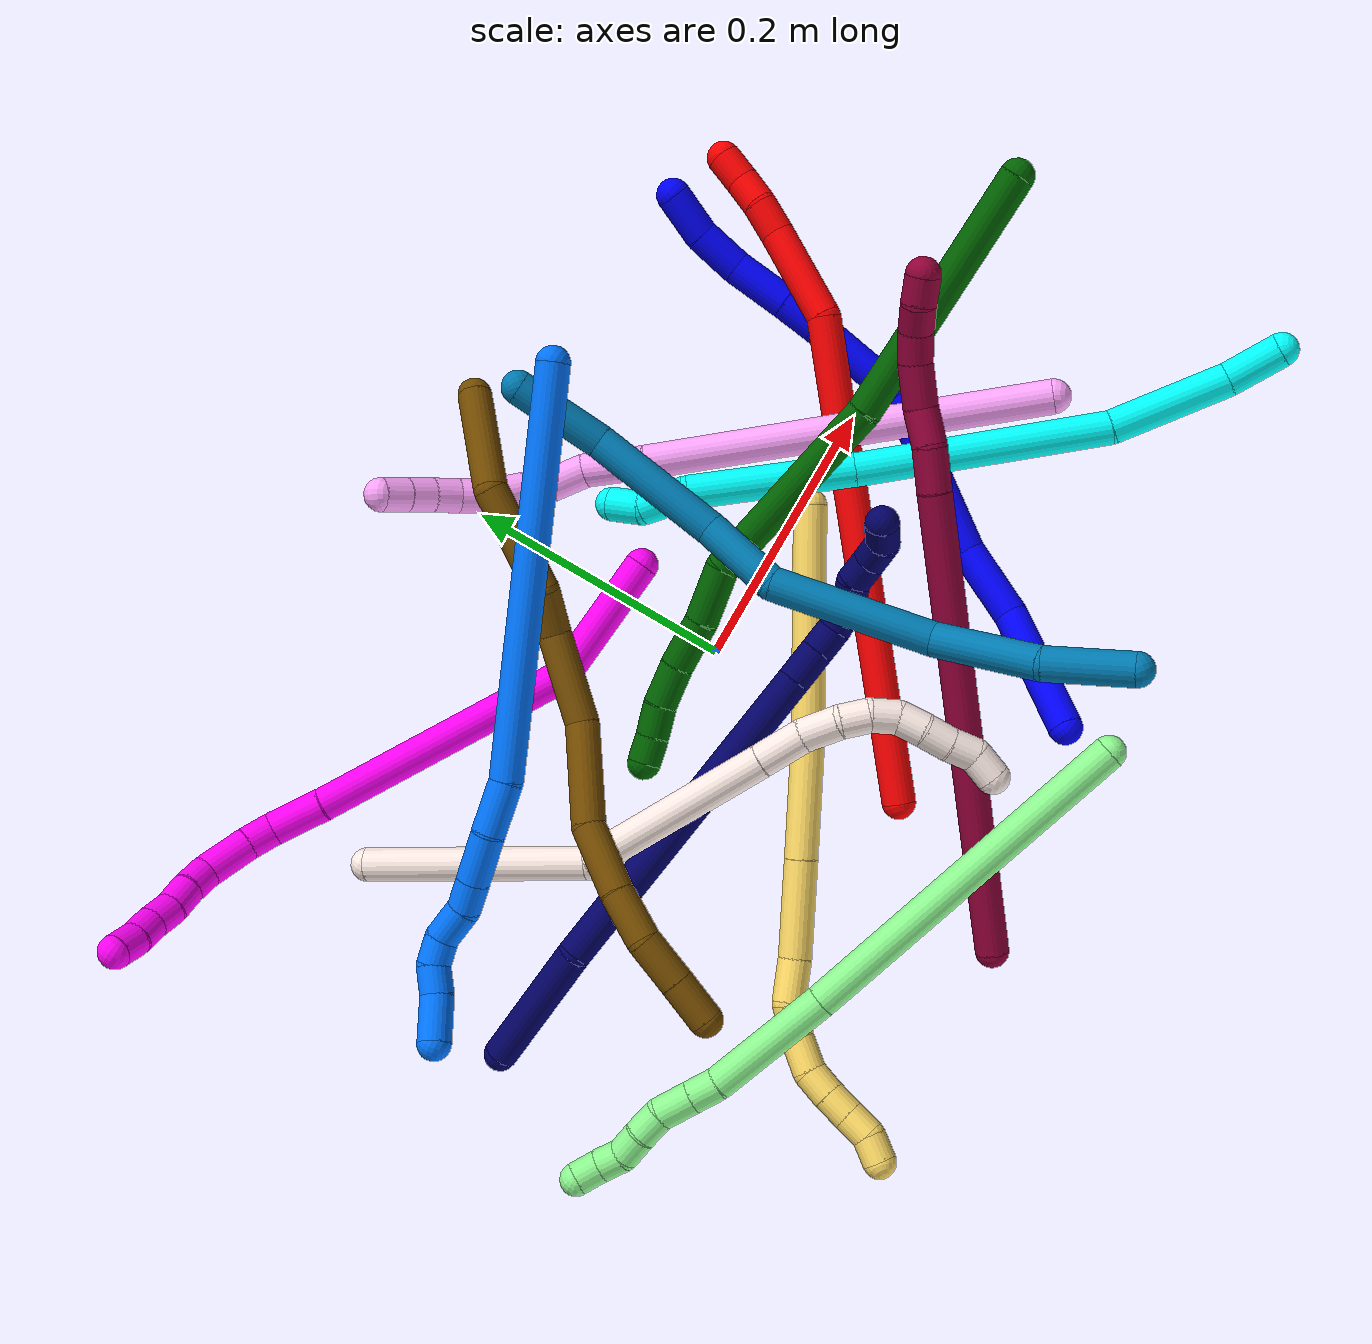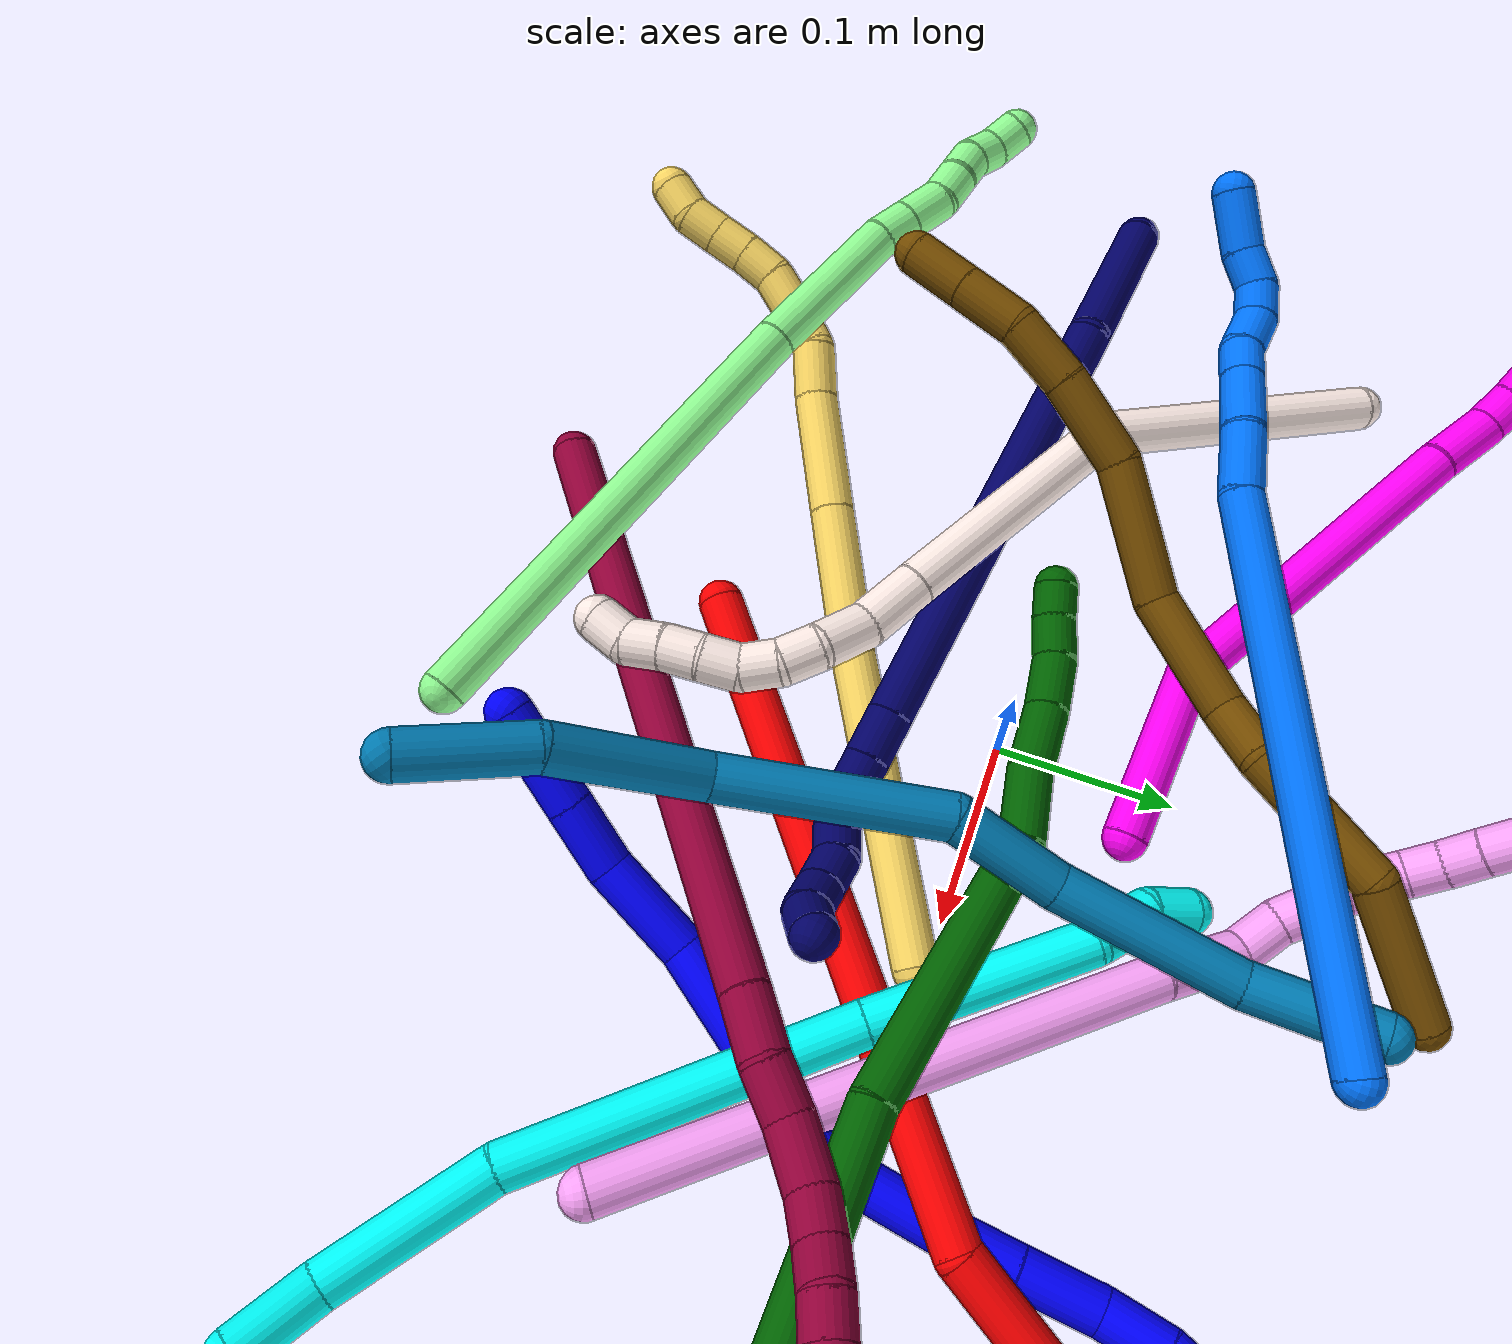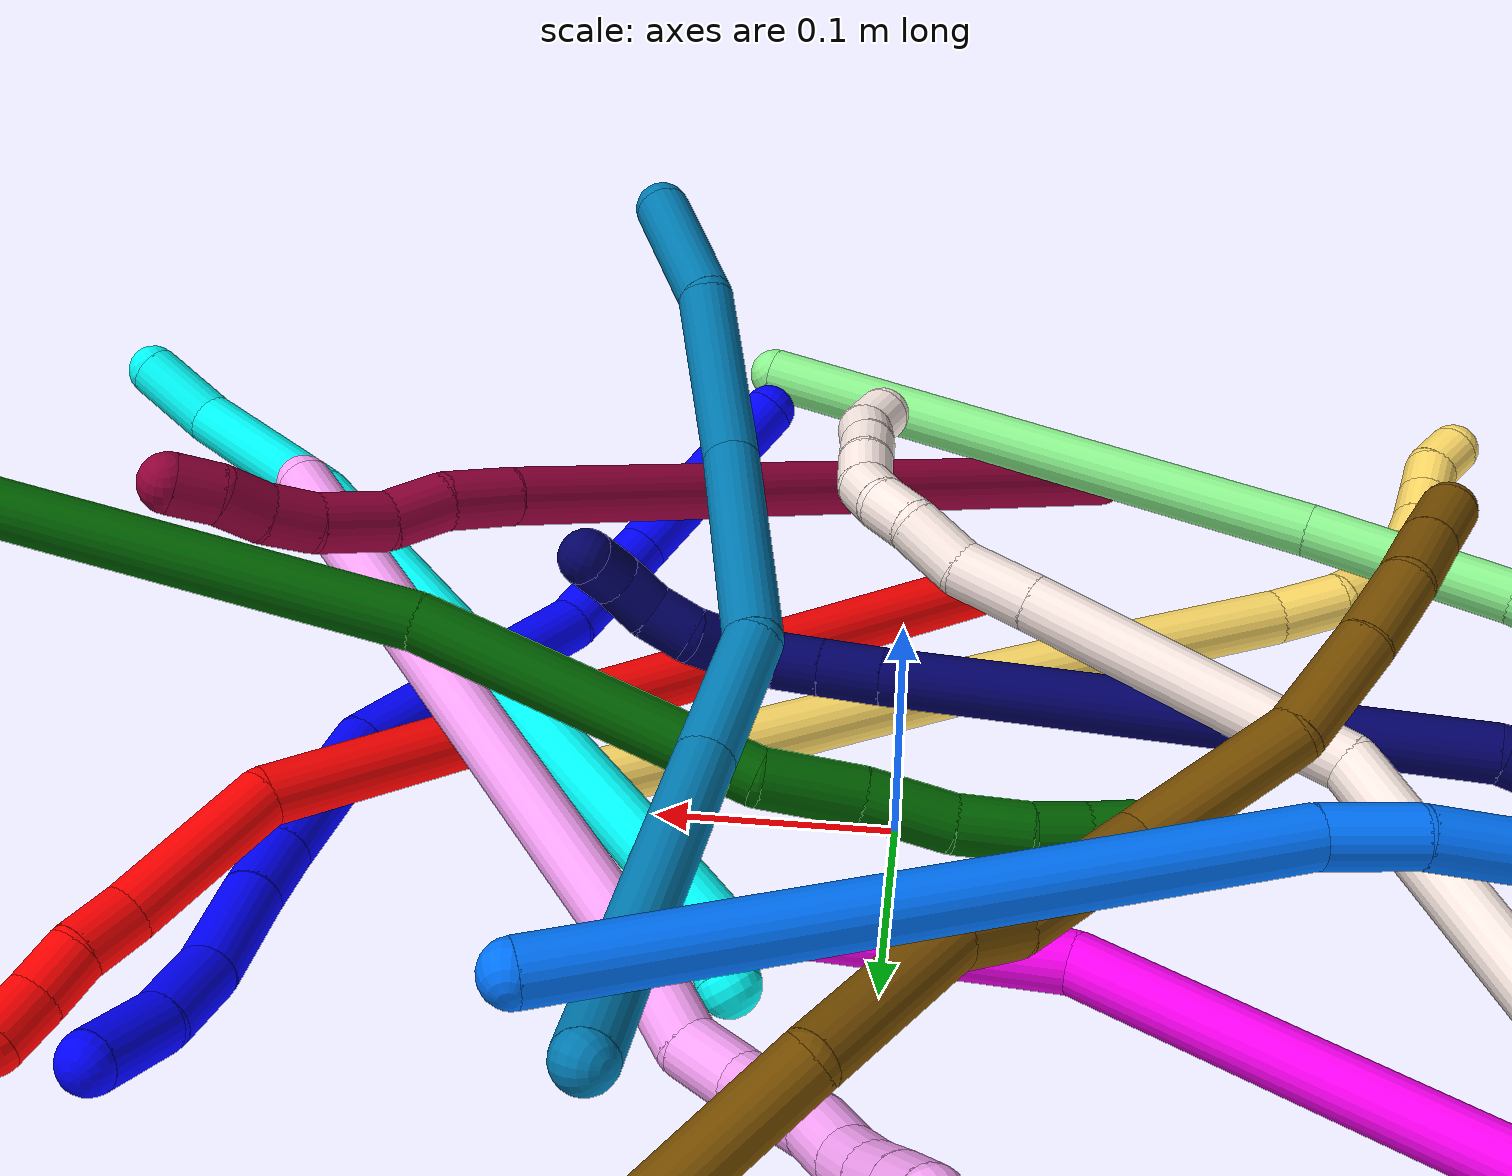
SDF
<sdf version="1.7">
 <world name="default">
  <plugin name="TubeGeneratorPlugin" filename="libtube_generator_plugin.so"/>
  <model name="photoneo_s_sensor">
   <static>1</static>
   <pose>0 0 2 1.57079 1.57079 3.14159</pose>
   <link name="link">
    <inertial><mass>0.1</mass></inertial>
    <sensor name="sensor" type="depth">
     <update_rate>30</update_rate>
     <camera>
      <horizontal_fov>1.22</horizontal_fov>
      <image><width>1920</width><height>1200</height><format>B8G8R8</format></image>
      <clip><near>0.1</near><far>4</far></clip>
      <depth_camera><output>points</output></depth_camera>
     </camera>
     <plugin name="camera_plugin" filename="libgazebo_ros_depth_camera.so">
      <baseline>0.2</baseline>
      <alwaysOn>1</alwaysOn>
      <updateRate>0.0</updateRate>
      <cameraName>camera_ir</cameraName>
      <imageTopicName>/camera/color/image_raw</imageTopicName>
      <cameraInfoTopicName>/camera/color/camera_info</cameraInfoTopicName>
      <depthImageTopicName>/camera/depth/image_raw</depthImageTopicName>
      <depthImageCameraInfoTopicName>/camera/depth/camera_info</depthImageCameraInfoTopicName>
      <pointCloudTopicName>/camera/depth/points</pointCloudTopicName>
      <frameName>fr_optical</frameName>
      <pointCloudCutoff>0.1</pointCloudCutoff>
      <pointCloudCutoffMax>2.0</pointCloudCutoffMax>
      <distortionK1>0</distortionK1>
      <distortionK2>0</distortionK2>
      <distortionK3>0</distortionK3>
      <distortionT1>0</distortionT1>
      <distortionT2>0</distortionT2>
      <CxPrime>0</CxPrime>
      <Cx>0</Cx>
      <Cy>0</Cy>
      <focalLength>0</focalLength>
      <hackBaseline>0</hackBaseline>
     </plugin>
    </sensor>
   </link>
  </model>
  <gravity>0 0 -9.8</gravity>
  <magnetic_field>6e-06 2.3e-05 -4.2e-05</magnetic_field>
  <atmosphere type="adiabatic"/>
  <physics name="default_physics" default="0" type="ode">
   <max_step_size>0.003</max_step_size>
   <real_time_factor>1</real_time_factor>
   <real_time_update_rate>1000</real_time_update_rate>
   <max_contacts>10000</max_contacts>
   <ode>
    <solver>
     <type>quick</type>
     <iters>100</iters>
     <sor>1.3</sor>
     <use_dynamic_moi_rescaling>0</use_dynamic_moi_rescaling>
    </solver>
    <constraints>
     <contact_max_correcting_vel>0</contact_max_correcting_vel>
     <contact_surface_layer>0.001</contact_surface_layer>
     <cfm>0</cfm>
     <erp>0.2</erp>
    </constraints>
   </ode>
  </physics>
  <scene><ambient>0.4 0.4 0.4 1</ambient><background>0.7 0.7 0.7 1</background><shadows>0</shadows></scene>
  <audio><device>default</device></audio>
  <spherical_coordinates>
   <surface_model>EARTH_WGS84</surface_model>
   <latitude_deg>0</latitude_deg>
   <longitude_deg>0</longitude_deg>
   <elevation>0</elevation>
   <heading_deg>0</heading_deg>
  </spherical_coordinates>
  <model name="bin">
   <static>1</static>
   <link name="bottom">
    <collision name="collision-bottom">
     <pose>0 0 -0.01 0 -0 0</pose>
     <geometry><box><size>0.8 0.6 0.02</size></box></geometry>
     <surface>
      <friction><ode><mu>100</mu><mu2>100</mu2></ode></friction>
      <contact><collide_bitmask>65535</collide_bitmask></contact>
     </surface>
    </collision>
   </link>
   <link name="west_wall">
    <collision name="collision-west_wall">
     <pose>-0.41 0 0.1 0 -0 0</pose>
     <geometry><box><size>0.02 0.6 0.2</size></box></geometry>
     <surface>
      <friction><ode><mu>100</mu><mu2>100</mu2></ode></friction>
      <contact><collide_bitmask>65535</collide_bitmask></contact>
     </surface>
    </collision>
   </link>
   <link name="east_wall">
    <collision name="collision-east_wall">
     <pose>0.41 0 0.1 0 -0 0</pose>
     <geometry><box><size>0.02 0.6 0.2</size></box></geometry>
     <surface>
      <friction><ode><mu>100</mu><mu2>100</mu2></ode></friction>
      <contact><collide_bitmask>65535</collide_bitmask></contact>
     </surface>
    </collision>
   </link>
   <link name="south_wall">
    <collision name="collision-south_wall">
     <pose>0 -0.31 0.1 0 -0 0</pose>
     <geometry><box><size>0.8 0.02 0.2</size></box></geometry>
     <surface>
      <friction><ode><mu>100</mu><mu2>100</mu2></ode></friction>
      <contact><collide_bitmask>65535</collide_bitmask></contact>
     </surface>
    </collision>
   </link>
   <link name="north_wall">
    <collision name="collision-north_wall">
     <pose>0 0.31 0.1 0 -0 0</pose>
     <geometry><box><size>0.8 0.02 0.2</size></box></geometry>
     <surface>
      <friction><ode><mu>100</mu><mu2>100</mu2></ode></friction>
      <contact><collide_bitmask>65535</collide_bitmask></contact>
     </surface>
    </collision>
   </link>
  </model>
  <model name="1">
   <static>0</static>
   <link name="1">
    <collision name="collision-cylinder-e_1_1_4">
     <pose>0.015704 0.009625 0.021722 -0.417123 0.584045 -0.127073</pose>
     <geometry><cylinder><radius>0.0125</radius><length>0.056959</length></cylinder></geometry>
     <surface>
      <friction><ode><mu>1.16</mu><mu2>1.16</mu2><slip1>0</slip1><slip2>0</slip2></ode></friction>
      <contact><ode><kp>1e+06</kp><kd>1</kd><max_vel>0</max_vel><min_depth>0.001</min_depth></ode></contact>
     </surface>
    </collision>
    <visual name="visual-cylinder-e_1_1_4">
     <pose>0.015704 0.009625 0.021722 -0.417123 0.584045 -0.127073</pose>
     <geometry><cylinder><radius>0.0125</radius><length>0.056959</length></cylinder></geometry>
     <material><ambient>0 0 1 1</ambient></material>
    </visual>
    <collision name="collision-cylinder-e_2_4_5">
     <pose>0.042186 0.025967 0.05838 -0.422554 0.582062 -0.128311</pose>
     <geometry><cylinder><radius>0.0125</radius><length>0.039211</length></cylinder></geometry>
     <surface>
      <friction><ode><mu>1.16</mu><mu2>1.16</mu2><slip1>0</slip1><slip2>0</slip2></ode></friction>
      <contact><ode><kp>1e+06</kp><kd>1</kd><max_vel>0</max_vel><min_depth>0.001</min_depth></ode></contact>
     </surface>
    </collision>
    <visual name="visual-cylinder-e_2_4_5">
     <pose>0.042186 0.025967 0.05838 -0.422554 0.582062 -0.128311</pose>
     <geometry><cylinder><radius>0.0125</radius><length>0.039211</length></cylinder></geometry>
     <material><ambient>0 0 1 1</ambient></material>
    </visual>
    <collision name="collision-cylinder-e_3_5_6">
     <pose>0.063417 0.039149 0.09917 -0.245057 0.373808 -0.046568</pose>
     <geometry><cylinder><radius>0.0125</radius><length>0.057253</length></cylinder></geometry>
     <surface>
      <friction><ode><mu>1.16</mu><mu2>1.16</mu2><slip1>0</slip1><slip2>0</slip2></ode></friction>
      <contact><ode><kp>1e+06</kp><kd>1</kd><max_vel>0</max_vel><min_depth>0.001</min_depth></ode></contact>
     </surface>
    </collision>
    <visual name="visual-cylinder-e_3_5_6">
     <pose>0.063417 0.039149 0.09917 -0.245057 0.373808 -0.046568</pose>
     <geometry><cylinder><radius>0.0125</radius><length>0.057253</length></cylinder></geometry>
     <material><ambient>0 0 1 1</ambient></material>
    </visual>
    <collision name="collision-cylinder-e_4_6_7">
     <pose>0.100099 0.043506 0.181559 0.037279 0.434113 0.008222</pose>
     <geometry><cylinder><radius>0.0125</radius><length>0.124719</length></cylinder></geometry>
     <surface>
      <friction><ode><mu>1.16</mu><mu2>1.16</mu2><slip1>0</slip1><slip2>0</slip2></ode></friction>
      <contact><ode><kp>1e+06</kp><kd>1</kd><max_vel>0</max_vel><min_depth>0.001</min_depth></ode></contact>
     </surface>
    </collision>
    <visual name="visual-cylinder-e_4_6_7">
     <pose>0.100099 0.043506 0.181559 0.037279 0.434113 0.008222</pose>
     <geometry><cylinder><radius>0.0125</radius><length>0.124719</length></cylinder></geometry>
     <material><ambient>0 0 1 1</ambient></material>
    </visual>
    <collision name="collision-cylinder-e_5_7_8">
     <pose>0.126458 0.046406 0.277343 -0.126934 0.003301 -0.00021</pose>
     <geometry><cylinder><radius>0.0125</radius><length>0.079133</length></cylinder></geometry>
     <surface>
      <friction><ode><mu>1.16</mu><mu2>1.16</mu2><slip1>0</slip1><slip2>0</slip2></ode></friction>
      <contact><ode><kp>1e+06</kp><kd>1</kd><max_vel>0</max_vel><min_depth>0.001</min_depth></ode></contact>
     </surface>
    </collision>
    <visual name="visual-cylinder-e_5_7_8">
     <pose>0.126458 0.046406 0.277343 -0.126934 0.003301 -0.00021</pose>
     <geometry><cylinder><radius>0.0125</radius><length>0.079133</length></cylinder></geometry>
     <material><ambient>0 0 1 1</ambient></material>
    </visual>
    <collision name="collision-cylinder-e_6_8_9">
     <pose>0.125971 0.053358 0.330858 -0.135357 -0.042856 0.002905</pose>
     <geometry><cylinder><radius>0.0125</radius><length>0.028823</length></cylinder></geometry>
     <surface>
      <friction><ode><mu>1.16</mu><mu2>1.16</mu2><slip1>0</slip1><slip2>0</slip2></ode></friction>
      <contact><ode><kp>1e+06</kp><kd>1</kd><max_vel>0</max_vel><min_depth>0.001</min_depth></ode></contact>
     </surface>
    </collision>
    <visual name="visual-cylinder-e_6_8_9">
     <pose>0.125971 0.053358 0.330858 -0.135357 -0.042856 0.002905</pose>
     <geometry><cylinder><radius>0.0125</radius><length>0.028823</length></cylinder></geometry>
     <material><ambient>0 0 1 1</ambient></material>
    </visual>
    <collision name="collision-cylinder-e_7_9_10">
     <pose>0.124458 0.059384 0.366718 -0.186907 -0.040745 0.003819</pose>
     <geometry><cylinder><radius>0.0125</radius><length>0.04399</length></cylinder></geometry>
     <surface>
      <friction><ode><mu>1.16</mu><mu2>1.16</mu2><slip1>0</slip1><slip2>0</slip2></ode></friction>
      <contact><ode><kp>1e+06</kp><kd>1</kd><max_vel>0</max_vel><min_depth>0.001</min_depth></ode></contact>
     </surface>
    </collision>
    <visual name="visual-cylinder-e_7_9_10">
     <pose>0.124458 0.059384 0.366718 -0.186907 -0.040745 0.003819</pose>
     <geometry><cylinder><radius>0.0125</radius><length>0.04399</length></cylinder></geometry>
     <material><ambient>0 0 1 1</ambient></material>
    </visual>
    <collision name="collision-cylinder-e_8_10_11">
     <pose>0.123182 0.063318 0.405667 0.008663 -0.021902 -9.5e-05</pose>
     <geometry><cylinder><radius>0.0125</radius><length>0.03472</length></cylinder></geometry>
     <surface>
      <friction><ode><mu>1.16</mu><mu2>1.16</mu2><slip1>0</slip1><slip2>0</slip2></ode></friction>
      <contact><ode><kp>1e+06</kp><kd>1</kd><max_vel>0</max_vel><min_depth>0.001</min_depth></ode></contact>
     </surface>
    </collision>
    <visual name="visual-cylinder-e_8_10_11">
     <pose>0.123182 0.063318 0.405667 0.008663 -0.021902 -9.5e-05</pose>
     <geometry><cylinder><radius>0.0125</radius><length>0.03472</length></cylinder></geometry>
     <material><ambient>0 0 1 1</ambient></material>
    </visual>
    <collision name="collision-cylinder-e_9_11_2">
     <pose>0.125063 0.059958 0.440175 0.184983 0.128869 0.01197</pose>
     <geometry><cylinder><radius>0.0125</radius><length>0.035193</length></cylinder></geometry>
     <surface>
      <friction><ode><mu>1.16</mu><mu2>1.16</mu2><slip1>0</slip1><slip2>0</slip2></ode></friction>
      <contact><ode><kp>1e+06</kp><kd>1</kd><max_vel>0</max_vel><min_depth>0.001</min_depth></ode></contact>
     </surface>
    </collision>
    <visual name="visual-cylinder-e_9_11_2">
     <pose>0.125063 0.059958 0.440175 0.184983 0.128869 0.01197</pose>
     <geometry><cylinder><radius>0.0125</radius><length>0.035193</length></cylinder></geometry>
     <material><ambient>0 0 1 1</ambient></material>
    </visual>
    <collision name="collision-sphere-2">
     <pose>0.127324 0.056748 0.457327 0 -0 0</pose>
     <geometry><sphere><radius>0.0125</radius></sphere></geometry>
     <surface>
      <friction><ode><mu>1.16</mu><mu2>1.16</mu2><slip1>0</slip1><slip2>0</slip2></ode></friction>
      <contact><ode><kp>1e+06</kp><kd>1</kd><max_vel>0</max_vel><min_depth>0.001</min_depth></ode></contact>
     </surface>
    </collision>
    <visual name="visual-sphere-2">
     <pose>0.127324 0.056748 0.457327 0 -0 0</pose>
     <geometry><sphere><radius>0.0125</radius></sphere></geometry>
     <material><ambient>0 0 1 1</ambient></material>
    </visual>
    <collision name="collision-sphere-11">
     <pose>0.122802 0.063167 0.423022 0 -0 0</pose>
     <geometry><sphere><radius>0.0125</radius></sphere></geometry>
     <surface>
      <friction><ode><mu>1.16</mu><mu2>1.16</mu2><slip1>0</slip1><slip2>0</slip2></ode></friction>
      <contact><ode><kp>1e+06</kp><kd>1</kd><max_vel>0</max_vel><min_depth>0.001</min_depth></ode></contact>
     </surface>
    </collision>
    <visual name="visual-sphere-11">
     <pose>0.122802 0.063167 0.423022 0 -0 0</pose>
     <geometry><sphere><radius>0.0125</radius></sphere></geometry>
     <material><ambient>0 0 1 1</ambient></material>
    </visual>
    <collision name="collision-sphere-10">
     <pose>0.123562 0.063468 0.388312 0 -0 0</pose>
     <geometry><sphere><radius>0.0125</radius></sphere></geometry>
     <surface>
      <friction><ode><mu>1.16</mu><mu2>1.16</mu2><slip1>0</slip1><slip2>0</slip2></ode></friction>
      <contact><ode><kp>1e+06</kp><kd>1</kd><max_vel>0</max_vel><min_depth>0.001</min_depth></ode></contact>
     </surface>
    </collision>
    <visual name="visual-sphere-10">
     <pose>0.123562 0.063468 0.388312 0 -0 0</pose>
     <geometry><sphere><radius>0.0125</radius></sphere></geometry>
     <material><ambient>0 0 1 1</ambient></material>
    </visual>
    <collision name="collision-sphere-9">
     <pose>0.125354 0.055301 0.345124 0 -0 0</pose>
     <geometry><sphere><radius>0.0125</radius></sphere></geometry>
     <surface>
      <friction><ode><mu>1.16</mu><mu2>1.16</mu2><slip1>0</slip1><slip2>0</slip2></ode></friction>
      <contact><ode><kp>1e+06</kp><kd>1</kd><max_vel>0</max_vel><min_depth>0.001</min_depth></ode></contact>
     </surface>
    </collision>
    <visual name="visual-sphere-9">
     <pose>0.125354 0.055301 0.345124 0 -0 0</pose>
     <geometry><sphere><radius>0.0125</radius></sphere></geometry>
     <material><ambient>0 0 1 1</ambient></material>
    </visual>
    <collision name="collision-sphere-4">
     <pose>0.031407 0.019251 0.043443 0 -0 0</pose>
     <geometry><sphere><radius>0.0125</radius></sphere></geometry>
     <surface>
      <friction><ode><mu>1.16</mu><mu2>1.16</mu2><slip1>0</slip1><slip2>0</slip2></ode></friction>
      <contact><ode><kp>1e+06</kp><kd>1</kd><max_vel>0</max_vel><min_depth>0.001</min_depth></ode></contact>
     </surface>
    </collision>
    <visual name="visual-sphere-4">
     <pose>0.031407 0.019251 0.043443 0 -0 0</pose>
     <geometry><sphere><radius>0.0125</radius></sphere></geometry>
     <material><ambient>0 0 1 1</ambient></material>
    </visual>
    <collision name="collision-sphere-1">
     <geometry><sphere><radius>0.0125</radius></sphere></geometry>
     <surface>
      <friction><ode><mu>1.16</mu><mu2>1.16</mu2><slip1>0</slip1><slip2>0</slip2></ode></friction>
      <contact><ode><kp>1e+06</kp><kd>1</kd><max_vel>0</max_vel><min_depth>0.001</min_depth></ode></contact>
     </surface>
    </collision>
    <visual name="visual-sphere-1">
     <geometry><sphere><radius>0.0125</radius></sphere></geometry>
     <material><ambient>0 0 1 1</ambient></material>
    </visual>
    <collision name="collision-sphere-8">
     <pose>0.126589 0.051415 0.316591 0 -0 0</pose>
     <geometry><sphere><radius>0.0125</radius></sphere></geometry>
     <surface>
      <friction><ode><mu>1.16</mu><mu2>1.16</mu2><slip1>0</slip1><slip2>0</slip2></ode></friction>
      <contact><ode><kp>1e+06</kp><kd>1</kd><max_vel>0</max_vel><min_depth>0.001</min_depth></ode></contact>
     </surface>
    </collision>
    <visual name="visual-sphere-8">
     <pose>0.126589 0.051415 0.316591 0 -0 0</pose>
     <geometry><sphere><radius>0.0125</radius></sphere></geometry>
     <material><ambient>0 0 1 1</ambient></material>
    </visual>
    <collision name="collision-sphere-5">
     <pose>0.052964 0.032683 0.073317 0 -0 0</pose>
     <geometry><sphere><radius>0.0125</radius></sphere></geometry>
     <surface>
      <friction><ode><mu>1.16</mu><mu2>1.16</mu2><slip1>0</slip1><slip2>0</slip2></ode></friction>
      <contact><ode><kp>1e+06</kp><kd>1</kd><max_vel>0</max_vel><min_depth>0.001</min_depth></ode></contact>
     </surface>
    </collision>
    <visual name="visual-sphere-5">
     <pose>0.052964 0.032683 0.073317 0 -0 0</pose>
     <geometry><sphere><radius>0.0125</radius></sphere></geometry>
     <material><ambient>0 0 1 1</ambient></material>
    </visual>
    <collision name="collision-sphere-6">
     <pose>0.07387 0.045614 0.125024 0 -0 0</pose>
     <geometry><sphere><radius>0.0125</radius></sphere></geometry>
     <surface>
      <friction><ode><mu>1.16</mu><mu2>1.16</mu2><slip1>0</slip1><slip2>0</slip2></ode></friction>
      <contact><ode><kp>1e+06</kp><kd>1</kd><max_vel>0</max_vel><min_depth>0.001</min_depth></ode></contact>
     </surface>
    </collision>
    <visual name="visual-sphere-6">
     <pose>0.07387 0.045614 0.125024 0 -0 0</pose>
     <geometry><sphere><radius>0.0125</radius></sphere></geometry>
     <material><ambient>0 0 1 1</ambient></material>
    </visual>
    <collision name="collision-sphere-7">
     <pose>0.126328 0.041397 0.238095 0 -0 0</pose>
     <geometry><sphere><radius>0.0125</radius></sphere></geometry>
     <surface>
      <friction><ode><mu>1.16</mu><mu2>1.16</mu2><slip1>0</slip1><slip2>0</slip2></ode></friction>
      <contact><ode><kp>1e+06</kp><kd>1</kd><max_vel>0</max_vel><min_depth>0.001</min_depth></ode></contact>
     </surface>
    </collision>
    <visual name="visual-sphere-7">
     <pose>0.126328 0.041397 0.238095 0 -0 0</pose>
     <geometry><sphere><radius>0.0125</radius></sphere></geometry>
     <material><ambient>0 0 1 1</ambient></material>
    </visual>
    <inertial>
     <pose>0.092909 0.042729 0.218077 0 -0 0</pose>
     <mass>0.5</mass>
     <inertia>
      <ixx>0.000262</ixx>
      <ixy>0</ixy>
      <ixz>0</ixz>
      <iyy>0.000274</iyy>
      <iyz>0</iyz>
      <izz>-6.8e-05</izz>
     </inertia>
    </inertial>
   </link>
   <pose>0.07838 -0.24171 0.064609 -1.43208 0.371484 -0.157979</pose>
  </model>
  <model name="2">
   <static>0</static>
   <link name="2">
    <collision name="collision-cylinder-e_1_1_4">
     <pose>0.040312 0.00847 0.173857 -0.048679 0.227583 -0.005564</pose>
     <geometry><cylinder><radius>0.0125</radius><length>0.35734</length></cylinder></geometry>
     <surface>
      <friction><ode><mu>1.16</mu><mu2>1.16</mu2><slip1>0</slip1><slip2>0</slip2></ode></friction>
      <contact><ode><kp>1e+06</kp><kd>1</kd><max_vel>0</max_vel><min_depth>0.001</min_depth></ode></contact>
     </surface>
    </collision>
    <visual name="visual-cylinder-e_1_1_4">
     <pose>0.040312 0.00847 0.173857 -0.048679 0.227583 -0.005564</pose>
     <geometry><cylinder><radius>0.0125</radius><length>0.35734</length></cylinder></geometry>
     <material><ambient>1 0 0 1</ambient></material>
    </visual>
    <collision name="collision-cylinder-e_2_4_5">
     <pose>0.077182 0.00923 0.382537 0.21789 -0.096227 -0.010533</pose>
     <geometry><cylinder><radius>0.0125</radius><length>0.071664</length></cylinder></geometry>
     <surface>
      <friction><ode><mu>1.16</mu><mu2>1.16</mu2><slip1>0</slip1><slip2>0</slip2></ode></friction>
      <contact><ode><kp>1e+06</kp><kd>1</kd><max_vel>0</max_vel><min_depth>0.001</min_depth></ode></contact>
     </surface>
    </collision>
    <visual name="visual-cylinder-e_2_4_5">
     <pose>0.077182 0.00923 0.382537 0.21789 -0.096227 -0.010533</pose>
     <geometry><cylinder><radius>0.0125</radius><length>0.071664</length></cylinder></geometry>
     <material><ambient>1 0 0 1</ambient></material>
    </visual>
    <collision name="collision-cylinder-e_3_5_6">
     <pose>0.074032 -0.002139 0.429555 0.29149 0.022977 0.003373</pose>
     <geometry><cylinder><radius>0.0125</radius><length>0.025471</length></cylinder></geometry>
     <surface>
      <friction><ode><mu>1.16</mu><mu2>1.16</mu2><slip1>0</slip1><slip2>0</slip2></ode></friction>
      <contact><ode><kp>1e+06</kp><kd>1</kd><max_vel>0</max_vel><min_depth>0.001</min_depth></ode></contact>
     </surface>
    </collision>
    <visual name="visual-cylinder-e_3_5_6">
     <pose>0.074032 -0.002139 0.429555 0.29149 0.022977 0.003373</pose>
     <geometry><cylinder><radius>0.0125</radius><length>0.025471</length></cylinder></geometry>
     <material><ambient>1 0 0 1</ambient></material>
    </visual>
    <collision name="collision-cylinder-e_4_6_7">
     <pose>0.072033 -0.009091 0.45229 0.302794 -0.204615 -0.031324</pose>
     <geometry><cylinder><radius>0.0125</radius><length>0.022555</length></cylinder></geometry>
     <surface>
      <friction><ode><mu>1.16</mu><mu2>1.16</mu2><slip1>0</slip1><slip2>0</slip2></ode></friction>
      <contact><ode><kp>1e+06</kp><kd>1</kd><max_vel>0</max_vel><min_depth>0.001</min_depth></ode></contact>
     </surface>
    </collision>
    <visual name="visual-cylinder-e_4_6_7">
     <pose>0.072033 -0.009091 0.45229 0.302794 -0.204615 -0.031324</pose>
     <geometry><cylinder><radius>0.0125</radius><length>0.022555</length></cylinder></geometry>
     <material><ambient>1 0 0 1</ambient></material>
    </visual>
    <collision name="collision-cylinder-e_5_7_2">
     <pose>0.068642 -0.01664 0.47344 0.381529 -0.095888 -0.018531</pose>
     <geometry><cylinder><radius>0.0125</radius><length>0.02297</length></cylinder></geometry>
     <surface>
      <friction><ode><mu>1.16</mu><mu2>1.16</mu2><slip1>0</slip1><slip2>0</slip2></ode></friction>
      <contact><ode><kp>1e+06</kp><kd>1</kd><max_vel>0</max_vel><min_depth>0.001</min_depth></ode></contact>
     </surface>
    </collision>
    <visual name="visual-cylinder-e_5_7_2">
     <pose>0.068642 -0.01664 0.47344 0.381529 -0.095888 -0.018531</pose>
     <geometry><cylinder><radius>0.0125</radius><length>0.02297</length></cylinder></geometry>
     <material><ambient>1 0 0 1</ambient></material>
    </visual>
    <collision name="collision-sphere-2">
     <pose>0.067542 -0.020897 0.48405 0 -0 0</pose>
     <geometry><sphere><radius>0.0125</radius></sphere></geometry>
     <surface>
      <friction><ode><mu>1.16</mu><mu2>1.16</mu2><slip1>0</slip1><slip2>0</slip2></ode></friction>
      <contact><ode><kp>1e+06</kp><kd>1</kd><max_vel>0</max_vel><min_depth>0.001</min_depth></ode></contact>
     </surface>
    </collision>
    <visual name="visual-sphere-2">
     <pose>0.067542 -0.020897 0.48405 0 -0 0</pose>
     <geometry><sphere><radius>0.0125</radius></sphere></geometry>
     <material><ambient>1 0 0 1</ambient></material>
    </visual>
    <collision name="collision-sphere-7">
     <pose>0.069741 -0.012384 0.46283 0 -0 0</pose>
     <geometry><sphere><radius>0.0125</radius></sphere></geometry>
     <surface>
      <friction><ode><mu>1.16</mu><mu2>1.16</mu2><slip1>0</slip1><slip2>0</slip2></ode></friction>
      <contact><ode><kp>1e+06</kp><kd>1</kd><max_vel>0</max_vel><min_depth>0.001</min_depth></ode></contact>
     </surface>
    </collision>
    <visual name="visual-sphere-7">
     <pose>0.069741 -0.012384 0.46283 0 -0 0</pose>
     <geometry><sphere><radius>0.0125</radius></sphere></geometry>
     <material><ambient>1 0 0 1</ambient></material>
    </visual>
    <collision name="collision-sphere-6">
     <pose>0.074324 -0.005798 0.44175 0 -0 0</pose>
     <geometry><sphere><radius>0.0125</radius></sphere></geometry>
     <surface>
      <friction><ode><mu>1.16</mu><mu2>1.16</mu2><slip1>0</slip1><slip2>0</slip2></ode></friction>
      <contact><ode><kp>1e+06</kp><kd>1</kd><max_vel>0</max_vel><min_depth>0.001</min_depth></ode></contact>
     </surface>
    </collision>
    <visual name="visual-sphere-6">
     <pose>0.074324 -0.005798 0.44175 0 -0 0</pose>
     <geometry><sphere><radius>0.0125</radius></sphere></geometry>
     <material><ambient>1 0 0 1</ambient></material>
    </visual>
    <collision name="collision-sphere-5">
     <pose>0.073739 0.00152 0.41736 0 -0 0</pose>
     <geometry><sphere><radius>0.0125</radius></sphere></geometry>
     <surface>
      <friction><ode><mu>1.16</mu><mu2>1.16</mu2><slip1>0</slip1><slip2>0</slip2></ode></friction>
      <contact><ode><kp>1e+06</kp><kd>1</kd><max_vel>0</max_vel><min_depth>0.001</min_depth></ode></contact>
     </surface>
    </collision>
    <visual name="visual-sphere-5">
     <pose>0.073739 0.00152 0.41736 0 -0 0</pose>
     <geometry><sphere><radius>0.0125</radius></sphere></geometry>
     <material><ambient>1 0 0 1</ambient></material>
    </visual>
    <collision name="collision-sphere-1">
     <geometry><sphere><radius>0.0125</radius></sphere></geometry>
     <surface>
      <friction><ode><mu>1.16</mu><mu2>1.16</mu2><slip1>0</slip1><slip2>0</slip2></ode></friction>
      <contact><ode><kp>1e+06</kp><kd>1</kd><max_vel>0</max_vel><min_depth>0.001</min_depth></ode></contact>
     </surface>
    </collision>
    <visual name="visual-sphere-1">
     <geometry><sphere><radius>0.0125</radius></sphere></geometry>
     <material><ambient>1 0 0 1</ambient></material>
    </visual>
    <collision name="collision-sphere-4">
     <pose>0.080624 0.01694 0.347713 0 -0 0</pose>
     <geometry><sphere><radius>0.0125</radius></sphere></geometry>
     <surface>
      <friction><ode><mu>1.16</mu><mu2>1.16</mu2><slip1>0</slip1><slip2>0</slip2></ode></friction>
      <contact><ode><kp>1e+06</kp><kd>1</kd><max_vel>0</max_vel><min_depth>0.001</min_depth></ode></contact>
     </surface>
    </collision>
    <visual name="visual-sphere-4">
     <pose>0.080624 0.01694 0.347713 0 -0 0</pose>
     <geometry><sphere><radius>0.0125</radius></sphere></geometry>
     <material><ambient>1 0 0 1</ambient></material>
    </visual>
    <inertial>
     <pose>0.050047 0.006093 0.243115 0 -0 0</pose>
     <mass>0.5</mass>
     <inertia>
      <ixx>0.003741</ixx>
      <ixy>0</ixy>
      <ixz>0</ixz>
      <iyy>0.003828</iyy>
      <iyz>0</iyz>
      <izz>-0.000991</izz>
     </inertia>
    </inertial>
   </link>
   <pose>-0.027661 -0.171915 0.012482 -2.16983 -1.31589 -0.204113</pose>
  </model>
  <model name="3">
   <static>0</static>
   <link name="3">
    <collision name="collision-cylinder-e_1_1_4">
     <pose>-0.002329 0.008233 -0.01924 -2.73727 -0.110824 0.528593</pose>
     <geometry><cylinder><radius>0.0125</radius><length>0.042114</length></cylinder></geometry>
     <surface>
      <friction><ode><mu>1.16</mu><mu2>1.16</mu2><slip1>0</slip1><slip2>0</slip2></ode></friction>
      <contact><ode><kp>1e+06</kp><kd>1</kd><max_vel>0</max_vel><min_depth>0.001</min_depth></ode></contact>
     </surface>
    </collision>
    <visual name="visual-cylinder-e_1_1_4">
     <pose>-0.002329 0.008233 -0.01924 -2.73727 -0.110824 0.528593</pose>
     <geometry><cylinder><radius>0.0125</radius><length>0.042114</length></cylinder></geometry>
     <material><ambient>0.003922 1 0.996078 1</ambient></material>
    </visual>
    <collision name="collision-cylinder-e_2_4_5">
     <pose>-0.003233 0.044675 -0.073181 -2.45901 0.031835 -0.089576</pose>
     <geometry><cylinder><radius>0.0125</radius><length>0.089485</length></cylinder></geometry>
     <surface>
      <friction><ode><mu>1.16</mu><mu2>1.16</mu2><slip1>0</slip1><slip2>0</slip2></ode></friction>
      <contact><ode><kp>1e+06</kp><kd>1</kd><max_vel>0</max_vel><min_depth>0.001</min_depth></ode></contact>
     </surface>
    </collision>
    <visual name="visual-cylinder-e_2_4_5">
     <pose>-0.003233 0.044675 -0.073181 -2.45901 0.031835 -0.089576</pose>
     <geometry><cylinder><radius>0.0125</radius><length>0.089485</length></cylinder></geometry>
     <material><ambient>0.003922 1 0.996078 1</ambient></material>
    </visual>
    <collision name="collision-cylinder-e_3_5_6">
     <pose>0.021818 0.129888 -0.177047 -2.4523 0.257748 -0.692896</pose>
     <geometry><cylinder><radius>0.0125</radius><length>0.185381</length></cylinder></geometry>
     <surface>
      <friction><ode><mu>1.16</mu><mu2>1.16</mu2><slip1>0</slip1><slip2>0</slip2></ode></friction>
      <contact><ode><kp>1e+06</kp><kd>1</kd><max_vel>0</max_vel><min_depth>0.001</min_depth></ode></contact>
     </surface>
    </collision>
    <visual name="visual-cylinder-e_3_5_6">
     <pose>0.021818 0.129888 -0.177047 -2.4523 0.257748 -0.692896</pose>
     <geometry><cylinder><radius>0.0125</radius><length>0.185381</length></cylinder></geometry>
     <material><ambient>0.003922 1 0.996078 1</ambient></material>
    </visual>
    <collision name="collision-cylinder-e_4_6_7">
     <pose>0.062812 0.22493 -0.29041 -2.43093 0.289455 -0.748498</pose>
     <geometry><cylinder><radius>0.0125</radius><length>0.121686</length></cylinder></geometry>
     <surface>
      <friction><ode><mu>1.16</mu><mu2>1.16</mu2><slip1>0</slip1><slip2>0</slip2></ode></friction>
      <contact><ode><kp>1e+06</kp><kd>1</kd><max_vel>0</max_vel><min_depth>0.001</min_depth></ode></contact>
     </surface>
    </collision>
    <visual name="visual-cylinder-e_4_6_7">
     <pose>0.062812 0.22493 -0.29041 -2.43093 0.289455 -0.748498</pose>
     <geometry><cylinder><radius>0.0125</radius><length>0.121686</length></cylinder></geometry>
     <material><ambient>0.003922 1 0.996078 1</ambient></material>
    </visual>
    <collision name="collision-cylinder-e_5_7_8">
     <pose>0.081482 0.270249 -0.350954 -2.72263 0.072731 -0.338972</pose>
     <geometry><cylinder><radius>0.0125</radius><length>0.035887</length></cylinder></geometry>
     <surface>
      <friction><ode><mu>1.16</mu><mu2>1.16</mu2><slip1>0</slip1><slip2>0</slip2></ode></friction>
      <contact><ode><kp>1e+06</kp><kd>1</kd><max_vel>0</max_vel><min_depth>0.001</min_depth></ode></contact>
     </surface>
    </collision>
    <visual name="visual-cylinder-e_5_7_8">
     <pose>0.081482 0.270249 -0.350954 -2.72263 0.072731 -0.338972</pose>
     <geometry><cylinder><radius>0.0125</radius><length>0.035887</length></cylinder></geometry>
     <material><ambient>0.003922 1 0.996078 1</ambient></material>
    </visual>
    <collision name="collision-cylinder-e_6_8_2">
     <pose>0.088638 0.279946 -0.378339 -2.92603 0.477913 -2.30563</pose>
     <geometry><cylinder><radius>0.0125</radius><length>0.025447</length></cylinder></geometry>
     <surface>
      <friction><ode><mu>1.16</mu><mu2>1.16</mu2><slip1>0</slip1><slip2>0</slip2></ode></friction>
      <contact><ode><kp>1e+06</kp><kd>1</kd><max_vel>0</max_vel><min_depth>0.001</min_depth></ode></contact>
     </surface>
    </collision>
    <visual name="visual-cylinder-e_6_8_2">
     <pose>0.088638 0.279946 -0.378339 -2.92603 0.477913 -2.30563</pose>
     <geometry><cylinder><radius>0.0125</radius><length>0.025447</length></cylinder></geometry>
     <material><ambient>0.003922 1 0.996078 1</ambient></material>
    </visual>
    <collision name="collision-sphere-2">
     <pose>0.094489 0.282363 -0.389375 0 -0 0</pose>
     <geometry><sphere><radius>0.0125</radius></sphere></geometry>
     <surface>
      <friction><ode><mu>1.16</mu><mu2>1.16</mu2><slip1>0</slip1><slip2>0</slip2></ode></friction>
      <contact><ode><kp>1e+06</kp><kd>1</kd><max_vel>0</max_vel><min_depth>0.001</min_depth></ode></contact>
     </surface>
    </collision>
    <visual name="visual-sphere-2">
     <pose>0.094489 0.282363 -0.389375 0 -0 0</pose>
     <geometry><sphere><radius>0.0125</radius></sphere></geometry>
     <material><ambient>0.003922 1 0.996078 1</ambient></material>
    </visual>
    <collision name="collision-sphere-4">
     <pose>-0.004658 0.016466 -0.03848 0 -0 0</pose>
     <geometry><sphere><radius>0.0125</radius></sphere></geometry>
     <surface>
      <friction><ode><mu>1.16</mu><mu2>1.16</mu2><slip1>0</slip1><slip2>0</slip2></ode></friction>
      <contact><ode><kp>1e+06</kp><kd>1</kd><max_vel>0</max_vel><min_depth>0.001</min_depth></ode></contact>
     </surface>
    </collision>
    <visual name="visual-sphere-4">
     <pose>-0.004658 0.016466 -0.03848 0 -0 0</pose>
     <geometry><sphere><radius>0.0125</radius></sphere></geometry>
     <material><ambient>0.003922 1 0.996078 1</ambient></material>
    </visual>
    <collision name="collision-sphere-1">
     <geometry><sphere><radius>0.0125</radius></sphere></geometry>
     <surface>
      <friction><ode><mu>1.16</mu><mu2>1.16</mu2><slip1>0</slip1><slip2>0</slip2></ode></friction>
      <contact><ode><kp>1e+06</kp><kd>1</kd><max_vel>0</max_vel><min_depth>0.001</min_depth></ode></contact>
     </surface>
    </collision>
    <visual name="visual-sphere-1">
     <geometry><sphere><radius>0.0125</radius></sphere></geometry>
     <material><ambient>0.003922 1 0.996078 1</ambient></material>
    </visual>
    <collision name="collision-sphere-8">
     <pose>0.082786 0.27753 -0.367302 0 -0 0</pose>
     <geometry><sphere><radius>0.0125</radius></sphere></geometry>
     <surface>
      <friction><ode><mu>1.16</mu><mu2>1.16</mu2><slip1>0</slip1><slip2>0</slip2></ode></friction>
      <contact><ode><kp>1e+06</kp><kd>1</kd><max_vel>0</max_vel><min_depth>0.001</min_depth></ode></contact>
     </surface>
    </collision>
    <visual name="visual-sphere-8">
     <pose>0.082786 0.27753 -0.367302 0 -0 0</pose>
     <geometry><sphere><radius>0.0125</radius></sphere></geometry>
     <material><ambient>0.003922 1 0.996078 1</ambient></material>
    </visual>
    <collision name="collision-sphere-5">
     <pose>-0.001809 0.072885 -0.107881 0 -0 0</pose>
     <geometry><sphere><radius>0.0125</radius></sphere></geometry>
     <surface>
      <friction><ode><mu>1.16</mu><mu2>1.16</mu2><slip1>0</slip1><slip2>0</slip2></ode></friction>
      <contact><ode><kp>1e+06</kp><kd>1</kd><max_vel>0</max_vel><min_depth>0.001</min_depth></ode></contact>
     </surface>
    </collision>
    <visual name="visual-sphere-5">
     <pose>-0.001809 0.072885 -0.107881 0 -0 0</pose>
     <geometry><sphere><radius>0.0125</radius></sphere></geometry>
     <material><ambient>0.003922 1 0.996078 1</ambient></material>
    </visual>
    <collision name="collision-sphere-6">
     <pose>0.045445 0.186891 -0.246213 0 -0 0</pose>
     <geometry><sphere><radius>0.0125</radius></sphere></geometry>
     <surface>
      <friction><ode><mu>1.16</mu><mu2>1.16</mu2><slip1>0</slip1><slip2>0</slip2></ode></friction>
      <contact><ode><kp>1e+06</kp><kd>1</kd><max_vel>0</max_vel><min_depth>0.001</min_depth></ode></contact>
     </surface>
    </collision>
    <visual name="visual-sphere-6">
     <pose>0.045445 0.186891 -0.246213 0 -0 0</pose>
     <geometry><sphere><radius>0.0125</radius></sphere></geometry>
     <material><ambient>0.003922 1 0.996078 1</ambient></material>
    </visual>
    <collision name="collision-sphere-7">
     <pose>0.080178 0.262969 -0.334606 0 -0 0</pose>
     <geometry><sphere><radius>0.0125</radius></sphere></geometry>
     <surface>
      <friction><ode><mu>1.16</mu><mu2>1.16</mu2><slip1>0</slip1><slip2>0</slip2></ode></friction>
      <contact><ode><kp>1e+06</kp><kd>1</kd><max_vel>0</max_vel><min_depth>0.001</min_depth></ode></contact>
     </surface>
    </collision>
    <visual name="visual-sphere-7">
     <pose>0.080178 0.262969 -0.334606 0 -0 0</pose>
     <geometry><sphere><radius>0.0125</radius></sphere></geometry>
     <material><ambient>0.003922 1 0.996078 1</ambient></material>
    </visual>
    <inertial>
     <pose>0.03296 0.145232 -0.195482 0 -0 0</pose>
     <mass>0.5</mass>
     <inertia>
      <ixx>0.000151</ixx>
      <ixy>0</ixy>
      <ixz>0</ixz>
      <iyy>-0.000804</iyy>
      <iyz>0</iyz>
      <izz>-0.000688</izz>
     </inertia>
    </inertial>
   </link>
   <pose>0.385968 -0.237553 0.070669 0.810497 -0.098687 0.955283</pose>
  </model>
  <model name="4">
   <static>0</static>
   <link name="4">
    <collision name="collision-cylinder-e_1_1_4">
     <pose>-0.033258 0.004374 -0.143745 -3.11117 -0.227268 2.87656</pose>
     <geometry><cylinder><radius>0.0125</radius><length>0.295214</length></cylinder></geometry>
     <surface>
      <friction><ode><mu>1.16</mu><mu2>1.16</mu2><slip1>0</slip1><slip2>0</slip2></ode></friction>
      <contact><ode><kp>1e+06</kp><kd>1</kd><max_vel>0</max_vel><min_depth>0.001</min_depth></ode></contact>
     </surface>
    </collision>
    <visual name="visual-cylinder-e_1_1_4">
     <pose>-0.033258 0.004374 -0.143745 -3.11117 -0.227268 2.87656</pose>
     <geometry><cylinder><radius>0.0125</radius><length>0.295214</length></cylinder></geometry>
     <material><ambient>1 0.65098 0.996078 1</ambient></material>
    </visual>
    <collision name="collision-cylinder-e_2_4_5">
     <pose>-0.068365 0.007837 -0.311405 3.10347 -0.077063 -2.22316</pose>
     <geometry><cylinder><radius>0.0125</radius><length>0.048007</length></cylinder></geometry>
     <surface>
      <friction><ode><mu>1.16</mu><mu2>1.16</mu2><slip1>0</slip1><slip2>0</slip2></ode></friction>
      <contact><ode><kp>1e+06</kp><kd>1</kd><max_vel>0</max_vel><min_depth>0.001</min_depth></ode></contact>
     </surface>
    </collision>
    <visual name="visual-cylinder-e_2_4_5">
     <pose>-0.068365 0.007837 -0.311405 3.10347 -0.077063 -2.22316</pose>
     <geometry><cylinder><radius>0.0125</radius><length>0.048007</length></cylinder></geometry>
     <material><ambient>1 0.65098 0.996078 1</ambient></material>
    </visual>
    <collision name="collision-cylinder-e_3_5_6">
     <pose>-0.076921 0.005743 -0.347333 3.04356 -0.507234 -2.76749</pose>
     <geometry><cylinder><radius>0.0125</radius><length>0.027619</length></cylinder></geometry>
     <surface>
      <friction><ode><mu>1.16</mu><mu2>1.16</mu2><slip1>0</slip1><slip2>0</slip2></ode></friction>
      <contact><ode><kp>1e+06</kp><kd>1</kd><max_vel>0</max_vel><min_depth>0.001</min_depth></ode></contact>
     </surface>
    </collision>
    <visual name="visual-cylinder-e_3_5_6">
     <pose>-0.076921 0.005743 -0.347333 3.04356 -0.507234 -2.76749</pose>
     <geometry><cylinder><radius>0.0125</radius><length>0.027619</length></cylinder></geometry>
     <material><ambient>1 0.65098 0.996078 1</ambient></material>
    </visual>
    <collision name="collision-cylinder-e_4_6_7">
     <pose>-0.08979 0.007783 -0.366817 -2.73456 -0.648104 2.03971</pose>
     <geometry><cylinder><radius>0.0125</radius><length>0.020411</length></cylinder></geometry>
     <surface>
      <friction><ode><mu>1.16</mu><mu2>1.16</mu2><slip1>0</slip1><slip2>0</slip2></ode></friction>
      <contact><ode><kp>1e+06</kp><kd>1</kd><max_vel>0</max_vel><min_depth>0.001</min_depth></ode></contact>
     </surface>
    </collision>
    <visual name="visual-cylinder-e_4_6_7">
     <pose>-0.08979 0.007783 -0.366817 -2.73456 -0.648104 2.03971</pose>
     <geometry><cylinder><radius>0.0125</radius><length>0.020411</length></cylinder></geometry>
     <material><ambient>1 0.65098 0.996078 1</ambient></material>
    </visual>
    <collision name="collision-cylinder-e_5_7_8">
     <pose>-0.103178 0.013756 -0.383955 -2.86424 -0.623453 2.3241</pose>
     <geometry><cylinder><radius>0.0125</radius><length>0.024759</length></cylinder></geometry>
     <surface>
      <friction><ode><mu>1.16</mu><mu2>1.16</mu2><slip1>0</slip1><slip2>0</slip2></ode></friction>
      <contact><ode><kp>1e+06</kp><kd>1</kd><max_vel>0</max_vel><min_depth>0.001</min_depth></ode></contact>
     </surface>
    </collision>
    <visual name="visual-cylinder-e_5_7_8">
     <pose>-0.103178 0.013756 -0.383955 -2.86424 -0.623453 2.3241</pose>
     <geometry><cylinder><radius>0.0125</radius><length>0.024759</length></cylinder></geometry>
     <material><ambient>1 0.65098 0.996078 1</ambient></material>
    </visual>
    <collision name="collision-cylinder-e_6_8_9">
     <pose>-0.115894 0.021074 -0.40326 -2.69915 -0.475253 1.64484</pose>
     <geometry><cylinder><radius>0.0125</radius><length>0.023989</length></cylinder></geometry>
     <surface>
      <friction><ode><mu>1.16</mu><mu2>1.16</mu2><slip1>0</slip1><slip2>0</slip2></ode></friction>
      <contact><ode><kp>1e+06</kp><kd>1</kd><max_vel>0</max_vel><min_depth>0.001</min_depth></ode></contact>
     </surface>
    </collision>
    <visual name="visual-cylinder-e_6_8_9">
     <pose>-0.115894 0.021074 -0.40326 -2.69915 -0.475253 1.64484</pose>
     <geometry><cylinder><radius>0.0125</radius><length>0.023989</length></cylinder></geometry>
     <material><ambient>1 0.65098 0.996078 1</ambient></material>
    </visual>
    <collision name="collision-cylinder-e_7_9_10">
     <pose>-0.127054 0.030486 -0.419558 -2.51264 -0.602987 1.52587</pose>
     <geometry><cylinder><radius>0.0125</radius><length>0.02</length></cylinder></geometry>
     <surface>
      <friction><ode><mu>1.16</mu><mu2>1.16</mu2><slip1>0</slip1><slip2>0</slip2></ode></friction>
      <contact><ode><kp>1e+06</kp><kd>1</kd><max_vel>0</max_vel><min_depth>0.001</min_depth></ode></contact>
     </surface>
    </collision>
    <visual name="visual-cylinder-e_7_9_10">
     <pose>-0.127054 0.030486 -0.419558 -2.51264 -0.602987 1.52587</pose>
     <geometry><cylinder><radius>0.0125</radius><length>0.02</length></cylinder></geometry>
     <material><ambient>1 0.65098 0.996078 1</ambient></material>
    </visual>
    <collision name="collision-cylinder-e_8_10_11">
     <pose>-0.139139 0.040319 -0.432048 -2.43377 -0.69636 1.55304</pose>
     <geometry><cylinder><radius>0.0125</radius><length>0.02</length></cylinder></geometry>
     <surface>
      <friction><ode><mu>1.16</mu><mu2>1.16</mu2><slip1>0</slip1><slip2>0</slip2></ode></friction>
      <contact><ode><kp>1e+06</kp><kd>1</kd><max_vel>0</max_vel><min_depth>0.001</min_depth></ode></contact>
     </surface>
    </collision>
    <visual name="visual-cylinder-e_8_10_11">
     <pose>-0.139139 0.040319 -0.432048 -2.43377 -0.69636 1.55304</pose>
     <geometry><cylinder><radius>0.0125</radius><length>0.02</length></cylinder></geometry>
     <material><ambient>1 0.65098 0.996078 1</ambient></material>
    </visual>
    <collision name="collision-cylinder-e_9_11_2">
     <pose>-0.151739 0.050331 -0.443918 -2.44792 -0.66689 1.52822</pose>
     <geometry><cylinder><radius>0.0125</radius><length>0.02</length></cylinder></geometry>
     <surface>
      <friction><ode><mu>1.16</mu><mu2>1.16</mu2><slip1>0</slip1><slip2>0</slip2></ode></friction>
      <contact><ode><kp>1e+06</kp><kd>1</kd><max_vel>0</max_vel><min_depth>0.001</min_depth></ode></contact>
     </surface>
    </collision>
    <visual name="visual-cylinder-e_9_11_2">
     <pose>-0.151739 0.050331 -0.443918 -2.44792 -0.66689 1.52822</pose>
     <geometry><cylinder><radius>0.0125</radius><length>0.02</length></cylinder></geometry>
     <material><ambient>1 0.65098 0.996078 1</ambient></material>
    </visual>
    <collision name="collision-sphere-2">
     <pose>-0.157924 0.055355 -0.44996 0 -0 0</pose>
     <geometry><sphere><radius>0.0125</radius></sphere></geometry>
     <surface>
      <friction><ode><mu>1.16</mu><mu2>1.16</mu2><slip1>0</slip1><slip2>0</slip2></ode></friction>
      <contact><ode><kp>1e+06</kp><kd>1</kd><max_vel>0</max_vel><min_depth>0.001</min_depth></ode></contact>
     </surface>
    </collision>
    <visual name="visual-sphere-2">
     <pose>-0.157924 0.055355 -0.44996 0 -0 0</pose>
     <geometry><sphere><radius>0.0125</radius></sphere></geometry>
     <material><ambient>1 0.65098 0.996078 1</ambient></material>
    </visual>
    <collision name="collision-sphere-11">
     <pose>-0.145553 0.045307 -0.437877 0 -0 0</pose>
     <geometry><sphere><radius>0.0125</radius></sphere></geometry>
     <surface>
      <friction><ode><mu>1.16</mu><mu2>1.16</mu2><slip1>0</slip1><slip2>0</slip2></ode></friction>
      <contact><ode><kp>1e+06</kp><kd>1</kd><max_vel>0</max_vel><min_depth>0.001</min_depth></ode></contact>
     </surface>
    </collision>
    <visual name="visual-sphere-11">
     <pose>-0.145553 0.045307 -0.437877 0 -0 0</pose>
     <geometry><sphere><radius>0.0125</radius></sphere></geometry>
     <material><ambient>1 0.65098 0.996078 1</ambient></material>
    </visual>
    <collision name="collision-sphere-10">
     <pose>-0.132725 0.035331 -0.426219 0 -0 0</pose>
     <geometry><sphere><radius>0.0125</radius></sphere></geometry>
     <surface>
      <friction><ode><mu>1.16</mu><mu2>1.16</mu2><slip1>0</slip1><slip2>0</slip2></ode></friction>
      <contact><ode><kp>1e+06</kp><kd>1</kd><max_vel>0</max_vel><min_depth>0.001</min_depth></ode></contact>
     </surface>
    </collision>
    <visual name="visual-sphere-10">
     <pose>-0.132725 0.035331 -0.426219 0 -0 0</pose>
     <geometry><sphere><radius>0.0125</radius></sphere></geometry>
     <material><ambient>1 0.65098 0.996078 1</ambient></material>
    </visual>
    <collision name="collision-sphere-9">
     <pose>-0.121382 0.02564 -0.412898 0 -0 0</pose>
     <geometry><sphere><radius>0.0125</radius></sphere></geometry>
     <surface>
      <friction><ode><mu>1.16</mu><mu2>1.16</mu2><slip1>0</slip1><slip2>0</slip2></ode></friction>
      <contact><ode><kp>1e+06</kp><kd>1</kd><max_vel>0</max_vel><min_depth>0.001</min_depth></ode></contact>
     </surface>
    </collision>
    <visual name="visual-sphere-9">
     <pose>-0.121382 0.02564 -0.412898 0 -0 0</pose>
     <geometry><sphere><radius>0.0125</radius></sphere></geometry>
     <material><ambient>1 0.65098 0.996078 1</ambient></material>
    </visual>
    <collision name="collision-sphere-4">
     <pose>-0.066517 0.008749 -0.28749 0 -0 0</pose>
     <geometry><sphere><radius>0.0125</radius></sphere></geometry>
     <surface>
      <friction><ode><mu>1.16</mu><mu2>1.16</mu2><slip1>0</slip1><slip2>0</slip2></ode></friction>
      <contact><ode><kp>1e+06</kp><kd>1</kd><max_vel>0</max_vel><min_depth>0.001</min_depth></ode></contact>
     </surface>
    </collision>
    <visual name="visual-sphere-4">
     <pose>-0.066517 0.008749 -0.28749 0 -0 0</pose>
     <geometry><sphere><radius>0.0125</radius></sphere></geometry>
     <material><ambient>1 0.65098 0.996078 1</ambient></material>
    </visual>
    <collision name="collision-sphere-1">
     <geometry><sphere><radius>0.0125</radius></sphere></geometry>
     <surface>
      <friction><ode><mu>1.16</mu><mu2>1.16</mu2><slip1>0</slip1><slip2>0</slip2></ode></friction>
      <contact><ode><kp>1e+06</kp><kd>1</kd><max_vel>0</max_vel><min_depth>0.001</min_depth></ode></contact>
     </surface>
    </collision>
    <visual name="visual-sphere-1">
     <geometry><sphere><radius>0.0125</radius></sphere></geometry>
     <material><ambient>1 0.65098 0.996078 1</ambient></material>
    </visual>
    <collision name="collision-sphere-8">
     <pose>-0.110406 0.016508 -0.393622 0 -0 0</pose>
     <geometry><sphere><radius>0.0125</radius></sphere></geometry>
     <surface>
      <friction><ode><mu>1.16</mu><mu2>1.16</mu2><slip1>0</slip1><slip2>0</slip2></ode></friction>
      <contact><ode><kp>1e+06</kp><kd>1</kd><max_vel>0</max_vel><min_depth>0.001</min_depth></ode></contact>
     </surface>
    </collision>
    <visual name="visual-sphere-8">
     <pose>-0.110406 0.016508 -0.393622 0 -0 0</pose>
     <geometry><sphere><radius>0.0125</radius></sphere></geometry>
     <material><ambient>1 0.65098 0.996078 1</ambient></material>
    </visual>
    <collision name="collision-sphere-5">
     <pose>-0.070213 0.006925 -0.33532 0 -0 0</pose>
     <geometry><sphere><radius>0.0125</radius></sphere></geometry>
     <surface>
      <friction><ode><mu>1.16</mu><mu2>1.16</mu2><slip1>0</slip1><slip2>0</slip2></ode></friction>
      <contact><ode><kp>1e+06</kp><kd>1</kd><max_vel>0</max_vel><min_depth>0.001</min_depth></ode></contact>
     </surface>
    </collision>
    <visual name="visual-sphere-5">
     <pose>-0.070213 0.006925 -0.33532 0 -0 0</pose>
     <geometry><sphere><radius>0.0125</radius></sphere></geometry>
     <material><ambient>1 0.65098 0.996078 1</ambient></material>
    </visual>
    <collision name="collision-sphere-6">
     <pose>-0.083629 0.004562 -0.359346 0 -0 0</pose>
     <geometry><sphere><radius>0.0125</radius></sphere></geometry>
     <surface>
      <friction><ode><mu>1.16</mu><mu2>1.16</mu2><slip1>0</slip1><slip2>0</slip2></ode></friction>
      <contact><ode><kp>1e+06</kp><kd>1</kd><max_vel>0</max_vel><min_depth>0.001</min_depth></ode></contact>
     </surface>
    </collision>
    <visual name="visual-sphere-6">
     <pose>-0.083629 0.004562 -0.359346 0 -0 0</pose>
     <geometry><sphere><radius>0.0125</radius></sphere></geometry>
     <material><ambient>1 0.65098 0.996078 1</ambient></material>
    </visual>
    <collision name="collision-sphere-7">
     <pose>-0.095951 0.011004 -0.374289 0 -0 0</pose>
     <geometry><sphere><radius>0.0125</radius></sphere></geometry>
     <surface>
      <friction><ode><mu>1.16</mu><mu2>1.16</mu2><slip1>0</slip1><slip2>0</slip2></ode></friction>
      <contact><ode><kp>1e+06</kp><kd>1</kd><max_vel>0</max_vel><min_depth>0.001</min_depth></ode></contact>
     </surface>
    </collision>
    <visual name="visual-sphere-7">
     <pose>-0.095951 0.011004 -0.374289 0 -0 0</pose>
     <geometry><sphere><radius>0.0125</radius></sphere></geometry>
     <material><ambient>1 0.65098 0.996078 1</ambient></material>
    </visual>
    <inertial>
     <pose>-0.061502 0.010508 -0.239112 0 -0 0</pose>
     <mass>0.5</mass>
     <inertia>
      <ixx>-0.001502</ixx>
      <ixy>0</ixy>
      <ixz>0</ixz>
      <iyy>0.00265</iyy>
      <iyz>0</iyz>
      <izz>0.000391</izz>
     </inertia>
    </inertial>
   </link>
   <pose>0.273645 -0.114159 0.083334 1.01298 0.794471 0.129881</pose>
  </model>
  <model name="5">
   <static>0</static>
   <link name="5">
    <collision name="collision-cylinder-e_1_1_4">
     <pose>-0.052733 -0.023867 0.064256 0.355647 -0.655752 -0.122114</pose>
     <geometry><cylinder><radius>0.0125</radius><length>0.172966</length></cylinder></geometry>
     <surface>
      <friction><ode><mu>1.16</mu><mu2>1.16</mu2><slip1>0</slip1><slip2>0</slip2></ode></friction>
      <contact><ode><kp>1e+06</kp><kd>1</kd><max_vel>0</max_vel><min_depth>0.001</min_depth></ode></contact>
     </surface>
    </collision>
    <visual name="visual-cylinder-e_1_1_4">
     <pose>-0.052733 -0.023867 0.064256 0.355647 -0.655752 -0.122114</pose>
     <geometry><cylinder><radius>0.0125</radius><length>0.172966</length></cylinder></geometry>
     <material><ambient>1 0.858824 0.4 1</ambient></material>
    </visual>
    <collision name="collision-cylinder-e_2_4_5">
     <pose>-0.133072 -0.057986 0.160319 0.311777 -0.690431 -0.112917</pose>
     <geometry><cylinder><radius>0.0125</radius><length>0.08669</length></cylinder></geometry>
     <surface>
      <friction><ode><mu>1.16</mu><mu2>1.16</mu2><slip1>0</slip1><slip2>0</slip2></ode></friction>
      <contact><ode><kp>1e+06</kp><kd>1</kd><max_vel>0</max_vel><min_depth>0.001</min_depth></ode></contact>
     </surface>
    </collision>
    <visual name="visual-cylinder-e_2_4_5">
     <pose>-0.133072 -0.057986 0.160319 0.311777 -0.690431 -0.112917</pose>
     <geometry><cylinder><radius>0.0125</radius><length>0.08669</length></cylinder></geometry>
     <material><ambient>1 0.858824 0.4 1</ambient></material>
    </visual>
    <collision name="collision-cylinder-e_3_5_6">
     <pose>-0.184257 -0.077068 0.218635 0.32157 -0.700935 -0.118438</pose>
     <geometry><cylinder><radius>0.0125</radius><length>0.073122</length></cylinder></geometry>
     <surface>
      <friction><ode><mu>1.16</mu><mu2>1.16</mu2><slip1>0</slip1><slip2>0</slip2></ode></friction>
      <contact><ode><kp>1e+06</kp><kd>1</kd><max_vel>0</max_vel><min_depth>0.001</min_depth></ode></contact>
     </surface>
    </collision>
    <visual name="visual-cylinder-e_3_5_6">
     <pose>-0.184257 -0.077068 0.218635 0.32157 -0.700935 -0.118438</pose>
     <geometry><cylinder><radius>0.0125</radius><length>0.073122</length></cylinder></geometry>
     <material><ambient>1 0.858824 0.4 1</ambient></material>
    </visual>
    <collision name="collision-cylinder-e_4_6_7">
     <pose>-0.218159 -0.087449 0.257556 0.124303 -0.689986 -0.04472</pose>
     <geometry><cylinder><radius>0.0125</radius><length>0.032437</length></cylinder></geometry>
     <surface>
      <friction><ode><mu>1.16</mu><mu2>1.16</mu2><slip1>0</slip1><slip2>0</slip2></ode></friction>
      <contact><ode><kp>1e+06</kp><kd>1</kd><max_vel>0</max_vel><min_depth>0.001</min_depth></ode></contact>
     </surface>
    </collision>
    <visual name="visual-cylinder-e_4_6_7">
     <pose>-0.218159 -0.087449 0.257556 0.124303 -0.689986 -0.04472</pose>
     <geometry><cylinder><radius>0.0125</radius><length>0.032437</length></cylinder></geometry>
     <material><ambient>1 0.858824 0.4 1</ambient></material>
    </visual>
    <collision name="collision-cylinder-e_5_7_8">
     <pose>-0.234186 -0.094743 0.280194 0.511659 -0.452576 -0.120294</pose>
     <geometry><cylinder><radius>0.0125</radius><length>0.026082</length></cylinder></geometry>
     <surface>
      <friction><ode><mu>1.16</mu><mu2>1.16</mu2><slip1>0</slip1><slip2>0</slip2></ode></friction>
      <contact><ode><kp>1e+06</kp><kd>1</kd><max_vel>0</max_vel><min_depth>0.001</min_depth></ode></contact>
     </surface>
    </collision>
    <visual name="visual-cylinder-e_5_7_8">
     <pose>-0.234186 -0.094743 0.280194 0.511659 -0.452576 -0.120294</pose>
     <geometry><cylinder><radius>0.0125</radius><length>0.026082</length></cylinder></geometry>
     <material><ambient>1 0.858824 0.4 1</ambient></material>
    </visual>
    <collision name="collision-cylinder-e_6_8_9">
     <pose>-0.24288 -0.104918 0.302603 0.348937 -0.226815 -0.040145</pose>
     <geometry><cylinder><radius>0.0125</radius><length>0.02661</length></cylinder></geometry>
     <surface>
      <friction><ode><mu>1.16</mu><mu2>1.16</mu2><slip1>0</slip1><slip2>0</slip2></ode></friction>
      <contact><ode><kp>1e+06</kp><kd>1</kd><max_vel>0</max_vel><min_depth>0.001</min_depth></ode></contact>
     </surface>
    </collision>
    <visual name="visual-cylinder-e_6_8_9">
     <pose>-0.24288 -0.104918 0.302603 0.348937 -0.226815 -0.040145</pose>
     <geometry><cylinder><radius>0.0125</radius><length>0.02661</length></cylinder></geometry>
     <material><ambient>1 0.858824 0.4 1</ambient></material>
    </visual>
    <collision name="collision-cylinder-e_7_9_10">
     <pose>-0.245087 -0.11466 0.323946 0.525345 0.074002 0.019906</pose>
     <geometry><cylinder><radius>0.0125</radius><length>0.021235</length></cylinder></geometry>
     <surface>
      <friction><ode><mu>1.16</mu><mu2>1.16</mu2><slip1>0</slip1><slip2>0</slip2></ode></friction>
      <contact><ode><kp>1e+06</kp><kd>1</kd><max_vel>0</max_vel><min_depth>0.001</min_depth></ode></contact>
     </surface>
    </collision>
    <visual name="visual-cylinder-e_7_9_10">
     <pose>-0.245087 -0.11466 0.323946 0.525345 0.074002 0.019906</pose>
     <geometry><cylinder><radius>0.0125</radius><length>0.021235</length></cylinder></geometry>
     <material><ambient>1 0.858824 0.4 1</ambient></material>
    </visual>
    <collision name="collision-cylinder-e_8_10_11">
     <pose>-0.242871 -0.12543 0.341581 0.572327 0.141062 0.041569</pose>
     <geometry><cylinder><radius>0.0125</radius><length>0.020362</length></cylinder></geometry>
     <surface>
      <friction><ode><mu>1.16</mu><mu2>1.16</mu2><slip1>0</slip1><slip2>0</slip2></ode></friction>
      <contact><ode><kp>1e+06</kp><kd>1</kd><max_vel>0</max_vel><min_depth>0.001</min_depth></ode></contact>
     </surface>
    </collision>
    <visual name="visual-cylinder-e_8_10_11">
     <pose>-0.242871 -0.12543 0.341581 0.572327 0.141062 0.041569</pose>
     <geometry><cylinder><radius>0.0125</radius><length>0.020362</length></cylinder></geometry>
     <material><ambient>1 0.858824 0.4 1</ambient></material>
    </visual>
    <collision name="collision-cylinder-e_9_11_12">
     <pose>-0.239789 -0.13599 0.358726 0.531764 0.162571 0.044363</pose>
     <geometry><cylinder><radius>0.0125</radius><length>0.020391</length></cylinder></geometry>
     <surface>
      <friction><ode><mu>1.16</mu><mu2>1.16</mu2><slip1>0</slip1><slip2>0</slip2></ode></friction>
      <contact><ode><kp>1e+06</kp><kd>1</kd><max_vel>0</max_vel><min_depth>0.001</min_depth></ode></contact>
     </surface>
    </collision>
    <visual name="visual-cylinder-e_9_11_12">
     <pose>-0.239789 -0.13599 0.358726 0.531764 0.162571 0.044363</pose>
     <geometry><cylinder><radius>0.0125</radius><length>0.020391</length></cylinder></geometry>
     <material><ambient>1 0.858824 0.4 1</ambient></material>
    </visual>
    <collision name="collision-cylinder-e_10_12_2">
     <pose>-0.240396 -0.14514 0.376318 0.426078 -0.22644 -0.049184</pose>
     <geometry><cylinder><radius>0.0125</radius><length>0.020105</length></cylinder></geometry>
     <surface>
      <friction><ode><mu>1.16</mu><mu2>1.16</mu2><slip1>0</slip1><slip2>0</slip2></ode></friction>
      <contact><ode><kp>1e+06</kp><kd>1</kd><max_vel>0</max_vel><min_depth>0.001</min_depth></ode></contact>
     </surface>
    </collision>
    <visual name="visual-cylinder-e_10_12_2">
     <pose>-0.240396 -0.14514 0.376318 0.426078 -0.22644 -0.049184</pose>
     <geometry><cylinder><radius>0.0125</radius><length>0.020105</length></cylinder></geometry>
     <material><ambient>1 0.858824 0.4 1</ambient></material>
    </visual>
    <collision name="collision-sphere-2">
     <pose>-0.242653 -0.149189 0.385238 0 -0 0</pose>
     <geometry><sphere><radius>0.0125</radius></sphere></geometry>
     <surface>
      <friction><ode><mu>1.16</mu><mu2>1.16</mu2><slip1>0</slip1><slip2>0</slip2></ode></friction>
      <contact><ode><kp>1e+06</kp><kd>1</kd><max_vel>0</max_vel><min_depth>0.001</min_depth></ode></contact>
     </surface>
    </collision>
    <visual name="visual-sphere-2">
     <pose>-0.242653 -0.149189 0.385238 0 -0 0</pose>
     <geometry><sphere><radius>0.0125</radius></sphere></geometry>
     <material><ambient>1 0.858824 0.4 1</ambient></material>
    </visual>
    <collision name="collision-sphere-12">
     <pose>-0.238139 -0.141092 0.367397 0 -0 0</pose>
     <geometry><sphere><radius>0.0125</radius></sphere></geometry>
     <surface>
      <friction><ode><mu>1.16</mu><mu2>1.16</mu2><slip1>0</slip1><slip2>0</slip2></ode></friction>
      <contact><ode><kp>1e+06</kp><kd>1</kd><max_vel>0</max_vel><min_depth>0.001</min_depth></ode></contact>
     </surface>
    </collision>
    <visual name="visual-sphere-12">
     <pose>-0.238139 -0.141092 0.367397 0 -0 0</pose>
     <geometry><sphere><radius>0.0125</radius></sphere></geometry>
     <material><ambient>1 0.858824 0.4 1</ambient></material>
    </visual>
    <collision name="collision-sphere-11">
     <pose>-0.241439 -0.130889 0.350054 0 -0 0</pose>
     <geometry><sphere><radius>0.0125</radius></sphere></geometry>
     <surface>
      <friction><ode><mu>1.16</mu><mu2>1.16</mu2><slip1>0</slip1><slip2>0</slip2></ode></friction>
      <contact><ode><kp>1e+06</kp><kd>1</kd><max_vel>0</max_vel><min_depth>0.001</min_depth></ode></contact>
     </surface>
    </collision>
    <visual name="visual-sphere-11">
     <pose>-0.241439 -0.130889 0.350054 0 -0 0</pose>
     <geometry><sphere><radius>0.0125</radius></sphere></geometry>
     <material><ambient>1 0.858824 0.4 1</ambient></material>
    </visual>
    <collision name="collision-sphere-10">
     <pose>-0.244302 -0.119971 0.333107 0 -0 0</pose>
     <geometry><sphere><radius>0.0125</radius></sphere></geometry>
     <surface>
      <friction><ode><mu>1.16</mu><mu2>1.16</mu2><slip1>0</slip1><slip2>0</slip2></ode></friction>
      <contact><ode><kp>1e+06</kp><kd>1</kd><max_vel>0</max_vel><min_depth>0.001</min_depth></ode></contact>
     </surface>
    </collision>
    <visual name="visual-sphere-10">
     <pose>-0.244302 -0.119971 0.333107 0 -0 0</pose>
     <geometry><sphere><radius>0.0125</radius></sphere></geometry>
     <material><ambient>1 0.858824 0.4 1</ambient></material>
    </visual>
    <collision name="collision-sphere-9">
     <pose>-0.245872 -0.10935 0.314786 0 -0 0</pose>
     <geometry><sphere><radius>0.0125</radius></sphere></geometry>
     <surface>
      <friction><ode><mu>1.16</mu><mu2>1.16</mu2><slip1>0</slip1><slip2>0</slip2></ode></friction>
      <contact><ode><kp>1e+06</kp><kd>1</kd><max_vel>0</max_vel><min_depth>0.001</min_depth></ode></contact>
     </surface>
    </collision>
    <visual name="visual-sphere-9">
     <pose>-0.245872 -0.10935 0.314786 0 -0 0</pose>
     <geometry><sphere><radius>0.0125</radius></sphere></geometry>
     <material><ambient>1 0.858824 0.4 1</ambient></material>
    </visual>
    <collision name="collision-sphere-4">
     <pose>-0.105467 -0.047735 0.128512 0 -0 0</pose>
     <geometry><sphere><radius>0.0125</radius></sphere></geometry>
     <surface>
      <friction><ode><mu>1.16</mu><mu2>1.16</mu2><slip1>0</slip1><slip2>0</slip2></ode></friction>
      <contact><ode><kp>1e+06</kp><kd>1</kd><max_vel>0</max_vel><min_depth>0.001</min_depth></ode></contact>
     </surface>
    </collision>
    <visual name="visual-sphere-4">
     <pose>-0.105467 -0.047735 0.128512 0 -0 0</pose>
     <geometry><sphere><radius>0.0125</radius></sphere></geometry>
     <material><ambient>1 0.858824 0.4 1</ambient></material>
    </visual>
    <collision name="collision-sphere-1">
     <geometry><sphere><radius>0.0125</radius></sphere></geometry>
     <surface>
      <friction><ode><mu>1.16</mu><mu2>1.16</mu2><slip1>0</slip1><slip2>0</slip2></ode></friction>
      <contact><ode><kp>1e+06</kp><kd>1</kd><max_vel>0</max_vel><min_depth>0.001</min_depth></ode></contact>
     </surface>
    </collision>
    <visual name="visual-sphere-1">
     <geometry><sphere><radius>0.0125</radius></sphere></geometry>
     <material><ambient>1 0.858824 0.4 1</ambient></material>
    </visual>
    <collision name="collision-sphere-8">
     <pose>-0.239888 -0.100485 0.29042 0 -0 0</pose>
     <geometry><sphere><radius>0.0125</radius></sphere></geometry>
     <surface>
      <friction><ode><mu>1.16</mu><mu2>1.16</mu2><slip1>0</slip1><slip2>0</slip2></ode></friction>
      <contact><ode><kp>1e+06</kp><kd>1</kd><max_vel>0</max_vel><min_depth>0.001</min_depth></ode></contact>
     </surface>
    </collision>
    <visual name="visual-sphere-8">
     <pose>-0.239888 -0.100485 0.29042 0 -0 0</pose>
     <geometry><sphere><radius>0.0125</radius></sphere></geometry>
     <material><ambient>1 0.858824 0.4 1</ambient></material>
    </visual>
    <collision name="collision-sphere-5">
     <pose>-0.160677 -0.068236 0.192126 0 -0 0</pose>
     <geometry><sphere><radius>0.0125</radius></sphere></geometry>
     <surface>
      <friction><ode><mu>1.16</mu><mu2>1.16</mu2><slip1>0</slip1><slip2>0</slip2></ode></friction>
      <contact><ode><kp>1e+06</kp><kd>1</kd><max_vel>0</max_vel><min_depth>0.001</min_depth></ode></contact>
     </surface>
    </collision>
    <visual name="visual-sphere-5">
     <pose>-0.160677 -0.068236 0.192126 0 -0 0</pose>
     <geometry><sphere><radius>0.0125</radius></sphere></geometry>
     <material><ambient>1 0.858824 0.4 1</ambient></material>
    </visual>
    <collision name="collision-sphere-6">
     <pose>-0.207836 -0.085899 0.245144 0 -0 0</pose>
     <geometry><sphere><radius>0.0125</radius></sphere></geometry>
     <surface>
      <friction><ode><mu>1.16</mu><mu2>1.16</mu2><slip1>0</slip1><slip2>0</slip2></ode></friction>
      <contact><ode><kp>1e+06</kp><kd>1</kd><max_vel>0</max_vel><min_depth>0.001</min_depth></ode></contact>
     </surface>
    </collision>
    <visual name="visual-sphere-6">
     <pose>-0.207836 -0.085899 0.245144 0 -0 0</pose>
     <geometry><sphere><radius>0.0125</radius></sphere></geometry>
     <material><ambient>1 0.858824 0.4 1</ambient></material>
    </visual>
    <collision name="collision-sphere-7">
     <pose>-0.228483 -0.089 0.269968 0 -0 0</pose>
     <geometry><sphere><radius>0.0125</radius></sphere></geometry>
     <surface>
      <friction><ode><mu>1.16</mu><mu2>1.16</mu2><slip1>0</slip1><slip2>0</slip2></ode></friction>
      <contact><ode><kp>1e+06</kp><kd>1</kd><max_vel>0</max_vel><min_depth>0.001</min_depth></ode></contact>
     </surface>
    </collision>
    <visual name="visual-sphere-7">
     <pose>-0.228483 -0.089 0.269968 0 -0 0</pose>
     <geometry><sphere><radius>0.0125</radius></sphere></geometry>
     <material><ambient>1 0.858824 0.4 1</ambient></material>
    </visual>
    <inertial>
     <pose>-0.147301 -0.067139 0.186857 0 -0 0</pose>
     <mass>0.5</mass>
     <inertia><ixx>0.00036</ixx><ixy>0</ixy><ixz>0</ixz><iyy>0.00046</iyy><iyz>0</iyz><izz>0.000509</izz></inertia>
    </inertial>
   </link>
   <pose>0.127503 -0.005555 0.011498 0.848109 -0.43514 -0.312138</pose>
  </model>
  <model name="6">
   <static>0</static>
   <link name="6">
    <collision name="collision-cylinder-e_1_1_4">
     <pose>-0.026191 0.001589 -0.091833 -3.12429 -0.277787 3.01798</pose>
     <geometry><cylinder><radius>0.0125</radius><length>0.191017</length></cylinder></geometry>
     <surface>
      <friction><ode><mu>1.16</mu><mu2>1.16</mu2><slip1>0</slip1><slip2>0</slip2></ode></friction>
      <contact><ode><kp>1e+06</kp><kd>1</kd><max_vel>0</max_vel><min_depth>0.001</min_depth></ode></contact>
     </surface>
    </collision>
    <visual name="visual-cylinder-e_1_1_4">
     <pose>-0.026191 0.001589 -0.091833 -3.12429 -0.277787 3.01798</pose>
     <geometry><cylinder><radius>0.0125</radius><length>0.191017</length></cylinder></geometry>
     <material><ambient>0 0.392157 0.003922 1</ambient></material>
    </visual>
    <collision name="collision-cylinder-e_2_4_5">
     <pose>-0.072129 -0.009249 -0.255875 2.97117 -0.263252 -1.99559</pose>
     <geometry><cylinder><radius>0.0125</radius><length>0.151769</length></cylinder></geometry>
     <surface>
      <friction><ode><mu>1.16</mu><mu2>1.16</mu2><slip1>0</slip1><slip2>0</slip2></ode></friction>
      <contact><ode><kp>1e+06</kp><kd>1</kd><max_vel>0</max_vel><min_depth>0.001</min_depth></ode></contact>
     </surface>
    </collision>
    <visual name="visual-cylinder-e_2_4_5">
     <pose>-0.072129 -0.009249 -0.255875 2.97117 -0.263252 -1.99559</pose>
     <geometry><cylinder><radius>0.0125</radius><length>0.151769</length></cylinder></geometry>
     <material><ambient>0 0.392157 0.003922 1</ambient></material>
    </visual>
    <collision name="collision-cylinder-e_3_5_6">
     <pose>-0.100396 -0.018111 -0.347402 -2.95912 -0.409233 2.31114</pose>
     <geometry><cylinder><radius>0.0125</radius><length>0.042824</length></cylinder></geometry>
     <surface>
      <friction><ode><mu>1.16</mu><mu2>1.16</mu2><slip1>0</slip1><slip2>0</slip2></ode></friction>
      <contact><ode><kp>1e+06</kp><kd>1</kd><max_vel>0</max_vel><min_depth>0.001</min_depth></ode></contact>
     </surface>
    </collision>
    <visual name="visual-cylinder-e_3_5_6">
     <pose>-0.100396 -0.018111 -0.347402 -2.95912 -0.409233 2.31114</pose>
     <geometry><cylinder><radius>0.0125</radius><length>0.042824</length></cylinder></geometry>
     <material><ambient>0 0.392157 0.003922 1</ambient></material>
    </visual>
    <collision name="collision-cylinder-e_4_6_7">
     <pose>-0.116066 -0.013876 -0.38457 -3.10403 -0.38074 2.94727</pose>
     <geometry><cylinder><radius>0.0125</radius><length>0.038482</length></cylinder></geometry>
     <surface>
      <friction><ode><mu>1.16</mu><mu2>1.16</mu2><slip1>0</slip1><slip2>0</slip2></ode></friction>
      <contact><ode><kp>1e+06</kp><kd>1</kd><max_vel>0</max_vel><min_depth>0.001</min_depth></ode></contact>
     </surface>
    </collision>
    <visual name="visual-cylinder-e_4_6_7">
     <pose>-0.116066 -0.013876 -0.38457 -3.10403 -0.38074 2.94727</pose>
     <geometry><cylinder><radius>0.0125</radius><length>0.038482</length></cylinder></geometry>
     <material><ambient>0 0.392157 0.003922 1</ambient></material>
    </visual>
    <collision name="collision-cylinder-e_5_7_8">
     <pose>-0.127684 -0.010178 -0.417155 -2.93896 -0.288735 1.92106</pose>
     <geometry><cylinder><radius>0.0125</radius><length>0.031383</length></cylinder></geometry>
     <surface>
      <friction><ode><mu>1.16</mu><mu2>1.16</mu2><slip1>0</slip1><slip2>0</slip2></ode></friction>
      <contact><ode><kp>1e+06</kp><kd>1</kd><max_vel>0</max_vel><min_depth>0.001</min_depth></ode></contact>
     </surface>
    </collision>
    <visual name="visual-cylinder-e_5_7_8">
     <pose>-0.127684 -0.010178 -0.417155 -2.93896 -0.288735 1.92106</pose>
     <geometry><cylinder><radius>0.0125</radius><length>0.031383</length></cylinder></geometry>
     <material><ambient>0 0.392157 0.003922 1</ambient></material>
    </visual>
    <collision name="collision-cylinder-e_6_8_9">
     <pose>-0.136383 -0.003149 -0.442412 -2.7782 -0.359459 1.55968</pose>
     <geometry><cylinder><radius>0.0125</radius><length>0.024052</length></cylinder></geometry>
     <surface>
      <friction><ode><mu>1.16</mu><mu2>1.16</mu2><slip1>0</slip1><slip2>0</slip2></ode></friction>
      <contact><ode><kp>1e+06</kp><kd>1</kd><max_vel>0</max_vel><min_depth>0.001</min_depth></ode></contact>
     </surface>
    </collision>
    <visual name="visual-cylinder-e_6_8_9">
     <pose>-0.136383 -0.003149 -0.442412 -2.7782 -0.359459 1.55968</pose>
     <geometry><cylinder><radius>0.0125</radius><length>0.024052</length></cylinder></geometry>
     <material><ambient>0 0.392157 0.003922 1</ambient></material>
    </visual>
    <collision name="collision-cylinder-e_7_9_2">
     <pose>-0.143018 0.004227 -0.462294 -2.79552 -0.237163 1.19659</pose>
     <geometry><cylinder><radius>0.0125</radius><length>0.020473</length></cylinder></geometry>
     <surface>
      <friction><ode><mu>1.16</mu><mu2>1.16</mu2><slip1>0</slip1><slip2>0</slip2></ode></friction>
      <contact><ode><kp>1e+06</kp><kd>1</kd><max_vel>0</max_vel><min_depth>0.001</min_depth></ode></contact>
     </surface>
    </collision>
    <visual name="visual-cylinder-e_7_9_2">
     <pose>-0.143018 0.004227 -0.462294 -2.79552 -0.237163 1.19659</pose>
     <geometry><cylinder><radius>0.0125</radius><length>0.020473</length></cylinder></geometry>
     <material><ambient>0 0.392157 0.003922 1</ambient></material>
    </visual>
    <collision name="collision-sphere-2">
     <pose>-0.145423 0.007602 -0.471654 0 -0 0</pose>
     <geometry><sphere><radius>0.0125</radius></sphere></geometry>
     <surface>
      <friction><ode><mu>1.16</mu><mu2>1.16</mu2><slip1>0</slip1><slip2>0</slip2></ode></friction>
      <contact><ode><kp>1e+06</kp><kd>1</kd><max_vel>0</max_vel><min_depth>0.001</min_depth></ode></contact>
     </surface>
    </collision>
    <visual name="visual-sphere-2">
     <pose>-0.145423 0.007602 -0.471654 0 -0 0</pose>
     <geometry><sphere><radius>0.0125</radius></sphere></geometry>
     <material><ambient>0 0.392157 0.003922 1</ambient></material>
    </visual>
    <collision name="collision-sphere-9">
     <pose>-0.140613 0.000852 -0.452934 0 -0 0</pose>
     <geometry><sphere><radius>0.0125</radius></sphere></geometry>
     <surface>
      <friction><ode><mu>1.16</mu><mu2>1.16</mu2><slip1>0</slip1><slip2>0</slip2></ode></friction>
      <contact><ode><kp>1e+06</kp><kd>1</kd><max_vel>0</max_vel><min_depth>0.001</min_depth></ode></contact>
     </surface>
    </collision>
    <visual name="visual-sphere-9">
     <pose>-0.140613 0.000852 -0.452934 0 -0 0</pose>
     <geometry><sphere><radius>0.0125</radius></sphere></geometry>
     <material><ambient>0 0.392157 0.003922 1</ambient></material>
    </visual>
    <collision name="collision-sphere-4">
     <pose>-0.052382 0.003178 -0.183667 0 -0 0</pose>
     <geometry><sphere><radius>0.0125</radius></sphere></geometry>
     <surface>
      <friction><ode><mu>1.16</mu><mu2>1.16</mu2><slip1>0</slip1><slip2>0</slip2></ode></friction>
      <contact><ode><kp>1e+06</kp><kd>1</kd><max_vel>0</max_vel><min_depth>0.001</min_depth></ode></contact>
     </surface>
    </collision>
    <visual name="visual-sphere-4">
     <pose>-0.052382 0.003178 -0.183667 0 -0 0</pose>
     <geometry><sphere><radius>0.0125</radius></sphere></geometry>
     <material><ambient>0 0.392157 0.003922 1</ambient></material>
    </visual>
    <collision name="collision-sphere-1">
     <geometry><sphere><radius>0.0125</radius></sphere></geometry>
     <surface>
      <friction><ode><mu>1.16</mu><mu2>1.16</mu2><slip1>0</slip1><slip2>0</slip2></ode></friction>
      <contact><ode><kp>1e+06</kp><kd>1</kd><max_vel>0</max_vel><min_depth>0.001</min_depth></ode></contact>
     </surface>
    </collision>
    <visual name="visual-sphere-1">
     <geometry><sphere><radius>0.0125</radius></sphere></geometry>
     <material><ambient>0 0.392157 0.003922 1</ambient></material>
    </visual>
    <collision name="collision-sphere-8">
     <pose>-0.132152 -0.00715 -0.431889 0 -0 0</pose>
     <geometry><sphere><radius>0.0125</radius></sphere></geometry>
     <surface>
      <friction><ode><mu>1.16</mu><mu2>1.16</mu2><slip1>0</slip1><slip2>0</slip2></ode></friction>
      <contact><ode><kp>1e+06</kp><kd>1</kd><max_vel>0</max_vel><min_depth>0.001</min_depth></ode></contact>
     </surface>
    </collision>
    <visual name="visual-sphere-8">
     <pose>-0.132152 -0.00715 -0.431889 0 -0 0</pose>
     <geometry><sphere><radius>0.0125</radius></sphere></geometry>
     <material><ambient>0 0.392157 0.003922 1</ambient></material>
    </visual>
    <collision name="collision-sphere-5">
     <pose>-0.091876 -0.021676 -0.328084 0 -0 0</pose>
     <geometry><sphere><radius>0.0125</radius></sphere></geometry>
     <surface>
      <friction><ode><mu>1.16</mu><mu2>1.16</mu2><slip1>0</slip1><slip2>0</slip2></ode></friction>
      <contact><ode><kp>1e+06</kp><kd>1</kd><max_vel>0</max_vel><min_depth>0.001</min_depth></ode></contact>
     </surface>
    </collision>
    <visual name="visual-sphere-5">
     <pose>-0.091876 -0.021676 -0.328084 0 -0 0</pose>
     <geometry><sphere><radius>0.0125</radius></sphere></geometry>
     <material><ambient>0 0.392157 0.003922 1</ambient></material>
    </visual>
    <collision name="collision-sphere-6">
     <pose>-0.108916 -0.014546 -0.36672 0 -0 0</pose>
     <geometry><sphere><radius>0.0125</radius></sphere></geometry>
     <surface>
      <friction><ode><mu>1.16</mu><mu2>1.16</mu2><slip1>0</slip1><slip2>0</slip2></ode></friction>
      <contact><ode><kp>1e+06</kp><kd>1</kd><max_vel>0</max_vel><min_depth>0.001</min_depth></ode></contact>
     </surface>
    </collision>
    <visual name="visual-sphere-6">
     <pose>-0.108916 -0.014546 -0.36672 0 -0 0</pose>
     <geometry><sphere><radius>0.0125</radius></sphere></geometry>
     <material><ambient>0 0.392157 0.003922 1</ambient></material>
    </visual>
    <collision name="collision-sphere-7">
     <pose>-0.123216 -0.013205 -0.402421 0 -0 0</pose>
     <geometry><sphere><radius>0.0125</radius></sphere></geometry>
     <surface>
      <friction><ode><mu>1.16</mu><mu2>1.16</mu2><slip1>0</slip1><slip2>0</slip2></ode></friction>
      <contact><ode><kp>1e+06</kp><kd>1</kd><max_vel>0</max_vel><min_depth>0.001</min_depth></ode></contact>
     </surface>
    </collision>
    <visual name="visual-sphere-7">
     <pose>-0.123216 -0.013205 -0.402421 0 -0 0</pose>
     <geometry><sphere><radius>0.0125</radius></sphere></geometry>
     <material><ambient>0 0.392157 0.003922 1</ambient></material>
    </visual>
    <inertial>
     <pose>-0.069862 -0.005437 -0.238498 0 -0 0</pose>
     <mass>0.5</mass>
     <inertia>
      <ixx>-0.000881</ixx>
      <ixy>0</ixy>
      <ixz>0</ixz>
      <iyy>0.000552</iyy>
      <iyz>0</iyz>
      <izz>0.000245</izz>
     </inertia>
    </inertial>
   </link>
   <pose>0.383133 -0.013548 0.125535 1.62915 -1.09386 1.32932</pose>
  </model>
  <model name="7">
   <static>0</static>
   <link name="7">
    <collision name="collision-cylinder-e_1_1_4">
     <pose>0.003359 0.000142 0.049576 -0.002863 0.067657 -9.7e-05</pose>
     <geometry><cylinder><radius>0.0125</radius><length>0.09938</length></cylinder></geometry>
     <surface>
      <friction><ode><mu>1.16</mu><mu2>1.16</mu2><slip1>0</slip1><slip2>0</slip2></ode></friction>
      <contact><ode><kp>1e+06</kp><kd>1</kd><max_vel>0</max_vel><min_depth>0.001</min_depth></ode></contact>
     </surface>
    </collision>
    <visual name="visual-cylinder-e_1_1_4">
     <pose>0.003359 0.000142 0.049576 -0.002863 0.067657 -9.7e-05</pose>
     <geometry><cylinder><radius>0.0125</radius><length>0.09938</length></cylinder></geometry>
     <material><ambient>0.003922 0 0.403922 1</ambient></material>
    </visual>
    <collision name="collision-cylinder-e_2_4_5">
     <pose>0.052987 -0.01912 0.215229 0.16563 0.374582 0.031458</pose>
     <geometry><cylinder><radius>0.0125</radius><length>0.252912</length></cylinder></geometry>
     <surface>
      <friction><ode><mu>1.16</mu><mu2>1.16</mu2><slip1>0</slip1><slip2>0</slip2></ode></friction>
      <contact><ode><kp>1e+06</kp><kd>1</kd><max_vel>0</max_vel><min_depth>0.001</min_depth></ode></contact>
     </surface>
    </collision>
    <visual name="visual-cylinder-e_2_4_5">
     <pose>0.052987 -0.01912 0.215229 0.16563 0.374582 0.031458</pose>
     <geometry><cylinder><radius>0.0125</radius><length>0.252912</length></cylinder></geometry>
     <material><ambient>0.003922 0 0.403922 1</ambient></material>
    </visual>
    <collision name="collision-cylinder-e_3_5_6">
     <pose>0.103848 -0.040384 0.34388 0.146904 0.346751 0.025773</pose>
     <geometry><cylinder><radius>0.0125</radius><length>0.027029</length></cylinder></geometry>
     <surface>
      <friction><ode><mu>1.16</mu><mu2>1.16</mu2><slip1>0</slip1><slip2>0</slip2></ode></friction>
      <contact><ode><kp>1e+06</kp><kd>1</kd><max_vel>0</max_vel><min_depth>0.001</min_depth></ode></contact>
     </surface>
    </collision>
    <visual name="visual-cylinder-e_3_5_6">
     <pose>0.103848 -0.040384 0.34388 0.146904 0.346751 0.025773</pose>
     <geometry><cylinder><radius>0.0125</radius><length>0.027029</length></cylinder></geometry>
     <material><ambient>0.003922 0 0.403922 1</ambient></material>
    </visual>
    <collision name="collision-cylinder-e_4_6_7">
     <pose>0.111802 -0.04361 0.365864 0.144135 0.339718 0.024762</pose>
     <geometry><cylinder><radius>0.0125</radius><length>0.020172</length></cylinder></geometry>
     <surface>
      <friction><ode><mu>1.16</mu><mu2>1.16</mu2><slip1>0</slip1><slip2>0</slip2></ode></friction>
      <contact><ode><kp>1e+06</kp><kd>1</kd><max_vel>0</max_vel><min_depth>0.001</min_depth></ode></contact>
     </surface>
    </collision>
    <visual name="visual-cylinder-e_4_6_7">
     <pose>0.111802 -0.04361 0.365864 0.144135 0.339718 0.024762</pose>
     <geometry><cylinder><radius>0.0125</radius><length>0.020172</length></cylinder></geometry>
     <material><ambient>0.003922 0 0.403922 1</ambient></material>
    </visual>
    <collision name="collision-cylinder-e_5_7_8">
     <pose>0.117003 -0.044241 0.385189 -0.074035 0.183103 -0.0068</pose>
     <geometry><cylinder><radius>0.0125</radius><length>0.020221</length></cylinder></geometry>
     <surface>
      <friction><ode><mu>1.16</mu><mu2>1.16</mu2><slip1>0</slip1><slip2>0</slip2></ode></friction>
      <contact><ode><kp>1e+06</kp><kd>1</kd><max_vel>0</max_vel><min_depth>0.001</min_depth></ode></contact>
     </surface>
    </collision>
    <visual name="visual-cylinder-e_5_7_8">
     <pose>0.117003 -0.044241 0.385189 -0.074035 0.183103 -0.0068</pose>
     <geometry><cylinder><radius>0.0125</radius><length>0.020221</length></cylinder></geometry>
     <material><ambient>0.003922 0 0.403922 1</ambient></material>
    </visual>
    <collision name="collision-cylinder-e_6_8_9">
     <pose>0.118612 -0.039355 0.404218 -0.427277 -0.023181 0.005029</pose>
     <geometry><cylinder><radius>0.0125</radius><length>0.020036</length></cylinder></geometry>
     <surface>
      <friction><ode><mu>1.16</mu><mu2>1.16</mu2><slip1>0</slip1><slip2>0</slip2></ode></friction>
      <contact><ode><kp>1e+06</kp><kd>1</kd><max_vel>0</max_vel><min_depth>0.001</min_depth></ode></contact>
     </surface>
    </collision>
    <visual name="visual-cylinder-e_6_8_9">
     <pose>0.118612 -0.039355 0.404218 -0.427277 -0.023181 0.005029</pose>
     <geometry><cylinder><radius>0.0125</radius><length>0.020036</length></cylinder></geometry>
     <material><ambient>0.003922 0 0.403922 1</ambient></material>
    </visual>
    <collision name="collision-cylinder-e_7_9_10">
     <pose>0.117284 -0.034764 0.423342 -0.043952 -0.108907 0.002396</pose>
     <geometry><cylinder><radius>0.0125</radius><length>0.020155</length></cylinder></geometry>
     <surface>
      <friction><ode><mu>1.16</mu><mu2>1.16</mu2><slip1>0</slip1><slip2>0</slip2></ode></friction>
      <contact><ode><kp>1e+06</kp><kd>1</kd><max_vel>0</max_vel><min_depth>0.001</min_depth></ode></contact>
     </surface>
    </collision>
    <visual name="visual-cylinder-e_7_9_10">
     <pose>0.117284 -0.034764 0.423342 -0.043952 -0.108907 0.002396</pose>
     <geometry><cylinder><radius>0.0125</radius><length>0.020155</length></cylinder></geometry>
     <material><ambient>0.003922 0 0.403922 1</ambient></material>
    </visual>
    <collision name="collision-cylinder-e_8_10_11">
     <pose>0.112675 -0.032872 0.442627 -0.155274 -0.358115 0.028159</pose>
     <geometry><cylinder><radius>0.0125</radius><length>0.020051</length></cylinder></geometry>
     <surface>
      <friction><ode><mu>1.16</mu><mu2>1.16</mu2><slip1>0</slip1><slip2>0</slip2></ode></friction>
      <contact><ode><kp>1e+06</kp><kd>1</kd><max_vel>0</max_vel><min_depth>0.001</min_depth></ode></contact>
     </surface>
    </collision>
    <visual name="visual-cylinder-e_8_10_11">
     <pose>0.112675 -0.032872 0.442627 -0.155274 -0.358115 0.028159</pose>
     <geometry><cylinder><radius>0.0125</radius><length>0.020051</length></cylinder></geometry>
     <material><ambient>0.003922 0 0.403922 1</ambient></material>
    </visual>
    <collision name="collision-cylinder-e_9_11_2">
     <pose>0.105856 -0.025265 0.459088 -0.708372 -0.336133 0.125314</pose>
     <geometry><cylinder><radius>0.0125</radius><length>0.020043</length></cylinder></geometry>
     <surface>
      <friction><ode><mu>1.16</mu><mu2>1.16</mu2><slip1>0</slip1><slip2>0</slip2></ode></friction>
      <contact><ode><kp>1e+06</kp><kd>1</kd><max_vel>0</max_vel><min_depth>0.001</min_depth></ode></contact>
     </surface>
    </collision>
    <visual name="visual-cylinder-e_9_11_2">
     <pose>0.105856 -0.025265 0.459088 -0.708372 -0.336133 0.125314</pose>
     <geometry><cylinder><radius>0.0125</radius><length>0.020043</length></cylinder></geometry>
     <material><ambient>0.003922 0 0.403922 1</ambient></material>
    </visual>
    <collision name="collision-sphere-2">
     <pose>0.10255 -0.01911 0.466272 0 -0 0</pose>
     <geometry><sphere><radius>0.0125</radius></sphere></geometry>
     <surface>
      <friction><ode><mu>1.16</mu><mu2>1.16</mu2><slip1>0</slip1><slip2>0</slip2></ode></friction>
      <contact><ode><kp>1e+06</kp><kd>1</kd><max_vel>0</max_vel><min_depth>0.001</min_depth></ode></contact>
     </surface>
    </collision>
    <visual name="visual-sphere-2">
     <pose>0.10255 -0.01911 0.466272 0 -0 0</pose>
     <geometry><sphere><radius>0.0125</radius></sphere></geometry>
     <material><ambient>0.003922 0 0.403922 1</ambient></material>
    </visual>
    <collision name="collision-sphere-11">
     <pose>0.109161 -0.03142 0.451903 0 -0 0</pose>
     <geometry><sphere><radius>0.0125</radius></sphere></geometry>
     <surface>
      <friction><ode><mu>1.16</mu><mu2>1.16</mu2><slip1>0</slip1><slip2>0</slip2></ode></friction>
      <contact><ode><kp>1e+06</kp><kd>1</kd><max_vel>0</max_vel><min_depth>0.001</min_depth></ode></contact>
     </surface>
    </collision>
    <visual name="visual-sphere-11">
     <pose>0.109161 -0.03142 0.451903 0 -0 0</pose>
     <geometry><sphere><radius>0.0125</radius></sphere></geometry>
     <material><ambient>0.003922 0 0.403922 1</ambient></material>
    </visual>
    <collision name="collision-sphere-10">
     <pose>0.116189 -0.034324 0.43335 0 -0 0</pose>
     <geometry><sphere><radius>0.0125</radius></sphere></geometry>
     <surface>
      <friction><ode><mu>1.16</mu><mu2>1.16</mu2><slip1>0</slip1><slip2>0</slip2></ode></friction>
      <contact><ode><kp>1e+06</kp><kd>1</kd><max_vel>0</max_vel><min_depth>0.001</min_depth></ode></contact>
     </surface>
    </collision>
    <visual name="visual-sphere-10">
     <pose>0.116189 -0.034324 0.43335 0 -0 0</pose>
     <geometry><sphere><radius>0.0125</radius></sphere></geometry>
     <material><ambient>0.003922 0 0.403922 1</ambient></material>
    </visual>
    <collision name="collision-sphere-9">
     <pose>0.11838 -0.035205 0.413334 0 -0 0</pose>
     <geometry><sphere><radius>0.0125</radius></sphere></geometry>
     <surface>
      <friction><ode><mu>1.16</mu><mu2>1.16</mu2><slip1>0</slip1><slip2>0</slip2></ode></friction>
      <contact><ode><kp>1e+06</kp><kd>1</kd><max_vel>0</max_vel><min_depth>0.001</min_depth></ode></contact>
     </surface>
    </collision>
    <visual name="visual-sphere-9">
     <pose>0.11838 -0.035205 0.413334 0 -0 0</pose>
     <geometry><sphere><radius>0.0125</radius></sphere></geometry>
     <material><ambient>0.003922 0 0.403922 1</ambient></material>
    </visual>
    <collision name="collision-sphere-4">
     <pose>0.006719 0.000284 0.099152 0 -0 0</pose>
     <geometry><sphere><radius>0.0125</radius></sphere></geometry>
     <surface>
      <friction><ode><mu>1.16</mu><mu2>1.16</mu2><slip1>0</slip1><slip2>0</slip2></ode></friction>
      <contact><ode><kp>1e+06</kp><kd>1</kd><max_vel>0</max_vel><min_depth>0.001</min_depth></ode></contact>
     </surface>
    </collision>
    <visual name="visual-sphere-4">
     <pose>0.006719 0.000284 0.099152 0 -0 0</pose>
     <geometry><sphere><radius>0.0125</radius></sphere></geometry>
     <material><ambient>0.003922 0 0.403922 1</ambient></material>
    </visual>
    <collision name="collision-sphere-1">
     <geometry><sphere><radius>0.0125</radius></sphere></geometry>
     <surface>
      <friction><ode><mu>1.16</mu><mu2>1.16</mu2><slip1>0</slip1><slip2>0</slip2></ode></friction>
      <contact><ode><kp>1e+06</kp><kd>1</kd><max_vel>0</max_vel><min_depth>0.001</min_depth></ode></contact>
     </surface>
    </collision>
    <visual name="visual-sphere-1">
     <geometry><sphere><radius>0.0125</radius></sphere></geometry>
     <material><ambient>0.003922 0 0.403922 1</ambient></material>
    </visual>
    <collision name="collision-sphere-8">
     <pose>0.118844 -0.043505 0.395103 0 -0 0</pose>
     <geometry><sphere><radius>0.0125</radius></sphere></geometry>
     <surface>
      <friction><ode><mu>1.16</mu><mu2>1.16</mu2><slip1>0</slip1><slip2>0</slip2></ode></friction>
      <contact><ode><kp>1e+06</kp><kd>1</kd><max_vel>0</max_vel><min_depth>0.001</min_depth></ode></contact>
     </surface>
    </collision>
    <visual name="visual-sphere-8">
     <pose>0.118844 -0.043505 0.395103 0 -0 0</pose>
     <geometry><sphere><radius>0.0125</radius></sphere></geometry>
     <material><ambient>0.003922 0 0.403922 1</ambient></material>
    </visual>
    <collision name="collision-sphere-5">
     <pose>0.099255 -0.038523 0.331307 0 -0 0</pose>
     <geometry><sphere><radius>0.0125</radius></sphere></geometry>
     <surface>
      <friction><ode><mu>1.16</mu><mu2>1.16</mu2><slip1>0</slip1><slip2>0</slip2></ode></friction>
      <contact><ode><kp>1e+06</kp><kd>1</kd><max_vel>0</max_vel><min_depth>0.001</min_depth></ode></contact>
     </surface>
    </collision>
    <visual name="visual-sphere-5">
     <pose>0.099255 -0.038523 0.331307 0 -0 0</pose>
     <geometry><sphere><radius>0.0125</radius></sphere></geometry>
     <material><ambient>0.003922 0 0.403922 1</ambient></material>
    </visual>
    <collision name="collision-sphere-6">
     <pose>0.108441 -0.042244 0.356453 0 -0 0</pose>
     <geometry><sphere><radius>0.0125</radius></sphere></geometry>
     <surface>
      <friction><ode><mu>1.16</mu><mu2>1.16</mu2><slip1>0</slip1><slip2>0</slip2></ode></friction>
      <contact><ode><kp>1e+06</kp><kd>1</kd><max_vel>0</max_vel><min_depth>0.001</min_depth></ode></contact>
     </surface>
    </collision>
    <visual name="visual-sphere-6">
     <pose>0.108441 -0.042244 0.356453 0 -0 0</pose>
     <geometry><sphere><radius>0.0125</radius></sphere></geometry>
     <material><ambient>0.003922 0 0.403922 1</ambient></material>
    </visual>
    <collision name="collision-sphere-7">
     <pose>0.115162 -0.044976 0.375275 0 -0 0</pose>
     <geometry><sphere><radius>0.0125</radius></sphere></geometry>
     <surface>
      <friction><ode><mu>1.16</mu><mu2>1.16</mu2><slip1>0</slip1><slip2>0</slip2></ode></friction>
      <contact><ode><kp>1e+06</kp><kd>1</kd><max_vel>0</max_vel><min_depth>0.001</min_depth></ode></contact>
     </surface>
    </collision>
    <visual name="visual-sphere-7">
     <pose>0.115162 -0.044976 0.375275 0 -0 0</pose>
     <geometry><sphere><radius>0.0125</radius></sphere></geometry>
     <material><ambient>0.003922 0 0.403922 1</ambient></material>
    </visual>
    <inertial>
     <pose>0.060569 -0.020684 0.237066 0 -0 0</pose>
     <mass>0.5</mass>
     <inertia>
      <ixx>0.001408</ixx>
      <ixy>0</ixy>
      <ixz>0</ixz>
      <iyy>0.001477</iyy>
      <iyz>0</iyz>
      <izz>-0.00026</izz>
     </inertia>
    </inertial>
   </link>
   <pose>-0.334232 -0.013484 0.012479 0.694305 1.06735 0.637297</pose>
  </model>
  <model name="8">
   <static>0</static>
   <link name="8">
    <collision name="collision-cylinder-e_1_1_4">
     <pose>0.117042 0.114554 0.055918 -1.11668 0.742764 -0.477267</pose>
     <geometry><cylinder><radius>0.0125</radius><length>0.346111</length></cylinder></geometry>
     <surface>
      <friction><ode><mu>1.16</mu><mu2>1.16</mu2><slip1>0</slip1><slip2>0</slip2></ode></friction>
      <contact><ode><kp>1e+06</kp><kd>1</kd><max_vel>0</max_vel><min_depth>0.001</min_depth></ode></contact>
     </surface>
    </collision>
    <visual name="visual-cylinder-e_1_1_4">
     <pose>0.117042 0.114554 0.055918 -1.11668 0.742764 -0.477267</pose>
     <geometry><cylinder><radius>0.0125</radius><length>0.346111</length></cylinder></geometry>
     <material><ambient>0.584314 0 0.227451 1</ambient></material>
    </visual>
    <collision name="collision-cylinder-e_2_4_5">
     <pose>0.245182 0.239813 0.116044 -1.19627 0.767466 -0.536948</pose>
     <geometry><cylinder><radius>0.0125</radius><length>0.031967</length></cylinder></geometry>
     <surface>
      <friction><ode><mu>1.16</mu><mu2>1.16</mu2><slip1>0</slip1><slip2>0</slip2></ode></friction>
      <contact><ode><kp>1e+06</kp><kd>1</kd><max_vel>0</max_vel><min_depth>0.001</min_depth></ode></contact>
     </surface>
    </collision>
    <visual name="visual-cylinder-e_2_4_5">
     <pose>0.245182 0.239813 0.116044 -1.19627 0.767466 -0.536948</pose>
     <geometry><cylinder><radius>0.0125</radius><length>0.031967</length></cylinder></geometry>
     <material><ambient>0.584314 0 0.227451 1</ambient></material>
    </visual>
    <collision name="collision-cylinder-e_3_5_6">
     <pose>0.264398 0.261293 0.121387 -1.46585 0.643093 -0.58266</pose>
     <geometry><cylinder><radius>0.0125</radius><length>0.027078</length></cylinder></geometry>
     <surface>
      <friction><ode><mu>1.16</mu><mu2>1.16</mu2><slip1>0</slip1><slip2>0</slip2></ode></friction>
      <contact><ode><kp>1e+06</kp><kd>1</kd><max_vel>0</max_vel><min_depth>0.001</min_depth></ode></contact>
     </surface>
    </collision>
    <visual name="visual-cylinder-e_3_5_6">
     <pose>0.264398 0.261293 0.121387 -1.46585 0.643093 -0.58266</pose>
     <geometry><cylinder><radius>0.0125</radius><length>0.027078</length></cylinder></geometry>
     <material><ambient>0.584314 0 0.227451 1</ambient></material>
    </visual>
    <collision name="collision-cylinder-e_4_6_7">
     <pose>0.283495 0.282673 0.127804 -1.10875 0.74738 -0.47633</pose>
     <geometry><cylinder><radius>0.0125</radius><length>0.032304</length></cylinder></geometry>
     <surface>
      <friction><ode><mu>1.16</mu><mu2>1.16</mu2><slip1>0</slip1><slip2>0</slip2></ode></friction>
      <contact><ode><kp>1e+06</kp><kd>1</kd><max_vel>0</max_vel><min_depth>0.001</min_depth></ode></contact>
     </surface>
    </collision>
    <visual name="visual-cylinder-e_4_6_7">
     <pose>0.283495 0.282673 0.127804 -1.10875 0.74738 -0.47633</pose>
     <geometry><cylinder><radius>0.0125</radius><length>0.032304</length></cylinder></geometry>
     <material><ambient>0.584314 0 0.227451 1</ambient></material>
    </visual>
    <collision name="collision-cylinder-e_5_7_8">
     <pose>0.302786 0.298755 0.137887 -0.851022 0.851148 -0.40521</pose>
     <geometry><cylinder><radius>0.0125</radius><length>0.022104</length></cylinder></geometry>
     <surface>
      <friction><ode><mu>1.16</mu><mu2>1.16</mu2><slip1>0</slip1><slip2>0</slip2></ode></friction>
      <contact><ode><kp>1e+06</kp><kd>1</kd><max_vel>0</max_vel><min_depth>0.001</min_depth></ode></contact>
     </surface>
    </collision>
    <visual name="visual-cylinder-e_5_7_8">
     <pose>0.302786 0.298755 0.137887 -0.851022 0.851148 -0.40521</pose>
     <geometry><cylinder><radius>0.0125</radius><length>0.022104</length></cylinder></geometry>
     <material><ambient>0.584314 0 0.227451 1</ambient></material>
    </visual>
    <collision name="collision-cylinder-e_6_8_9">
     <pose>0.318552 0.307938 0.148547 -0.564054 0.821711 -0.25113</pose>
     <geometry><cylinder><radius>0.0125</radius><length>0.020358</length></cylinder></geometry>
     <surface>
      <friction><ode><mu>1.16</mu><mu2>1.16</mu2><slip1>0</slip1><slip2>0</slip2></ode></friction>
      <contact><ode><kp>1e+06</kp><kd>1</kd><max_vel>0</max_vel><min_depth>0.001</min_depth></ode></contact>
     </surface>
    </collision>
    <visual name="visual-cylinder-e_6_8_9">
     <pose>0.318552 0.307938 0.148547 -0.564054 0.821711 -0.25113</pose>
     <geometry><cylinder><radius>0.0125</radius><length>0.020358</length></cylinder></geometry>
     <material><ambient>0.584314 0 0.227451 1</ambient></material>
    </visual>
    <collision name="collision-cylinder-e_7_9_2">
     <pose>0.334351 0.315767 0.158167 -0.831053 0.981322 -0.462979</pose>
     <geometry><cylinder><radius>0.0125</radius><length>0.020079</length></cylinder></geometry>
     <surface>
      <friction><ode><mu>1.16</mu><mu2>1.16</mu2><slip1>0</slip1><slip2>0</slip2></ode></friction>
      <contact><ode><kp>1e+06</kp><kd>1</kd><max_vel>0</max_vel><min_depth>0.001</min_depth></ode></contact>
     </surface>
    </collision>
    <visual name="visual-cylinder-e_7_9_2">
     <pose>0.334351 0.315767 0.158167 -0.831053 0.981322 -0.462979</pose>
     <geometry><cylinder><radius>0.0125</radius><length>0.020079</length></cylinder></geometry>
     <material><ambient>0.584314 0 0.227451 1</ambient></material>
    </visual>
    <collision name="collision-sphere-2">
     <pose>0.342696 0.319889 0.161929 0 -0 0</pose>
     <geometry><sphere><radius>0.0125</radius></sphere></geometry>
     <surface>
      <friction><ode><mu>1.16</mu><mu2>1.16</mu2><slip1>0</slip1><slip2>0</slip2></ode></friction>
      <contact><ode><kp>1e+06</kp><kd>1</kd><max_vel>0</max_vel><min_depth>0.001</min_depth></ode></contact>
     </surface>
    </collision>
    <visual name="visual-sphere-2">
     <pose>0.342696 0.319889 0.161929 0 -0 0</pose>
     <geometry><sphere><radius>0.0125</radius></sphere></geometry>
     <material><ambient>0.584314 0 0.227451 1</ambient></material>
    </visual>
    <collision name="collision-sphere-9">
     <pose>0.326006 0.311644 0.154405 0 -0 0</pose>
     <geometry><sphere><radius>0.0125</radius></sphere></geometry>
     <surface>
      <friction><ode><mu>1.16</mu><mu2>1.16</mu2><slip1>0</slip1><slip2>0</slip2></ode></friction>
      <contact><ode><kp>1e+06</kp><kd>1</kd><max_vel>0</max_vel><min_depth>0.001</min_depth></ode></contact>
     </surface>
    </collision>
    <visual name="visual-sphere-9">
     <pose>0.326006 0.311644 0.154405 0 -0 0</pose>
     <geometry><sphere><radius>0.0125</radius></sphere></geometry>
     <material><ambient>0.584314 0 0.227451 1</ambient></material>
    </visual>
    <collision name="collision-sphere-4">
     <pose>0.234084 0.229108 0.111836 0 -0 0</pose>
     <geometry><sphere><radius>0.0125</radius></sphere></geometry>
     <surface>
      <friction><ode><mu>1.16</mu><mu2>1.16</mu2><slip1>0</slip1><slip2>0</slip2></ode></friction>
      <contact><ode><kp>1e+06</kp><kd>1</kd><max_vel>0</max_vel><min_depth>0.001</min_depth></ode></contact>
     </surface>
    </collision>
    <visual name="visual-sphere-4">
     <pose>0.234084 0.229108 0.111836 0 -0 0</pose>
     <geometry><sphere><radius>0.0125</radius></sphere></geometry>
     <material><ambient>0.584314 0 0.227451 1</ambient></material>
    </visual>
    <collision name="collision-sphere-1">
     <geometry><sphere><radius>0.0125</radius></sphere></geometry>
     <surface>
      <friction><ode><mu>1.16</mu><mu2>1.16</mu2><slip1>0</slip1><slip2>0</slip2></ode></friction>
      <contact><ode><kp>1e+06</kp><kd>1</kd><max_vel>0</max_vel><min_depth>0.001</min_depth></ode></contact>
     </surface>
    </collision>
    <visual name="visual-sphere-1">
     <geometry><sphere><radius>0.0125</radius></sphere></geometry>
     <material><ambient>0.584314 0 0.227451 1</ambient></material>
    </visual>
    <collision name="collision-sphere-8">
     <pose>0.311097 0.304233 0.142689 0 -0 0</pose>
     <geometry><sphere><radius>0.0125</radius></sphere></geometry>
     <surface>
      <friction><ode><mu>1.16</mu><mu2>1.16</mu2><slip1>0</slip1><slip2>0</slip2></ode></friction>
      <contact><ode><kp>1e+06</kp><kd>1</kd><max_vel>0</max_vel><min_depth>0.001</min_depth></ode></contact>
     </surface>
    </collision>
    <visual name="visual-sphere-8">
     <pose>0.311097 0.304233 0.142689 0 -0 0</pose>
     <geometry><sphere><radius>0.0125</radius></sphere></geometry>
     <material><ambient>0.584314 0 0.227451 1</ambient></material>
    </visual>
    <collision name="collision-sphere-5">
     <pose>0.256279 0.250518 0.120252 0 -0 0</pose>
     <geometry><sphere><radius>0.0125</radius></sphere></geometry>
     <surface>
      <friction><ode><mu>1.16</mu><mu2>1.16</mu2><slip1>0</slip1><slip2>0</slip2></ode></friction>
      <contact><ode><kp>1e+06</kp><kd>1</kd><max_vel>0</max_vel><min_depth>0.001</min_depth></ode></contact>
     </surface>
    </collision>
    <visual name="visual-sphere-5">
     <pose>0.256279 0.250518 0.120252 0 -0 0</pose>
     <geometry><sphere><radius>0.0125</radius></sphere></geometry>
     <material><ambient>0.584314 0 0.227451 1</ambient></material>
    </visual>
    <collision name="collision-sphere-6">
     <pose>0.272517 0.272068 0.122522 0 -0 0</pose>
     <geometry><sphere><radius>0.0125</radius></sphere></geometry>
     <surface>
      <friction><ode><mu>1.16</mu><mu2>1.16</mu2><slip1>0</slip1><slip2>0</slip2></ode></friction>
      <contact><ode><kp>1e+06</kp><kd>1</kd><max_vel>0</max_vel><min_depth>0.001</min_depth></ode></contact>
     </surface>
    </collision>
    <visual name="visual-sphere-6">
     <pose>0.272517 0.272068 0.122522 0 -0 0</pose>
     <geometry><sphere><radius>0.0125</radius></sphere></geometry>
     <material><ambient>0.584314 0 0.227451 1</ambient></material>
    </visual>
    <collision name="collision-sphere-7">
     <pose>0.294474 0.293277 0.133085 0 -0 0</pose>
     <geometry><sphere><radius>0.0125</radius></sphere></geometry>
     <surface>
      <friction><ode><mu>1.16</mu><mu2>1.16</mu2><slip1>0</slip1><slip2>0</slip2></ode></friction>
      <contact><ode><kp>1e+06</kp><kd>1</kd><max_vel>0</max_vel><min_depth>0.001</min_depth></ode></contact>
     </surface>
    </collision>
    <visual name="visual-sphere-7">
     <pose>0.294474 0.293277 0.133085 0 -0 0</pose>
     <geometry><sphere><radius>0.0125</radius></sphere></geometry>
     <material><ambient>0.584314 0 0.227451 1</ambient></material>
    </visual>
    <inertial>
     <pose>0.169111 0.165468 0.079453 0 -0 0</pose>
     <mass>0.5</mass>
     <inertia>
      <ixx>0.001127</ixx>
      <ixy>0</ixy>
      <ixz>0</ixz>
      <iyy>0.001177</iyy>
      <iyz>0</iyz>
      <izz>-0.00465</izz>
     </inertia>
    </inertial>
   </link>
   <pose>-0.087024 -0.286066 0.011493 -0.236459 -0.170888 -0.158083</pose>
  </model>
  <model name="9">
   <static>0</static>
   <link name="9">
    <collision name="collision-cylinder-e_1_1_4">
     <pose>0.006695 0.019321 -0.02446 -2.47305 0.211585 -0.593452</pose>
     <geometry><cylinder><radius>0.0125</radius><length>0.063763</length></cylinder></geometry>
     <surface>
      <friction><ode><mu>1.16</mu><mu2>1.16</mu2><slip1>0</slip1><slip2>0</slip2></ode></friction>
      <contact><ode><kp>1e+06</kp><kd>1</kd><max_vel>0</max_vel><min_depth>0.001</min_depth></ode></contact>
     </surface>
    </collision>
    <visual name="visual-cylinder-e_1_1_4">
     <pose>0.006695 0.019321 -0.02446 -2.47305 0.211585 -0.593452</pose>
     <geometry><cylinder><radius>0.0125</radius><length>0.063763</length></cylinder></geometry>
     <material><ambient>0 0.490196 0.709804 1</ambient></material>
    </visual>
    <collision name="collision-cylinder-e_2_4_5">
     <pose>0.028483 0.07092 -0.070933 -2.16932 0.36864 -0.678347</pose>
     <geometry><cylinder><radius>0.0125</radius><length>0.083767</length></cylinder></geometry>
     <surface>
      <friction><ode><mu>1.16</mu><mu2>1.16</mu2><slip1>0</slip1><slip2>0</slip2></ode></friction>
      <contact><ode><kp>1e+06</kp><kd>1</kd><max_vel>0</max_vel><min_depth>0.001</min_depth></ode></contact>
     </surface>
    </collision>
    <visual name="visual-cylinder-e_2_4_5">
     <pose>0.028483 0.07092 -0.070933 -2.16932 0.36864 -0.678347</pose>
     <geometry><cylinder><radius>0.0125</radius><length>0.083767</length></cylinder></geometry>
     <material><ambient>0 0.490196 0.709804 1</ambient></material>
    </visual>
    <collision name="collision-cylinder-e_3_5_6">
     <pose>0.040194 0.146835 -0.134088 -2.32678 -0.056333 0.130386</pose>
     <geometry><cylinder><radius>0.0125</radius><length>0.120138</length></cylinder></geometry>
     <surface>
      <friction><ode><mu>1.16</mu><mu2>1.16</mu2><slip1>0</slip1><slip2>0</slip2></ode></friction>
      <contact><ode><kp>1e+06</kp><kd>1</kd><max_vel>0</max_vel><min_depth>0.001</min_depth></ode></contact>
     </surface>
    </collision>
    <visual name="visual-cylinder-e_3_5_6">
     <pose>0.040194 0.146835 -0.134088 -2.32678 -0.056333 0.130386</pose>
     <geometry><cylinder><radius>0.0125</radius><length>0.120138</length></cylinder></geometry>
     <material><ambient>0 0.490196 0.709804 1</ambient></material>
    </visual>
    <collision name="collision-cylinder-e_4_6_7">
     <pose>0.034189 0.2192 -0.18492 -1.8961 -0.086298 0.120112</pose>
     <geometry><cylinder><radius>0.0125</radius><length>0.060864</length></cylinder></geometry>
     <surface>
      <friction><ode><mu>1.16</mu><mu2>1.16</mu2><slip1>0</slip1><slip2>0</slip2></ode></friction>
      <contact><ode><kp>1e+06</kp><kd>1</kd><max_vel>0</max_vel><min_depth>0.001</min_depth></ode></contact>
     </surface>
    </collision>
    <visual name="visual-cylinder-e_4_6_7">
     <pose>0.034189 0.2192 -0.18492 -1.8961 -0.086298 0.120112</pose>
     <geometry><cylinder><radius>0.0125</radius><length>0.060864</length></cylinder></geometry>
     <material><ambient>0 0.490196 0.709804 1</ambient></material>
    </visual>
    <collision name="collision-cylinder-e_5_7_8">
     <pose>0.019655 0.292125 -0.217124 -2.04193 -0.235676 0.381634</pose>
     <geometry><cylinder><radius>0.0125</radius><length>0.10202</length></cylinder></geometry>
     <surface>
      <friction><ode><mu>1.16</mu><mu2>1.16</mu2><slip1>0</slip1><slip2>0</slip2></ode></friction>
      <contact><ode><kp>1e+06</kp><kd>1</kd><max_vel>0</max_vel><min_depth>0.001</min_depth></ode></contact>
     </surface>
    </collision>
    <visual name="visual-cylinder-e_5_7_8">
     <pose>0.019655 0.292125 -0.217124 -2.04193 -0.235676 0.381634</pose>
     <geometry><cylinder><radius>0.0125</radius><length>0.10202</length></cylinder></geometry>
     <material><ambient>0 0.490196 0.709804 1</ambient></material>
    </visual>
    <collision name="collision-cylinder-e_6_8_2">
     <pose>-0.00716 0.360388 -0.259747 -2.26685 -0.443623 0.898814</pose>
     <geometry><cylinder><radius>0.0125</radius><length>0.069448</length></cylinder></geometry>
     <surface>
      <friction><ode><mu>1.16</mu><mu2>1.16</mu2><slip1>0</slip1><slip2>0</slip2></ode></friction>
      <contact><ode><kp>1e+06</kp><kd>1</kd><max_vel>0</max_vel><min_depth>0.001</min_depth></ode></contact>
     </surface>
    </collision>
    <visual name="visual-cylinder-e_6_8_2">
     <pose>-0.00716 0.360388 -0.259747 -2.26685 -0.443623 0.898814</pose>
     <geometry><cylinder><radius>0.0125</radius><length>0.069448</length></cylinder></geometry>
     <material><ambient>0 0.490196 0.709804 1</ambient></material>
    </visual>
    <collision name="collision-sphere-2">
     <pose>-0.022064 0.384455 -0.279856 0 -0 0</pose>
     <geometry><sphere><radius>0.0125</radius></sphere></geometry>
     <surface>
      <friction><ode><mu>1.16</mu><mu2>1.16</mu2><slip1>0</slip1><slip2>0</slip2></ode></friction>
      <contact><ode><kp>1e+06</kp><kd>1</kd><max_vel>0</max_vel><min_depth>0.001</min_depth></ode></contact>
     </surface>
    </collision>
    <visual name="visual-sphere-2">
     <pose>-0.022064 0.384455 -0.279856 0 -0 0</pose>
     <geometry><sphere><radius>0.0125</radius></sphere></geometry>
     <material><ambient>0 0.490196 0.709804 1</ambient></material>
    </visual>
    <collision name="collision-sphere-4">
     <pose>0.013391 0.038642 -0.048921 0 -0 0</pose>
     <geometry><sphere><radius>0.0125</radius></sphere></geometry>
     <surface>
      <friction><ode><mu>1.16</mu><mu2>1.16</mu2><slip1>0</slip1><slip2>0</slip2></ode></friction>
      <contact><ode><kp>1e+06</kp><kd>1</kd><max_vel>0</max_vel><min_depth>0.001</min_depth></ode></contact>
     </surface>
    </collision>
    <visual name="visual-sphere-4">
     <pose>0.013391 0.038642 -0.048921 0 -0 0</pose>
     <geometry><sphere><radius>0.0125</radius></sphere></geometry>
     <material><ambient>0 0.490196 0.709804 1</ambient></material>
    </visual>
    <collision name="collision-sphere-1">
     <geometry><sphere><radius>0.0125</radius></sphere></geometry>
     <surface>
      <friction><ode><mu>1.16</mu><mu2>1.16</mu2><slip1>0</slip1><slip2>0</slip2></ode></friction>
      <contact><ode><kp>1e+06</kp><kd>1</kd><max_vel>0</max_vel><min_depth>0.001</min_depth></ode></contact>
     </surface>
    </collision>
    <visual name="visual-sphere-1">
     <geometry><sphere><radius>0.0125</radius></sphere></geometry>
     <material><ambient>0 0.490196 0.709804 1</ambient></material>
    </visual>
    <collision name="collision-sphere-8">
     <pose>0.007744 0.336321 -0.239637 0 -0 0</pose>
     <geometry><sphere><radius>0.0125</radius></sphere></geometry>
     <surface>
      <friction><ode><mu>1.16</mu><mu2>1.16</mu2><slip1>0</slip1><slip2>0</slip2></ode></friction>
      <contact><ode><kp>1e+06</kp><kd>1</kd><max_vel>0</max_vel><min_depth>0.001</min_depth></ode></contact>
     </surface>
    </collision>
    <visual name="visual-sphere-8">
     <pose>0.007744 0.336321 -0.239637 0 -0 0</pose>
     <geometry><sphere><radius>0.0125</radius></sphere></geometry>
     <material><ambient>0 0.490196 0.709804 1</ambient></material>
    </visual>
    <collision name="collision-sphere-5">
     <pose>0.043576 0.103198 -0.092946 0 -0 0</pose>
     <geometry><sphere><radius>0.0125</radius></sphere></geometry>
     <surface>
      <friction><ode><mu>1.16</mu><mu2>1.16</mu2><slip1>0</slip1><slip2>0</slip2></ode></friction>
      <contact><ode><kp>1e+06</kp><kd>1</kd><max_vel>0</max_vel><min_depth>0.001</min_depth></ode></contact>
     </surface>
    </collision>
    <visual name="visual-sphere-5">
     <pose>0.043576 0.103198 -0.092946 0 -0 0</pose>
     <geometry><sphere><radius>0.0125</radius></sphere></geometry>
     <material><ambient>0 0.490196 0.709804 1</ambient></material>
    </visual>
    <collision name="collision-sphere-6">
     <pose>0.036812 0.190472 -0.17523 0 -0 0</pose>
     <geometry><sphere><radius>0.0125</radius></sphere></geometry>
     <surface>
      <friction><ode><mu>1.16</mu><mu2>1.16</mu2><slip1>0</slip1><slip2>0</slip2></ode></friction>
      <contact><ode><kp>1e+06</kp><kd>1</kd><max_vel>0</max_vel><min_depth>0.001</min_depth></ode></contact>
     </surface>
    </collision>
    <visual name="visual-sphere-6">
     <pose>0.036812 0.190472 -0.17523 0 -0 0</pose>
     <geometry><sphere><radius>0.0125</radius></sphere></geometry>
     <material><ambient>0 0.490196 0.709804 1</ambient></material>
    </visual>
    <collision name="collision-sphere-7">
     <pose>0.031566 0.247929 -0.19461 0 -0 0</pose>
     <geometry><sphere><radius>0.0125</radius></sphere></geometry>
     <surface>
      <friction><ode><mu>1.16</mu><mu2>1.16</mu2><slip1>0</slip1><slip2>0</slip2></ode></friction>
      <contact><ode><kp>1e+06</kp><kd>1</kd><max_vel>0</max_vel><min_depth>0.001</min_depth></ode></contact>
     </surface>
    </collision>
    <visual name="visual-sphere-7">
     <pose>0.031566 0.247929 -0.19461 0 -0 0</pose>
     <geometry><sphere><radius>0.0125</radius></sphere></geometry>
     <material><ambient>0 0.490196 0.709804 1</ambient></material>
    </visual>
    <inertial>
     <pose>0.022461 0.185971 -0.150111 0 -0 0</pose>
     <mass>0.5</mass>
     <inertia>
      <ixx>0.000358</ixx>
      <ixy>0</ixy>
      <ixz>0</ixz>
      <iyy>-0.000107</iyy>
      <iyz>0</iyz>
      <izz>-0.000285</izz>
     </inertia>
    </inertial>
   </link>
   <pose>0.13002 -0.248368 0.165324 -2.01944 1.016 -2.605</pose>
  </model>
  <model name="10">
   <static>0</static>
   <link name="10">
    <collision name="collision-cylinder-e_1_1_4">
     <pose>-0.000107 0.005741 0.049362 -0.115773 -0.002162 0.000125</pose>
     <geometry><cylinder><radius>0.0125</radius><length>0.09939</length></cylinder></geometry>
     <surface>
      <friction><ode><mu>1.16</mu><mu2>1.16</mu2><slip1>0</slip1><slip2>0</slip2></ode></friction>
      <contact><ode><kp>1e+06</kp><kd>1</kd><max_vel>0</max_vel><min_depth>0.001</min_depth></ode></contact>
     </surface>
    </collision>
    <visual name="visual-cylinder-e_1_1_4">
     <pose>-0.000107 0.005741 0.049362 -0.115773 -0.002162 0.000125</pose>
     <geometry><cylinder><radius>0.0125</radius><length>0.09939</length></cylinder></geometry>
     <material><ambient>1 0 0.964706 1</ambient></material>
    </visual>
    <collision name="collision-cylinder-e_2_4_5">
     <pose>-0.043969 0.027483 0.186464 -0.180394 -0.456088 0.041974</pose>
     <geometry><cylinder><radius>0.0125</radius><length>0.198681</length></cylinder></geometry>
     <surface>
      <friction><ode><mu>1.16</mu><mu2>1.16</mu2><slip1>0</slip1><slip2>0</slip2></ode></friction>
      <contact><ode><kp>1e+06</kp><kd>1</kd><max_vel>0</max_vel><min_depth>0.001</min_depth></ode></contact>
     </surface>
    </collision>
    <visual name="visual-cylinder-e_2_4_5">
     <pose>-0.043969 0.027483 0.186464 -0.180394 -0.456088 0.041974</pose>
     <geometry><cylinder><radius>0.0125</radius><length>0.198681</length></cylinder></geometry>
     <material><ambient>1 0 0.964706 1</ambient></material>
    </visual>
    <collision name="collision-cylinder-e_3_5_6">
     <pose>-0.097834 0.044969 0.292385 -0.081511 -0.506141 0.021091</pose>
     <geometry><cylinder><radius>0.0125</radius><length>0.041715</length></cylinder></geometry>
     <surface>
      <friction><ode><mu>1.16</mu><mu2>1.16</mu2><slip1>0</slip1><slip2>0</slip2></ode></friction>
      <contact><ode><kp>1e+06</kp><kd>1</kd><max_vel>0</max_vel><min_depth>0.001</min_depth></ode></contact>
     </surface>
    </collision>
    <visual name="visual-cylinder-e_3_5_6">
     <pose>-0.097834 0.044969 0.292385 -0.081511 -0.506141 0.021091</pose>
     <geometry><cylinder><radius>0.0125</radius><length>0.041715</length></cylinder></geometry>
     <material><ambient>1 0 0.964706 1</ambient></material>
    </visual>
    <collision name="collision-cylinder-e_4_6_7">
     <pose>-0.111697 0.051645 0.319338 -0.534273 -0.352637 0.097444</pose>
     <geometry><cylinder><radius>0.0125</radius><length>0.021722</length></cylinder></geometry>
     <surface>
      <friction><ode><mu>1.16</mu><mu2>1.16</mu2><slip1>0</slip1><slip2>0</slip2></ode></friction>
      <contact><ode><kp>1e+06</kp><kd>1</kd><max_vel>0</max_vel><min_depth>0.001</min_depth></ode></contact>
     </surface>
    </collision>
    <visual name="visual-cylinder-e_4_6_7">
     <pose>-0.111697 0.051645 0.319338 -0.534273 -0.352637 0.097444</pose>
     <geometry><cylinder><radius>0.0125</radius><length>0.021722</length></cylinder></geometry>
     <material><ambient>1 0 0.964706 1</ambient></material>
    </visual>
    <collision name="collision-cylinder-e_5_7_8">
     <pose>-0.120137 0.066098 0.342707 -0.565451 -0.264874 0.077362</pose>
     <geometry><cylinder><radius>0.0125</radius><length>0.035824</length></cylinder></geometry>
     <surface>
      <friction><ode><mu>1.16</mu><mu2>1.16</mu2><slip1>0</slip1><slip2>0</slip2></ode></friction>
      <contact><ode><kp>1e+06</kp><kd>1</kd><max_vel>0</max_vel><min_depth>0.001</min_depth></ode></contact>
     </surface>
    </collision>
    <visual name="visual-cylinder-e_5_7_8">
     <pose>-0.120137 0.066098 0.342707 -0.565451 -0.264874 0.077362</pose>
     <geometry><cylinder><radius>0.0125</radius><length>0.035824</length></cylinder></geometry>
     <material><ambient>1 0 0.964706 1</ambient></material>
    </visual>
    <collision name="collision-cylinder-e_6_8_9">
     <pose>-0.124969 0.083954 0.363549 -0.942384 -0.013476 0.006865</pose>
     <geometry><cylinder><radius>0.0125</radius><length>0.021249</length></cylinder></geometry>
     <surface>
      <friction><ode><mu>1.16</mu><mu2>1.16</mu2><slip1>0</slip1><slip2>0</slip2></ode></friction>
      <contact><ode><kp>1e+06</kp><kd>1</kd><max_vel>0</max_vel><min_depth>0.001</min_depth></ode></contact>
     </surface>
    </collision>
    <visual name="visual-cylinder-e_6_8_9">
     <pose>-0.124969 0.083954 0.363549 -0.942384 -0.013476 0.006865</pose>
     <geometry><cylinder><radius>0.0125</radius><length>0.021249</length></cylinder></geometry>
     <material><ambient>1 0 0.964706 1</ambient></material>
    </visual>
    <collision name="collision-cylinder-e_7_9_10">
     <pose>-0.124248 0.100671 0.376458 -0.88372 0.08204 -0.038826</pose>
     <geometry><cylinder><radius>0.0125</radius><length>0.021084</length></cylinder></geometry>
     <surface>
      <friction><ode><mu>1.16</mu><mu2>1.16</mu2><slip1>0</slip1><slip2>0</slip2></ode></friction>
      <contact><ode><kp>1e+06</kp><kd>1</kd><max_vel>0</max_vel><min_depth>0.001</min_depth></ode></contact>
     </surface>
    </collision>
    <visual name="visual-cylinder-e_7_9_10">
     <pose>-0.124248 0.100671 0.376458 -0.88372 0.08204 -0.038826</pose>
     <geometry><cylinder><radius>0.0125</radius><length>0.021084</length></cylinder></geometry>
     <material><ambient>1 0 0.964706 1</ambient></material>
    </visual>
    <collision name="collision-cylinder-e_8_10_11">
     <pose>-0.124261 0.116955 0.388915 -0.953529 -0.087348 0.045137</pose>
     <geometry><cylinder><radius>0.0125</radius><length>0.020094</length></cylinder></geometry>
     <surface>
      <friction><ode><mu>1.16</mu><mu2>1.16</mu2><slip1>0</slip1><slip2>0</slip2></ode></friction>
      <contact><ode><kp>1e+06</kp><kd>1</kd><max_vel>0</max_vel><min_depth>0.001</min_depth></ode></contact>
     </surface>
    </collision>
    <visual name="visual-cylinder-e_8_10_11">
     <pose>-0.124261 0.116955 0.388915 -0.953529 -0.087348 0.045137</pose>
     <geometry><cylinder><radius>0.0125</radius><length>0.020094</length></cylinder></geometry>
     <material><ambient>1 0 0.964706 1</ambient></material>
    </visual>
    <collision name="collision-cylinder-e_9_11_12">
     <pose>-0.124605 0.133967 0.399441 -1.07975 0.053011 -0.031772</pose>
     <geometry><cylinder><radius>0.0125</radius><length>0.0201</length></cylinder></geometry>
     <surface>
      <friction><ode><mu>1.16</mu><mu2>1.16</mu2><slip1>0</slip1><slip2>0</slip2></ode></friction>
      <contact><ode><kp>1e+06</kp><kd>1</kd><max_vel>0</max_vel><min_depth>0.001</min_depth></ode></contact>
     </surface>
    </collision>
    <visual name="visual-cylinder-e_9_11_12">
     <pose>-0.124605 0.133967 0.399441 -1.07975 0.053011 -0.031772</pose>
     <geometry><cylinder><radius>0.0125</radius><length>0.0201</length></cylinder></geometry>
     <material><ambient>1 0 0.964706 1</ambient></material>
    </visual>
    <collision name="collision-cylinder-e_10_12_2">
     <pose>-0.125238 0.15173 0.408715 -1.09954 -0.11602 0.071146</pose>
     <geometry><cylinder><radius>0.0125</radius><length>0.020141</length></cylinder></geometry>
     <surface>
      <friction><ode><mu>1.16</mu><mu2>1.16</mu2><slip1>0</slip1><slip2>0</slip2></ode></friction>
      <contact><ode><kp>1e+06</kp><kd>1</kd><max_vel>0</max_vel><min_depth>0.001</min_depth></ode></contact>
     </surface>
    </collision>
    <visual name="visual-cylinder-e_10_12_2">
     <pose>-0.125238 0.15173 0.408715 -1.09954 -0.11602 0.071146</pose>
     <geometry><cylinder><radius>0.0125</radius><length>0.020141</length></cylinder></geometry>
     <material><ambient>1 0 0.964706 1</ambient></material>
    </visual>
    <collision name="collision-sphere-2">
     <pose>-0.126404 0.160642 0.413256 0 -0 0</pose>
     <geometry><sphere><radius>0.0125</radius></sphere></geometry>
     <surface>
      <friction><ode><mu>1.16</mu><mu2>1.16</mu2><slip1>0</slip1><slip2>0</slip2></ode></friction>
      <contact><ode><kp>1e+06</kp><kd>1</kd><max_vel>0</max_vel><min_depth>0.001</min_depth></ode></contact>
     </surface>
    </collision>
    <visual name="visual-sphere-2">
     <pose>-0.126404 0.160642 0.413256 0 -0 0</pose>
     <geometry><sphere><radius>0.0125</radius></sphere></geometry>
     <material><ambient>1 0 0.964706 1</ambient></material>
    </visual>
    <collision name="collision-sphere-12">
     <pose>-0.124073 0.142817 0.404173 0 -0 0</pose>
     <geometry><sphere><radius>0.0125</radius></sphere></geometry>
     <surface>
      <friction><ode><mu>1.16</mu><mu2>1.16</mu2><slip1>0</slip1><slip2>0</slip2></ode></friction>
      <contact><ode><kp>1e+06</kp><kd>1</kd><max_vel>0</max_vel><min_depth>0.001</min_depth></ode></contact>
     </surface>
    </collision>
    <visual name="visual-sphere-12">
     <pose>-0.124073 0.142817 0.404173 0 -0 0</pose>
     <geometry><sphere><radius>0.0125</radius></sphere></geometry>
     <material><ambient>1 0 0.964706 1</ambient></material>
    </visual>
    <collision name="collision-sphere-11">
     <pose>-0.125138 0.125117 0.394709 0 -0 0</pose>
     <geometry><sphere><radius>0.0125</radius></sphere></geometry>
     <surface>
      <friction><ode><mu>1.16</mu><mu2>1.16</mu2><slip1>0</slip1><slip2>0</slip2></ode></friction>
      <contact><ode><kp>1e+06</kp><kd>1</kd><max_vel>0</max_vel><min_depth>0.001</min_depth></ode></contact>
     </surface>
    </collision>
    <visual name="visual-sphere-11">
     <pose>-0.125138 0.125117 0.394709 0 -0 0</pose>
     <geometry><sphere><radius>0.0125</radius></sphere></geometry>
     <material><ambient>1 0 0.964706 1</ambient></material>
    </visual>
    <collision name="collision-sphere-10">
     <pose>-0.123385 0.108794 0.383122 0 -0 0</pose>
     <geometry><sphere><radius>0.0125</radius></sphere></geometry>
     <surface>
      <friction><ode><mu>1.16</mu><mu2>1.16</mu2><slip1>0</slip1><slip2>0</slip2></ode></friction>
      <contact><ode><kp>1e+06</kp><kd>1</kd><max_vel>0</max_vel><min_depth>0.001</min_depth></ode></contact>
     </surface>
    </collision>
    <visual name="visual-sphere-10">
     <pose>-0.123385 0.108794 0.383122 0 -0 0</pose>
     <geometry><sphere><radius>0.0125</radius></sphere></geometry>
     <material><ambient>1 0 0.964706 1</ambient></material>
    </visual>
    <collision name="collision-sphere-9">
     <pose>-0.125112 0.092548 0.369794 0 -0 0</pose>
     <geometry><sphere><radius>0.0125</radius></sphere></geometry>
     <surface>
      <friction><ode><mu>1.16</mu><mu2>1.16</mu2><slip1>0</slip1><slip2>0</slip2></ode></friction>
      <contact><ode><kp>1e+06</kp><kd>1</kd><max_vel>0</max_vel><min_depth>0.001</min_depth></ode></contact>
     </surface>
    </collision>
    <visual name="visual-sphere-9">
     <pose>-0.125112 0.092548 0.369794 0 -0 0</pose>
     <geometry><sphere><radius>0.0125</radius></sphere></geometry>
     <material><ambient>1 0 0.964706 1</ambient></material>
    </visual>
    <collision name="collision-sphere-4">
     <pose>-0.000215 0.011481 0.098725 0 -0 0</pose>
     <geometry><sphere><radius>0.0125</radius></sphere></geometry>
     <surface>
      <friction><ode><mu>1.16</mu><mu2>1.16</mu2><slip1>0</slip1><slip2>0</slip2></ode></friction>
      <contact><ode><kp>1e+06</kp><kd>1</kd><max_vel>0</max_vel><min_depth>0.001</min_depth></ode></contact>
     </surface>
    </collision>
    <visual name="visual-sphere-4">
     <pose>-0.000215 0.011481 0.098725 0 -0 0</pose>
     <geometry><sphere><radius>0.0125</radius></sphere></geometry>
     <material><ambient>1 0 0.964706 1</ambient></material>
    </visual>
    <collision name="collision-sphere-1">
     <geometry><sphere><radius>0.0125</radius></sphere></geometry>
     <surface>
      <friction><ode><mu>1.16</mu><mu2>1.16</mu2><slip1>0</slip1><slip2>0</slip2></ode></friction>
      <contact><ode><kp>1e+06</kp><kd>1</kd><max_vel>0</max_vel><min_depth>0.001</min_depth></ode></contact>
     </surface>
    </collision>
    <visual name="visual-sphere-1">
     <geometry><sphere><radius>0.0125</radius></sphere></geometry>
     <material><ambient>1 0 0.964706 1</ambient></material>
    </visual>
    <collision name="collision-sphere-8">
     <pose>-0.124826 0.07536 0.357304 0 -0 0</pose>
     <geometry><sphere><radius>0.0125</radius></sphere></geometry>
     <surface>
      <friction><ode><mu>1.16</mu><mu2>1.16</mu2><slip1>0</slip1><slip2>0</slip2></ode></friction>
      <contact><ode><kp>1e+06</kp><kd>1</kd><max_vel>0</max_vel><min_depth>0.001</min_depth></ode></contact>
     </surface>
    </collision>
    <visual name="visual-sphere-8">
     <pose>-0.124826 0.07536 0.357304 0 -0 0</pose>
     <geometry><sphere><radius>0.0125</radius></sphere></geometry>
     <material><ambient>1 0 0.964706 1</ambient></material>
    </visual>
    <collision name="collision-sphere-5">
     <pose>-0.087722 0.043484 0.274203 0 -0 0</pose>
     <geometry><sphere><radius>0.0125</radius></sphere></geometry>
     <surface>
      <friction><ode><mu>1.16</mu><mu2>1.16</mu2><slip1>0</slip1><slip2>0</slip2></ode></friction>
      <contact><ode><kp>1e+06</kp><kd>1</kd><max_vel>0</max_vel><min_depth>0.001</min_depth></ode></contact>
     </surface>
    </collision>
    <visual name="visual-sphere-5">
     <pose>-0.087722 0.043484 0.274203 0 -0 0</pose>
     <geometry><sphere><radius>0.0125</radius></sphere></geometry>
     <material><ambient>1 0 0.964706 1</ambient></material>
    </visual>
    <collision name="collision-sphere-6">
     <pose>-0.107946 0.046455 0.310566 0 -0 0</pose>
     <geometry><sphere><radius>0.0125</radius></sphere></geometry>
     <surface>
      <friction><ode><mu>1.16</mu><mu2>1.16</mu2><slip1>0</slip1><slip2>0</slip2></ode></friction>
      <contact><ode><kp>1e+06</kp><kd>1</kd><max_vel>0</max_vel><min_depth>0.001</min_depth></ode></contact>
     </surface>
    </collision>
    <visual name="visual-sphere-6">
     <pose>-0.107946 0.046455 0.310566 0 -0 0</pose>
     <geometry><sphere><radius>0.0125</radius></sphere></geometry>
     <material><ambient>1 0 0.964706 1</ambient></material>
    </visual>
    <collision name="collision-sphere-7">
     <pose>-0.115448 0.056835 0.328111 0 -0 0</pose>
     <geometry><sphere><radius>0.0125</radius></sphere></geometry>
     <surface>
      <friction><ode><mu>1.16</mu><mu2>1.16</mu2><slip1>0</slip1><slip2>0</slip2></ode></friction>
      <contact><ode><kp>1e+06</kp><kd>1</kd><max_vel>0</max_vel><min_depth>0.001</min_depth></ode></contact>
     </surface>
    </collision>
    <visual name="visual-sphere-7">
     <pose>-0.115448 0.056835 0.328111 0 -0 0</pose>
     <geometry><sphere><radius>0.0125</radius></sphere></geometry>
     <material><ambient>1 0 0.964706 1</ambient></material>
    </visual>
    <inertial>
     <pose>-0.064713 0.046803 0.226203 0 -0 0</pose>
     <mass>0.5</mass>
     <inertia>
      <ixx>0.000716</ixx>
      <ixy>0</ixy>
      <ixz>0</ixz>
      <iyy>0.000793</iyy>
      <iyz>0</iyz>
      <izz>0.000203</izz>
     </inertia>
    </inertial>
   </link>
   <pose>0.026981 0.078748 0.012153 1.68454 -0.098855 -1.65688</pose>
  </model>
  <model name="11">
   <static>0</static>
   <link name="11">
    <collision name="collision-cylinder-e_1_1_4">
     <pose>0.016397 -0.036996 -0.073679 2.67625 0.196319 0.787721</pose>
     <geometry><cylinder><radius>0.0125</radius><length>0.168121</length></cylinder></geometry>
     <surface>
      <friction><ode><mu>1.16</mu><mu2>1.16</mu2><slip1>0</slip1><slip2>0</slip2></ode></friction>
      <contact><ode><kp>1e+06</kp><kd>1</kd><max_vel>0</max_vel><min_depth>0.001</min_depth></ode></contact>
     </surface>
    </collision>
    <visual name="visual-cylinder-e_1_1_4">
     <pose>0.016397 -0.036996 -0.073679 2.67625 0.196319 0.787721</pose>
     <geometry><cylinder><radius>0.0125</radius><length>0.168121</length></cylinder></geometry>
     <material><ambient>1 0.933333 0.909804 1</ambient></material>
    </visual>
    <collision name="collision-cylinder-e_2_4_5">
     <pose>0.067675 -0.124252 -0.186891 2.23729 0.499375 0.966933</pose>
     <geometry><cylinder><radius>0.0125</radius><length>0.145681</length></cylinder></geometry>
     <surface>
      <friction><ode><mu>1.16</mu><mu2>1.16</mu2><slip1>0</slip1><slip2>0</slip2></ode></friction>
      <contact><ode><kp>1e+06</kp><kd>1</kd><max_vel>0</max_vel><min_depth>0.001</min_depth></ode></contact>
     </surface>
    </collision>
    <visual name="visual-cylinder-e_2_4_5">
     <pose>0.067675 -0.124252 -0.186891 2.23729 0.499375 0.966933</pose>
     <geometry><cylinder><radius>0.0125</radius><length>0.145681</length></cylinder></geometry>
     <material><ambient>1 0.933333 0.909804 1</ambient></material>
    </visual>
    <collision name="collision-cylinder-e_3_5_6">
     <pose>0.111262 -0.186657 -0.235875 2.23205 0.514815 0.987771</pose>
     <geometry><cylinder><radius>0.0125</radius><length>0.035359</length></cylinder></geometry>
     <surface>
      <friction><ode><mu>1.16</mu><mu2>1.16</mu2><slip1>0</slip1><slip2>0</slip2></ode></friction>
      <contact><ode><kp>1e+06</kp><kd>1</kd><max_vel>0</max_vel><min_depth>0.001</min_depth></ode></contact>
     </surface>
    </collision>
    <visual name="visual-cylinder-e_3_5_6">
     <pose>0.111262 -0.186657 -0.235875 2.23205 0.514815 0.987771</pose>
     <geometry><cylinder><radius>0.0125</radius><length>0.035359</length></cylinder></geometry>
     <material><ambient>1 0.933333 0.909804 1</ambient></material>
    </visual>
    <collision name="collision-cylinder-e_4_6_7">
     <pose>0.123716 -0.208973 -0.255032 2.3329 0.260608 0.594338</pose>
     <geometry><cylinder><radius>0.0125</radius><length>0.029103</length></cylinder></geometry>
     <surface>
      <friction><ode><mu>1.16</mu><mu2>1.16</mu2><slip1>0</slip1><slip2>0</slip2></ode></friction>
      <contact><ode><kp>1e+06</kp><kd>1</kd><max_vel>0</max_vel><min_depth>0.001</min_depth></ode></contact>
     </surface>
    </collision>
    <visual name="visual-cylinder-e_4_6_7">
     <pose>0.123716 -0.208973 -0.255032 2.3329 0.260608 0.594338</pose>
     <geometry><cylinder><radius>0.0125</radius><length>0.029103</length></cylinder></geometry>
     <material><ambient>1 0.933333 0.909804 1</ambient></material>
    </visual>
    <collision name="collision-cylinder-e_5_7_8">
     <pose>0.132128 -0.223849 -0.272839 2.61521 0.461873 1.435</pose>
     <geometry><cylinder><radius>0.0125</radius><length>0.020926</length></cylinder></geometry>
     <surface>
      <friction><ode><mu>1.16</mu><mu2>1.16</mu2><slip1>0</slip1><slip2>0</slip2></ode></friction>
      <contact><ode><kp>1e+06</kp><kd>1</kd><max_vel>0</max_vel><min_depth>0.001</min_depth></ode></contact>
     </surface>
    </collision>
    <visual name="visual-cylinder-e_5_7_8">
     <pose>0.132128 -0.223849 -0.272839 2.61521 0.461873 1.435</pose>
     <geometry><cylinder><radius>0.0125</radius><length>0.020926</length></cylinder></geometry>
     <material><ambient>1 0.933333 0.909804 1</ambient></material>
    </visual>
    <collision name="collision-cylinder-e_6_8_9">
     <pose>0.140904 -0.230029 -0.29004 2.98114 0.419562 2.41947</pose>
     <geometry><cylinder><radius>0.0125</radius><length>0.020192</length></cylinder></geometry>
     <surface>
      <friction><ode><mu>1.16</mu><mu2>1.16</mu2><slip1>0</slip1><slip2>0</slip2></ode></friction>
      <contact><ode><kp>1e+06</kp><kd>1</kd><max_vel>0</max_vel><min_depth>0.001</min_depth></ode></contact>
     </surface>
    </collision>
    <visual name="visual-cylinder-e_6_8_9">
     <pose>0.140904 -0.230029 -0.29004 2.98114 0.419562 2.41947</pose>
     <geometry><cylinder><radius>0.0125</radius><length>0.020192</length></cylinder></geometry>
     <material><ambient>1 0.933333 0.909804 1</ambient></material>
    </visual>
    <collision name="collision-cylinder-e_7_9_10">
     <pose>0.14538 -0.231232 -0.309295 -3.11501 0.035805 -1.86439</pose>
     <geometry><cylinder><radius>0.0125</radius><length>0.020327</length></cylinder></geometry>
     <surface>
      <friction><ode><mu>1.16</mu><mu2>1.16</mu2><slip1>0</slip1><slip2>0</slip2></ode></friction>
      <contact><ode><kp>1e+06</kp><kd>1</kd><max_vel>0</max_vel><min_depth>0.001</min_depth></ode></contact>
     </surface>
    </collision>
    <visual name="visual-cylinder-e_7_9_10">
     <pose>0.14538 -0.231232 -0.309295 -3.11501 0.035805 -1.86439</pose>
     <geometry><cylinder><radius>0.0125</radius><length>0.020327</length></cylinder></geometry>
     <material><ambient>1 0.933333 0.909804 1</ambient></material>
    </visual>
    <collision name="collision-cylinder-e_8_10_11">
     <pose>0.147132 -0.229253 -0.32928 -2.96955 0.138195 -1.35261</pose>
     <geometry><cylinder><radius>0.0125</radius><length>0.020151</length></cylinder></geometry>
     <surface>
      <friction><ode><mu>1.16</mu><mu2>1.16</mu2><slip1>0</slip1><slip2>0</slip2></ode></friction>
      <contact><ode><kp>1e+06</kp><kd>1</kd><max_vel>0</max_vel><min_depth>0.001</min_depth></ode></contact>
     </surface>
    </collision>
    <visual name="visual-cylinder-e_8_10_11">
     <pose>0.147132 -0.229253 -0.32928 -2.96955 0.138195 -1.35261</pose>
     <geometry><cylinder><radius>0.0125</radius><length>0.020151</length></cylinder></geometry>
     <material><ambient>1 0.933333 0.909804 1</ambient></material>
    </visual>
    <collision name="collision-cylinder-e_9_11_12">
     <pose>0.150971 -0.226317 -0.348755 -3.01497 0.246986 -2.19717</pose>
     <geometry><cylinder><radius>0.0125</radius><length>0.020049</length></cylinder></geometry>
     <surface>
      <friction><ode><mu>1.16</mu><mu2>1.16</mu2><slip1>0</slip1><slip2>0</slip2></ode></friction>
      <contact><ode><kp>1e+06</kp><kd>1</kd><max_vel>0</max_vel><min_depth>0.001</min_depth></ode></contact>
     </surface>
    </collision>
    <visual name="visual-cylinder-e_9_11_12">
     <pose>0.150971 -0.226317 -0.348755 -3.01497 0.246986 -2.19717</pose>
     <geometry><cylinder><radius>0.0125</radius><length>0.020049</length></cylinder></geometry>
     <material><ambient>1 0.933333 0.909804 1</ambient></material>
    </visual>
    <collision name="collision-cylinder-e_10_12_2">
     <pose>0.151985 -0.220944 -0.367434 -2.71151 -0.143554 0.636027</pose>
     <geometry><cylinder><radius>0.0125</radius><length>0.020091</length></cylinder></geometry>
     <surface>
      <friction><ode><mu>1.16</mu><mu2>1.16</mu2><slip1>0</slip1><slip2>0</slip2></ode></friction>
      <contact><ode><kp>1e+06</kp><kd>1</kd><max_vel>0</max_vel><min_depth>0.001</min_depth></ode></contact>
     </surface>
    </collision>
    <visual name="visual-cylinder-e_10_12_2">
     <pose>0.151985 -0.220944 -0.367434 -2.71151 -0.143554 0.636027</pose>
     <geometry><cylinder><radius>0.0125</radius><length>0.020091</length></cylinder></geometry>
     <material><ambient>1 0.933333 0.909804 1</ambient></material>
    </visual>
    <collision name="collision-sphere-2">
     <pose>0.150547 -0.216799 -0.376471 0 -0 0</pose>
     <geometry><sphere><radius>0.0125</radius></sphere></geometry>
     <surface>
      <friction><ode><mu>1.16</mu><mu2>1.16</mu2><slip1>0</slip1><slip2>0</slip2></ode></friction>
      <contact><ode><kp>1e+06</kp><kd>1</kd><max_vel>0</max_vel><min_depth>0.001</min_depth></ode></contact>
     </surface>
    </collision>
    <visual name="visual-sphere-2">
     <pose>0.150547 -0.216799 -0.376471 0 -0 0</pose>
     <geometry><sphere><radius>0.0125</radius></sphere></geometry>
     <material><ambient>1 0.933333 0.909804 1</ambient></material>
    </visual>
    <collision name="collision-sphere-12">
     <pose>0.153422 -0.22509 -0.358397 0 -0 0</pose>
     <geometry><sphere><radius>0.0125</radius></sphere></geometry>
     <surface>
      <friction><ode><mu>1.16</mu><mu2>1.16</mu2><slip1>0</slip1><slip2>0</slip2></ode></friction>
      <contact><ode><kp>1e+06</kp><kd>1</kd><max_vel>0</max_vel><min_depth>0.001</min_depth></ode></contact>
     </surface>
    </collision>
    <visual name="visual-sphere-12">
     <pose>0.153422 -0.22509 -0.358397 0 -0 0</pose>
     <geometry><sphere><radius>0.0125</radius></sphere></geometry>
     <material><ambient>1 0.933333 0.909804 1</ambient></material>
    </visual>
    <collision name="collision-sphere-11">
     <pose>0.14852 -0.227545 -0.339112 0 -0 0</pose>
     <geometry><sphere><radius>0.0125</radius></sphere></geometry>
     <surface>
      <friction><ode><mu>1.16</mu><mu2>1.16</mu2><slip1>0</slip1><slip2>0</slip2></ode></friction>
      <contact><ode><kp>1e+06</kp><kd>1</kd><max_vel>0</max_vel><min_depth>0.001</min_depth></ode></contact>
     </surface>
    </collision>
    <visual name="visual-sphere-11">
     <pose>0.14852 -0.227545 -0.339112 0 -0 0</pose>
     <geometry><sphere><radius>0.0125</radius></sphere></geometry>
     <material><ambient>1 0.933333 0.909804 1</ambient></material>
    </visual>
    <collision name="collision-sphere-10">
     <pose>0.145744 -0.230962 -0.319448 0 -0 0</pose>
     <geometry><sphere><radius>0.0125</radius></sphere></geometry>
     <surface>
      <friction><ode><mu>1.16</mu><mu2>1.16</mu2><slip1>0</slip1><slip2>0</slip2></ode></friction>
      <contact><ode><kp>1e+06</kp><kd>1</kd><max_vel>0</max_vel><min_depth>0.001</min_depth></ode></contact>
     </surface>
    </collision>
    <visual name="visual-sphere-10">
     <pose>0.145744 -0.230962 -0.319448 0 -0 0</pose>
     <geometry><sphere><radius>0.0125</radius></sphere></geometry>
     <material><ambient>1 0.933333 0.909804 1</ambient></material>
    </visual>
    <collision name="collision-sphere-9">
     <pose>0.145017 -0.231502 -0.299142 0 -0 0</pose>
     <geometry><sphere><radius>0.0125</radius></sphere></geometry>
     <surface>
      <friction><ode><mu>1.16</mu><mu2>1.16</mu2><slip1>0</slip1><slip2>0</slip2></ode></friction>
      <contact><ode><kp>1e+06</kp><kd>1</kd><max_vel>0</max_vel><min_depth>0.001</min_depth></ode></contact>
     </surface>
    </collision>
    <visual name="visual-sphere-9">
     <pose>0.145017 -0.231502 -0.299142 0 -0 0</pose>
     <geometry><sphere><radius>0.0125</radius></sphere></geometry>
     <material><ambient>1 0.933333 0.909804 1</ambient></material>
    </visual>
    <collision name="collision-sphere-4">
     <pose>0.032794 -0.073992 -0.147358 0 -0 0</pose>
     <geometry><sphere><radius>0.0125</radius></sphere></geometry>
     <surface>
      <friction><ode><mu>1.16</mu><mu2>1.16</mu2><slip1>0</slip1><slip2>0</slip2></ode></friction>
      <contact><ode><kp>1e+06</kp><kd>1</kd><max_vel>0</max_vel><min_depth>0.001</min_depth></ode></contact>
     </surface>
    </collision>
    <visual name="visual-sphere-4">
     <pose>0.032794 -0.073992 -0.147358 0 -0 0</pose>
     <geometry><sphere><radius>0.0125</radius></sphere></geometry>
     <material><ambient>1 0.933333 0.909804 1</ambient></material>
    </visual>
    <collision name="collision-sphere-1">
     <geometry><sphere><radius>0.0125</radius></sphere></geometry>
     <surface>
      <friction><ode><mu>1.16</mu><mu2>1.16</mu2><slip1>0</slip1><slip2>0</slip2></ode></friction>
      <contact><ode><kp>1e+06</kp><kd>1</kd><max_vel>0</max_vel><min_depth>0.001</min_depth></ode></contact>
     </surface>
    </collision>
    <visual name="visual-sphere-1">
     <geometry><sphere><radius>0.0125</radius></sphere></geometry>
     <material><ambient>1 0.933333 0.909804 1</ambient></material>
    </visual>
    <collision name="collision-sphere-8">
     <pose>0.136791 -0.228555 -0.280937 0 -0 0</pose>
     <geometry><sphere><radius>0.0125</radius></sphere></geometry>
     <surface>
      <friction><ode><mu>1.16</mu><mu2>1.16</mu2><slip1>0</slip1><slip2>0</slip2></ode></friction>
      <contact><ode><kp>1e+06</kp><kd>1</kd><max_vel>0</max_vel><min_depth>0.001</min_depth></ode></contact>
     </surface>
    </collision>
    <visual name="visual-sphere-8">
     <pose>0.136791 -0.228555 -0.280937 0 -0 0</pose>
     <geometry><sphere><radius>0.0125</radius></sphere></geometry>
     <material><ambient>1 0.933333 0.909804 1</ambient></material>
    </visual>
    <collision name="collision-sphere-5">
     <pose>0.102557 -0.174513 -0.226425 0 -0 0</pose>
     <geometry><sphere><radius>0.0125</radius></sphere></geometry>
     <surface>
      <friction><ode><mu>1.16</mu><mu2>1.16</mu2><slip1>0</slip1><slip2>0</slip2></ode></friction>
      <contact><ode><kp>1e+06</kp><kd>1</kd><max_vel>0</max_vel><min_depth>0.001</min_depth></ode></contact>
     </surface>
    </collision>
    <visual name="visual-sphere-5">
     <pose>0.102557 -0.174513 -0.226425 0 -0 0</pose>
     <geometry><sphere><radius>0.0125</radius></sphere></geometry>
     <material><ambient>1 0.933333 0.909804 1</ambient></material>
    </visual>
    <collision name="collision-sphere-6">
     <pose>0.119967 -0.198802 -0.245324 0 -0 0</pose>
     <geometry><sphere><radius>0.0125</radius></sphere></geometry>
     <surface>
      <friction><ode><mu>1.16</mu><mu2>1.16</mu2><slip1>0</slip1><slip2>0</slip2></ode></friction>
      <contact><ode><kp>1e+06</kp><kd>1</kd><max_vel>0</max_vel><min_depth>0.001</min_depth></ode></contact>
     </surface>
    </collision>
    <visual name="visual-sphere-6">
     <pose>0.119967 -0.198802 -0.245324 0 -0 0</pose>
     <geometry><sphere><radius>0.0125</radius></sphere></geometry>
     <material><ambient>1 0.933333 0.909804 1</ambient></material>
    </visual>
    <collision name="collision-sphere-7">
     <pose>0.127466 -0.219143 -0.26474 0 -0 0</pose>
     <geometry><sphere><radius>0.0125</radius></sphere></geometry>
     <surface>
      <friction><ode><mu>1.16</mu><mu2>1.16</mu2><slip1>0</slip1><slip2>0</slip2></ode></friction>
      <contact><ode><kp>1e+06</kp><kd>1</kd><max_vel>0</max_vel><min_depth>0.001</min_depth></ode></contact>
     </surface>
    </collision>
    <visual name="visual-sphere-7">
     <pose>0.127466 -0.219143 -0.26474 0 -0 0</pose>
     <geometry><sphere><radius>0.0125</radius></sphere></geometry>
     <material><ambient>1 0.933333 0.909804 1</ambient></material>
    </visual>
    <inertial>
     <pose>0.075521 -0.129256 -0.188477 0 -0 0</pose>
     <mass>0.5</mass>
     <inertia>
      <ixx>0.000901</ixx>
      <ixy>0</ixy>
      <ixz>0</ixz>
      <iyy>0.000218</iyy>
      <iyz>0</iyz>
      <izz>0.000125</izz>
     </inertia>
    </inertial>
   </link>
   <pose>-0.263869 0.140957 0.011468 -1.74383 0.851375 -0.067356</pose>
  </model>
  <model name="12">
   <static>0</static>
   <link name="12">
    <collision name="collision-cylinder-e_1_1_4">
     <pose>0.002061 -0.025211 -0.03104 2.45945 0.051491 0.144848</pose>
     <geometry><cylinder><radius>0.0125</radius><length>0.080083</length></cylinder></geometry>
     <surface>
      <friction><ode><mu>1.16</mu><mu2>1.16</mu2><slip1>0</slip1><slip2>0</slip2></ode></friction>
      <contact><ode><kp>1e+06</kp><kd>1</kd><max_vel>0</max_vel><min_depth>0.001</min_depth></ode></contact>
     </surface>
    </collision>
    <visual name="visual-cylinder-e_1_1_4">
     <pose>0.002061 -0.025211 -0.03104 2.45945 0.051491 0.144848</pose>
     <geometry><cylinder><radius>0.0125</radius><length>0.080083</length></cylinder></geometry>
     <material><ambient>0.466667 0.301961 0 1</ambient></material>
    </visual>
    <collision name="collision-cylinder-e_2_4_5">
     <pose>-0.005278 -0.060356 -0.100202 2.88668 -0.234228 -1.48544</pose>
     <geometry><cylinder><radius>0.0125</radius><length>0.081002</length></cylinder></geometry>
     <surface>
      <friction><ode><mu>1.16</mu><mu2>1.16</mu2><slip1>0</slip1><slip2>0</slip2></ode></friction>
      <contact><ode><kp>1e+06</kp><kd>1</kd><max_vel>0</max_vel><min_depth>0.001</min_depth></ode></contact>
     </surface>
    </collision>
    <visual name="visual-cylinder-e_2_4_5">
     <pose>-0.005278 -0.060356 -0.100202 2.88668 -0.234228 -1.48544</pose>
     <geometry><cylinder><radius>0.0125</radius><length>0.081002</length></cylinder></geometry>
     <material><ambient>0.466667 0.301961 0 1</ambient></material>
    </visual>
    <collision name="collision-cylinder-e_3_5_6">
     <pose>-0.024209 -0.074525 -0.151237 2.82464 -0.611601 -2.20437</pose>
     <geometry><cylinder><radius>0.0125</radius><length>0.033197</length></cylinder></geometry>
     <surface>
      <friction><ode><mu>1.16</mu><mu2>1.16</mu2><slip1>0</slip1><slip2>0</slip2></ode></friction>
      <contact><ode><kp>1e+06</kp><kd>1</kd><max_vel>0</max_vel><min_depth>0.001</min_depth></ode></contact>
     </surface>
    </collision>
    <visual name="visual-cylinder-e_3_5_6">
     <pose>-0.024209 -0.074525 -0.151237 2.82464 -0.611601 -2.20437</pose>
     <geometry><cylinder><radius>0.0125</radius><length>0.033197</length></cylinder></geometry>
     <material><ambient>0.466667 0.301961 0 1</ambient></material>
    </visual>
    <collision name="collision-cylinder-e_4_6_7">
     <pose>-0.041895 -0.093002 -0.193931 2.69554 -0.242222 -0.985029</pose>
     <geometry><cylinder><radius>0.0125</radius><length>0.068007</length></cylinder></geometry>
     <surface>
      <friction><ode><mu>1.16</mu><mu2>1.16</mu2><slip1>0</slip1><slip2>0</slip2></ode></friction>
      <contact><ode><kp>1e+06</kp><kd>1</kd><max_vel>0</max_vel><min_depth>0.001</min_depth></ode></contact>
     </surface>
    </collision>
    <visual name="visual-cylinder-e_4_6_7">
     <pose>-0.041895 -0.093002 -0.193931 2.69554 -0.242222 -0.985029</pose>
     <geometry><cylinder><radius>0.0125</radius><length>0.068007</length></cylinder></geometry>
     <material><ambient>0.466667 0.301961 0 1</ambient></material>
    </visual>
    <collision name="collision-cylinder-e_5_7_8">
     <pose>-0.052701 -0.133476 -0.251528 2.38548 -0.069193 -0.173849</pose>
     <geometry><cylinder><radius>0.0125</radius><length>0.076654</length></cylinder></geometry>
     <surface>
      <friction><ode><mu>1.16</mu><mu2>1.16</mu2><slip1>0</slip1><slip2>0</slip2></ode></friction>
      <contact><ode><kp>1e+06</kp><kd>1</kd><max_vel>0</max_vel><min_depth>0.001</min_depth></ode></contact>
     </surface>
    </collision>
    <visual name="visual-cylinder-e_5_7_8">
     <pose>-0.052701 -0.133476 -0.251528 2.38548 -0.069193 -0.173849</pose>
     <geometry><cylinder><radius>0.0125</radius><length>0.076654</length></cylinder></geometry>
     <material><ambient>0.466667 0.301961 0 1</ambient></material>
    </visual>
    <collision name="collision-cylinder-e_6_8_9">
     <pose>-0.053838 -0.171094 -0.302882 2.69108 0.057792 0.250949</pose>
     <geometry><cylinder><radius>0.0125</radius><length>0.052379</length></cylinder></geometry>
     <surface>
      <friction><ode><mu>1.16</mu><mu2>1.16</mu2><slip1>0</slip1><slip2>0</slip2></ode></friction>
      <contact><ode><kp>1e+06</kp><kd>1</kd><max_vel>0</max_vel><min_depth>0.001</min_depth></ode></contact>
     </surface>
    </collision>
    <visual name="visual-cylinder-e_6_8_9">
     <pose>-0.053838 -0.171094 -0.302882 2.69108 0.057792 0.250949</pose>
     <geometry><cylinder><radius>0.0125</radius><length>0.052379</length></cylinder></geometry>
     <material><ambient>0.466667 0.301961 0 1</ambient></material>
    </visual>
    <collision name="collision-cylinder-e_7_9_10">
     <pose>-0.051943 -0.188709 -0.344625 2.81188 0.019856 0.119215</pose>
     <geometry><cylinder><radius>0.0125</radius><length>0.038494</length></cylinder></geometry>
     <surface>
      <friction><ode><mu>1.16</mu><mu2>1.16</mu2><slip1>0</slip1><slip2>0</slip2></ode></friction>
      <contact><ode><kp>1e+06</kp><kd>1</kd><max_vel>0</max_vel><min_depth>0.001</min_depth></ode></contact>
     </surface>
    </collision>
    <visual name="visual-cylinder-e_7_9_10">
     <pose>-0.051943 -0.188709 -0.344625 2.81188 0.019856 0.119215</pose>
     <geometry><cylinder><radius>0.0125</radius><length>0.038494</length></cylinder></geometry>
     <material><ambient>0.466667 0.301961 0 1</ambient></material>
    </visual>
    <collision name="collision-cylinder-e_8_10_11">
     <pose>-0.0541 -0.196403 -0.380725 3.05995 -0.140482 -2.08968</pose>
     <geometry><cylinder><radius>0.0125</radius><length>0.036262</length></cylinder></geometry>
     <surface>
      <friction><ode><mu>1.16</mu><mu2>1.16</mu2><slip1>0</slip1><slip2>0</slip2></ode></friction>
      <contact><ode><kp>1e+06</kp><kd>1</kd><max_vel>0</max_vel><min_depth>0.001</min_depth></ode></contact>
     </surface>
    </collision>
    <visual name="visual-cylinder-e_8_10_11">
     <pose>-0.0541 -0.196403 -0.380725 3.05995 -0.140482 -2.08968</pose>
     <geometry><cylinder><radius>0.0125</radius><length>0.036262</length></cylinder></geometry>
     <material><ambient>0.466667 0.301961 0 1</ambient></material>
    </visual>
    <collision name="collision-cylinder-e_9_11_2">
     <pose>-0.059544 -0.199195 -0.415275 3.06206 -0.172126 -2.27737</pose>
     <geometry><cylinder><radius>0.0125</radius><length>0.033922</length></cylinder></geometry>
     <surface>
      <friction><ode><mu>1.16</mu><mu2>1.16</mu2><slip1>0</slip1><slip2>0</slip2></ode></friction>
      <contact><ode><kp>1e+06</kp><kd>1</kd><max_vel>0</max_vel><min_depth>0.001</min_depth></ode></contact>
     </surface>
    </collision>
    <visual name="visual-cylinder-e_9_11_2">
     <pose>-0.059544 -0.199195 -0.415275 3.06206 -0.172126 -2.27737</pose>
     <geometry><cylinder><radius>0.0125</radius><length>0.033922</length></cylinder></geometry>
     <material><ambient>0.466667 0.301961 0 1</ambient></material>
    </visual>
    <collision name="collision-sphere-2">
     <pose>-0.062449 -0.200523 -0.431932 0 -0 0</pose>
     <geometry><sphere><radius>0.0125</radius></sphere></geometry>
     <surface>
      <friction><ode><mu>1.16</mu><mu2>1.16</mu2><slip1>0</slip1><slip2>0</slip2></ode></friction>
      <contact><ode><kp>1e+06</kp><kd>1</kd><max_vel>0</max_vel><min_depth>0.001</min_depth></ode></contact>
     </surface>
    </collision>
    <visual name="visual-sphere-2">
     <pose>-0.062449 -0.200523 -0.431932 0 -0 0</pose>
     <geometry><sphere><radius>0.0125</radius></sphere></geometry>
     <material><ambient>0.466667 0.301961 0 1</ambient></material>
    </visual>
    <collision name="collision-sphere-11">
     <pose>-0.056639 -0.197867 -0.398617 0 -0 0</pose>
     <geometry><sphere><radius>0.0125</radius></sphere></geometry>
     <surface>
      <friction><ode><mu>1.16</mu><mu2>1.16</mu2><slip1>0</slip1><slip2>0</slip2></ode></friction>
      <contact><ode><kp>1e+06</kp><kd>1</kd><max_vel>0</max_vel><min_depth>0.001</min_depth></ode></contact>
     </surface>
    </collision>
    <visual name="visual-sphere-11">
     <pose>-0.056639 -0.197867 -0.398617 0 -0 0</pose>
     <geometry><sphere><radius>0.0125</radius></sphere></geometry>
     <material><ambient>0.466667 0.301961 0 1</ambient></material>
    </visual>
    <collision name="collision-sphere-10">
     <pose>-0.051561 -0.194939 -0.362832 0 -0 0</pose>
     <geometry><sphere><radius>0.0125</radius></sphere></geometry>
     <surface>
      <friction><ode><mu>1.16</mu><mu2>1.16</mu2><slip1>0</slip1><slip2>0</slip2></ode></friction>
      <contact><ode><kp>1e+06</kp><kd>1</kd><max_vel>0</max_vel><min_depth>0.001</min_depth></ode></contact>
     </surface>
    </collision>
    <visual name="visual-sphere-10">
     <pose>-0.051561 -0.194939 -0.362832 0 -0 0</pose>
     <geometry><sphere><radius>0.0125</radius></sphere></geometry>
     <material><ambient>0.466667 0.301961 0 1</ambient></material>
    </visual>
    <collision name="collision-sphere-9">
     <pose>-0.052326 -0.182478 -0.326418 0 -0 0</pose>
     <geometry><sphere><radius>0.0125</radius></sphere></geometry>
     <surface>
      <friction><ode><mu>1.16</mu><mu2>1.16</mu2><slip1>0</slip1><slip2>0</slip2></ode></friction>
      <contact><ode><kp>1e+06</kp><kd>1</kd><max_vel>0</max_vel><min_depth>0.001</min_depth></ode></contact>
     </surface>
    </collision>
    <visual name="visual-sphere-9">
     <pose>-0.052326 -0.182478 -0.326418 0 -0 0</pose>
     <geometry><sphere><radius>0.0125</radius></sphere></geometry>
     <material><ambient>0.466667 0.301961 0 1</ambient></material>
    </visual>
    <collision name="collision-sphere-4">
     <pose>0.004122 -0.050422 -0.06208 0 -0 0</pose>
     <geometry><sphere><radius>0.0125</radius></sphere></geometry>
     <surface>
      <friction><ode><mu>1.16</mu><mu2>1.16</mu2><slip1>0</slip1><slip2>0</slip2></ode></friction>
      <contact><ode><kp>1e+06</kp><kd>1</kd><max_vel>0</max_vel><min_depth>0.001</min_depth></ode></contact>
     </surface>
    </collision>
    <visual name="visual-sphere-4">
     <pose>0.004122 -0.050422 -0.06208 0 -0 0</pose>
     <geometry><sphere><radius>0.0125</radius></sphere></geometry>
     <material><ambient>0.466667 0.301961 0 1</ambient></material>
    </visual>
    <collision name="collision-sphere-1">
     <geometry><sphere><radius>0.0125</radius></sphere></geometry>
     <surface>
      <friction><ode><mu>1.16</mu><mu2>1.16</mu2><slip1>0</slip1><slip2>0</slip2></ode></friction>
      <contact><ode><kp>1e+06</kp><kd>1</kd><max_vel>0</max_vel><min_depth>0.001</min_depth></ode></contact>
     </surface>
    </collision>
    <visual name="visual-sphere-1">
     <geometry><sphere><radius>0.0125</radius></sphere></geometry>
     <material><ambient>0.466667 0.301961 0 1</ambient></material>
    </visual>
    <collision name="collision-sphere-8">
     <pose>-0.055351 -0.159709 -0.279345 0 -0 0</pose>
     <geometry><sphere><radius>0.0125</radius></sphere></geometry>
     <surface>
      <friction><ode><mu>1.16</mu><mu2>1.16</mu2><slip1>0</slip1><slip2>0</slip2></ode></friction>
      <contact><ode><kp>1e+06</kp><kd>1</kd><max_vel>0</max_vel><min_depth>0.001</min_depth></ode></contact>
     </surface>
    </collision>
    <visual name="visual-sphere-8">
     <pose>-0.055351 -0.159709 -0.279345 0 -0 0</pose>
     <geometry><sphere><radius>0.0125</radius></sphere></geometry>
     <material><ambient>0.466667 0.301961 0 1</ambient></material>
    </visual>
    <collision name="collision-sphere-5">
     <pose>-0.014678 -0.070289 -0.138324 0 -0 0</pose>
     <geometry><sphere><radius>0.0125</radius></sphere></geometry>
     <surface>
      <friction><ode><mu>1.16</mu><mu2>1.16</mu2><slip1>0</slip1><slip2>0</slip2></ode></friction>
      <contact><ode><kp>1e+06</kp><kd>1</kd><max_vel>0</max_vel><min_depth>0.001</min_depth></ode></contact>
     </surface>
    </collision>
    <visual name="visual-sphere-5">
     <pose>-0.014678 -0.070289 -0.138324 0 -0 0</pose>
     <geometry><sphere><radius>0.0125</radius></sphere></geometry>
     <material><ambient>0.466667 0.301961 0 1</ambient></material>
    </visual>
    <collision name="collision-sphere-6">
     <pose>-0.033739 -0.07876 -0.16415 0 -0 0</pose>
     <geometry><sphere><radius>0.0125</radius></sphere></geometry>
     <surface>
      <friction><ode><mu>1.16</mu><mu2>1.16</mu2><slip1>0</slip1><slip2>0</slip2></ode></friction>
      <contact><ode><kp>1e+06</kp><kd>1</kd><max_vel>0</max_vel><min_depth>0.001</min_depth></ode></contact>
     </surface>
    </collision>
    <visual name="visual-sphere-6">
     <pose>-0.033739 -0.07876 -0.16415 0 -0 0</pose>
     <geometry><sphere><radius>0.0125</radius></sphere></geometry>
     <material><ambient>0.466667 0.301961 0 1</ambient></material>
    </visual>
    <collision name="collision-sphere-7">
     <pose>-0.050051 -0.107243 -0.223712 0 -0 0</pose>
     <geometry><sphere><radius>0.0125</radius></sphere></geometry>
     <surface>
      <friction><ode><mu>1.16</mu><mu2>1.16</mu2><slip1>0</slip1><slip2>0</slip2></ode></friction>
      <contact><ode><kp>1e+06</kp><kd>1</kd><max_vel>0</max_vel><min_depth>0.001</min_depth></ode></contact>
     </surface>
    </collision>
    <visual name="visual-sphere-7">
     <pose>-0.050051 -0.107243 -0.223712 0 -0 0</pose>
     <geometry><sphere><radius>0.0125</radius></sphere></geometry>
     <material><ambient>0.466667 0.301961 0 1</ambient></material>
    </visual>
    <inertial>
     <pose>-0.033512 -0.112086 -0.210231 0 -0 0</pose>
     <mass>0.5</mass>
     <inertia>
      <ixx>3.5e-05</ixx>
      <ixy>0</ixy>
      <ixz>0</ixz>
      <iyy>-0.000178</iyy>
      <iyz>0</iyz>
      <izz>7.8e-05</izz>
     </inertia>
    </inertial>
   </link>
   <pose>0.072206 0.245646 0.022903 -1.70342 -1.04718 -0.1163</pose>
  </model>
  <model name="13">
   <static>0</static>
   <link name="13">
    <collision name="collision-cylinder-e_1_1_4">
     <pose>-0.09497 -0.004381 0.097418 0.044941 -0.772166 -0.01827</pose>
     <geometry><cylinder><radius>0.0125</radius><length>0.272241</length></cylinder></geometry>
     <surface>
      <friction><ode><mu>1.16</mu><mu2>1.16</mu2><slip1>0</slip1><slip2>0</slip2></ode></friction>
      <contact><ode><kp>1e+06</kp><kd>1</kd><max_vel>0</max_vel><min_depth>0.001</min_depth></ode></contact>
     </surface>
    </collision>
    <visual name="visual-cylinder-e_1_1_4">
     <pose>-0.09497 -0.004381 0.097418 0.044941 -0.772166 -0.01827</pose>
     <geometry><cylinder><radius>0.0125</radius><length>0.272241</length></cylinder></geometry>
     <material><ambient>0.564706 0.984314 0.572549 1</ambient></material>
    </visual>
    <collision name="collision-cylinder-e_2_4_5">
     <pose>-0.223439 -0.012227 0.229324 0.100133 -0.768363 -0.040509</pose>
     <geometry><cylinder><radius>0.0125</radius><length>0.096407</length></cylinder></geometry>
     <surface>
      <friction><ode><mu>1.16</mu><mu2>1.16</mu2><slip1>0</slip1><slip2>0</slip2></ode></friction>
      <contact><ode><kp>1e+06</kp><kd>1</kd><max_vel>0</max_vel><min_depth>0.001</min_depth></ode></contact>
     </surface>
    </collision>
    <visual name="visual-cylinder-e_2_4_5">
     <pose>-0.223439 -0.012227 0.229324 0.100133 -0.768363 -0.040509</pose>
     <geometry><cylinder><radius>0.0125</radius><length>0.096407</length></cylinder></geometry>
     <material><ambient>0.564706 0.984314 0.572549 1</ambient></material>
    </visual>
    <collision name="collision-cylinder-e_3_5_6">
     <pose>-0.26465 -0.018354 0.270995 0.35492 -0.788642 -0.148981</pose>
     <geometry><cylinder><radius>0.0125</radius><length>0.021741</length></cylinder></geometry>
     <surface>
      <friction><ode><mu>1.16</mu><mu2>1.16</mu2><slip1>0</slip1><slip2>0</slip2></ode></friction>
      <contact><ode><kp>1e+06</kp><kd>1</kd><max_vel>0</max_vel><min_depth>0.001</min_depth></ode></contact>
     </surface>
    </collision>
    <visual name="visual-cylinder-e_3_5_6">
     <pose>-0.26465 -0.018354 0.270995 0.35492 -0.788642 -0.148981</pose>
     <geometry><cylinder><radius>0.0125</radius><length>0.021741</length></cylinder></geometry>
     <material><ambient>0.564706 0.984314 0.572549 1</ambient></material>
    </visual>
    <collision name="collision-cylinder-e_4_6_7">
     <pose>-0.281892 -0.024308 0.287129 0.3524 -0.785096 -0.147169</pose>
     <geometry><cylinder><radius>0.0125</radius><length>0.026965</length></cylinder></geometry>
     <surface>
      <friction><ode><mu>1.16</mu><mu2>1.16</mu2><slip1>0</slip1><slip2>0</slip2></ode></friction>
      <contact><ode><kp>1e+06</kp><kd>1</kd><max_vel>0</max_vel><min_depth>0.001</min_depth></ode></contact>
     </surface>
    </collision>
    <visual name="visual-cylinder-e_4_6_7">
     <pose>-0.281892 -0.024308 0.287129 0.3524 -0.785096 -0.147169</pose>
     <geometry><cylinder><radius>0.0125</radius><length>0.026965</length></cylinder></geometry>
     <material><ambient>0.564706 0.984314 0.572549 1</ambient></material>
    </visual>
    <collision name="collision-cylinder-e_5_7_8">
     <pose>-0.298225 -0.027123 0.30434 -0.057683 -0.688095 0.020673</pose>
     <geometry><cylinder><radius>0.0125</radius><length>0.021423</length></cylinder></geometry>
     <surface>
      <friction><ode><mu>1.16</mu><mu2>1.16</mu2><slip1>0</slip1><slip2>0</slip2></ode></friction>
      <contact><ode><kp>1e+06</kp><kd>1</kd><max_vel>0</max_vel><min_depth>0.001</min_depth></ode></contact>
     </surface>
    </collision>
    <visual name="visual-cylinder-e_5_7_8">
     <pose>-0.298225 -0.027123 0.30434 -0.057683 -0.688095 0.020673</pose>
     <geometry><cylinder><radius>0.0125</radius><length>0.021423</length></cylinder></geometry>
     <material><ambient>0.564706 0.984314 0.572549 1</ambient></material>
    </visual>
    <collision name="collision-cylinder-e_6_8_9">
     <pose>-0.310259 -0.026186 0.321753 -0.05024 -0.518741 0.013334</pose>
     <geometry><cylinder><radius>0.0125</radius><length>0.021104</length></cylinder></geometry>
     <surface>
      <friction><ode><mu>1.16</mu><mu2>1.16</mu2><slip1>0</slip1><slip2>0</slip2></ode></friction>
      <contact><ode><kp>1e+06</kp><kd>1</kd><max_vel>0</max_vel><min_depth>0.001</min_depth></ode></contact>
     </surface>
    </collision>
    <visual name="visual-cylinder-e_6_8_9">
     <pose>-0.310259 -0.026186 0.321753 -0.05024 -0.518741 0.013334</pose>
     <geometry><cylinder><radius>0.0125</radius><length>0.021104</length></cylinder></geometry>
     <material><ambient>0.564706 0.984314 0.572549 1</ambient></material>
    </visual>
    <collision name="collision-cylinder-e_7_9_10">
     <pose>-0.321202 -0.028796 0.338573 0.380915 -0.604937 -0.120175</pose>
     <geometry><cylinder><radius>0.0125</radius><length>0.020085</length></cylinder></geometry>
     <surface>
      <friction><ode><mu>1.16</mu><mu2>1.16</mu2><slip1>0</slip1><slip2>0</slip2></ode></friction>
      <contact><ode><kp>1e+06</kp><kd>1</kd><max_vel>0</max_vel><min_depth>0.001</min_depth></ode></contact>
     </surface>
    </collision>
    <visual name="visual-cylinder-e_7_9_10">
     <pose>-0.321202 -0.028796 0.338573 0.380915 -0.604937 -0.120175</pose>
     <geometry><cylinder><radius>0.0125</radius><length>0.020085</length></cylinder></geometry>
     <material><ambient>0.564706 0.984314 0.572549 1</ambient></material>
    </visual>
    <collision name="collision-cylinder-e_8_10_2">
     <pose>-0.33541 -0.033595 0.351258 0.331707 -1.01256 -0.185101</pose>
     <geometry><cylinder><radius>0.0125</radius><length>0.020035</length></cylinder></geometry>
     <surface>
      <friction><ode><mu>1.16</mu><mu2>1.16</mu2><slip1>0</slip1><slip2>0</slip2></ode></friction>
      <contact><ode><kp>1e+06</kp><kd>1</kd><max_vel>0</max_vel><min_depth>0.001</min_depth></ode></contact>
     </surface>
    </collision>
    <visual name="visual-cylinder-e_8_10_2">
     <pose>-0.33541 -0.033595 0.351258 0.331707 -1.01256 -0.185101</pose>
     <geometry><cylinder><radius>0.0125</radius><length>0.020035</length></cylinder></geometry>
     <material><ambient>0.564706 0.984314 0.572549 1</ambient></material>
    </visual>
    <collision name="collision-sphere-2">
     <pose>-0.343906 -0.035323 0.356275 0 -0 0</pose>
     <geometry><sphere><radius>0.0125</radius></sphere></geometry>
     <surface>
      <friction><ode><mu>1.16</mu><mu2>1.16</mu2><slip1>0</slip1><slip2>0</slip2></ode></friction>
      <contact><ode><kp>1e+06</kp><kd>1</kd><max_vel>0</max_vel><min_depth>0.001</min_depth></ode></contact>
     </surface>
    </collision>
    <visual name="visual-sphere-2">
     <pose>-0.343906 -0.035323 0.356275 0 -0 0</pose>
     <geometry><sphere><radius>0.0125</radius></sphere></geometry>
     <material><ambient>0.564706 0.984314 0.572549 1</ambient></material>
    </visual>
    <collision name="collision-sphere-10">
     <pose>-0.326913 -0.031867 0.346241 0 -0 0</pose>
     <geometry><sphere><radius>0.0125</radius></sphere></geometry>
     <surface>
      <friction><ode><mu>1.16</mu><mu2>1.16</mu2><slip1>0</slip1><slip2>0</slip2></ode></friction>
      <contact><ode><kp>1e+06</kp><kd>1</kd><max_vel>0</max_vel><min_depth>0.001</min_depth></ode></contact>
     </surface>
    </collision>
    <visual name="visual-sphere-10">
     <pose>-0.326913 -0.031867 0.346241 0 -0 0</pose>
     <geometry><sphere><radius>0.0125</radius></sphere></geometry>
     <material><ambient>0.564706 0.984314 0.572549 1</ambient></material>
    </visual>
    <collision name="collision-sphere-9">
     <pose>-0.315491 -0.025726 0.330905 0 -0 0</pose>
     <geometry><sphere><radius>0.0125</radius></sphere></geometry>
     <surface>
      <friction><ode><mu>1.16</mu><mu2>1.16</mu2><slip1>0</slip1><slip2>0</slip2></ode></friction>
      <contact><ode><kp>1e+06</kp><kd>1</kd><max_vel>0</max_vel><min_depth>0.001</min_depth></ode></contact>
     </surface>
    </collision>
    <visual name="visual-sphere-9">
     <pose>-0.315491 -0.025726 0.330905 0 -0 0</pose>
     <geometry><sphere><radius>0.0125</radius></sphere></geometry>
     <material><ambient>0.564706 0.984314 0.572549 1</ambient></material>
    </visual>
    <collision name="collision-sphere-4">
     <pose>-0.189939 -0.008762 0.194836 0 -0 0</pose>
     <geometry><sphere><radius>0.0125</radius></sphere></geometry>
     <surface>
      <friction><ode><mu>1.16</mu><mu2>1.16</mu2><slip1>0</slip1><slip2>0</slip2></ode></friction>
      <contact><ode><kp>1e+06</kp><kd>1</kd><max_vel>0</max_vel><min_depth>0.001</min_depth></ode></contact>
     </surface>
    </collision>
    <visual name="visual-sphere-4">
     <pose>-0.189939 -0.008762 0.194836 0 -0 0</pose>
     <geometry><sphere><radius>0.0125</radius></sphere></geometry>
     <material><ambient>0.564706 0.984314 0.572549 1</ambient></material>
    </visual>
    <collision name="collision-sphere-1">
     <geometry><sphere><radius>0.0125</radius></sphere></geometry>
     <surface>
      <friction><ode><mu>1.16</mu><mu2>1.16</mu2><slip1>0</slip1><slip2>0</slip2></ode></friction>
      <contact><ode><kp>1e+06</kp><kd>1</kd><max_vel>0</max_vel><min_depth>0.001</min_depth></ode></contact>
     </surface>
    </collision>
    <visual name="visual-sphere-1">
     <geometry><sphere><radius>0.0125</radius></sphere></geometry>
     <material><ambient>0.564706 0.984314 0.572549 1</ambient></material>
    </visual>
    <collision name="collision-sphere-8">
     <pose>-0.305028 -0.026646 0.3126 0 -0 0</pose>
     <geometry><sphere><radius>0.0125</radius></sphere></geometry>
     <surface>
      <friction><ode><mu>1.16</mu><mu2>1.16</mu2><slip1>0</slip1><slip2>0</slip2></ode></friction>
      <contact><ode><kp>1e+06</kp><kd>1</kd><max_vel>0</max_vel><min_depth>0.001</min_depth></ode></contact>
     </surface>
    </collision>
    <visual name="visual-sphere-8">
     <pose>-0.305028 -0.026646 0.3126 0 -0 0</pose>
     <geometry><sphere><radius>0.0125</radius></sphere></geometry>
     <material><ambient>0.564706 0.984314 0.572549 1</ambient></material>
    </visual>
    <collision name="collision-sphere-5">
     <pose>-0.256938 -0.015692 0.263811 0 -0 0</pose>
     <geometry><sphere><radius>0.0125</radius></sphere></geometry>
     <surface>
      <friction><ode><mu>1.16</mu><mu2>1.16</mu2><slip1>0</slip1><slip2>0</slip2></ode></friction>
      <contact><ode><kp>1e+06</kp><kd>1</kd><max_vel>0</max_vel><min_depth>0.001</min_depth></ode></contact>
     </surface>
    </collision>
    <visual name="visual-sphere-5">
     <pose>-0.256938 -0.015692 0.263811 0 -0 0</pose>
     <geometry><sphere><radius>0.0125</radius></sphere></geometry>
     <material><ambient>0.564706 0.984314 0.572549 1</ambient></material>
    </visual>
    <collision name="collision-sphere-6">
     <pose>-0.272361 -0.021017 0.278179 0 -0 0</pose>
     <geometry><sphere><radius>0.0125</radius></sphere></geometry>
     <surface>
      <friction><ode><mu>1.16</mu><mu2>1.16</mu2><slip1>0</slip1><slip2>0</slip2></ode></friction>
      <contact><ode><kp>1e+06</kp><kd>1</kd><max_vel>0</max_vel><min_depth>0.001</min_depth></ode></contact>
     </surface>
    </collision>
    <visual name="visual-sphere-6">
     <pose>-0.272361 -0.021017 0.278179 0 -0 0</pose>
     <geometry><sphere><radius>0.0125</radius></sphere></geometry>
     <material><ambient>0.564706 0.984314 0.572549 1</ambient></material>
    </visual>
    <collision name="collision-sphere-7">
     <pose>-0.291423 -0.0276 0.29608 0 -0 0</pose>
     <geometry><sphere><radius>0.0125</radius></sphere></geometry>
     <surface>
      <friction><ode><mu>1.16</mu><mu2>1.16</mu2><slip1>0</slip1><slip2>0</slip2></ode></friction>
      <contact><ode><kp>1e+06</kp><kd>1</kd><max_vel>0</max_vel><min_depth>0.001</min_depth></ode></contact>
     </surface>
    </collision>
    <visual name="visual-sphere-7">
     <pose>-0.291423 -0.0276 0.29608 0 -0 0</pose>
     <geometry><sphere><radius>0.0125</radius></sphere></geometry>
     <material><ambient>0.564706 0.984314 0.572549 1</ambient></material>
    </visual>
    <inertial>
     <pose>-0.173717 -0.011622 0.178823 0 -0 0</pose>
     <mass>0.5</mass>
     <inertia>
      <ixx>0.001224</ixx>
      <ixy>0</ixy>
      <ixz>0</ixz>
      <iyy>0.001752</iyy>
      <iyz>0</iyz>
      <izz>0.001332</izz>
     </inertia>
    </inertial>
   </link>
   <pose>0.078782 -0.276945 0.066752 2.66805 0.66044 -0.618842</pose>
  </model>
  <model name="14">
   <static>0</static>
   <link name="14">
    <collision name="collision-cylinder-e_1_1_4">
     <pose>-0.134957 -0.040164 -0.045441 2.41776 -1.14846 -2.08266</pose>
     <geometry><cylinder><radius>0.0125</radius><length>0.295916</length></cylinder></geometry>
     <surface>
      <friction><ode><mu>1.16</mu><mu2>1.16</mu2><slip1>0</slip1><slip2>0</slip2></ode></friction>
      <contact><ode><kp>1e+06</kp><kd>1</kd><max_vel>0</max_vel><min_depth>0.001</min_depth></ode></contact>
     </surface>
    </collision>
    <visual name="visual-cylinder-e_1_1_4">
     <pose>-0.134957 -0.040164 -0.045441 2.41776 -1.14846 -2.08266</pose>
     <geometry><cylinder><radius>0.0125</radius><length>0.295916</length></cylinder></geometry>
     <material><ambient>0 0.462745 1 1</ambient></material>
    </visual>
    <collision name="collision-cylinder-e_2_4_5">
     <pose>-0.288701 -0.086156 -0.092695 1.87252 -1.25666 -1.55778</pose>
     <geometry><cylinder><radius>0.0125</radius><length>0.039506</length></cylinder></geometry>
     <surface>
      <friction><ode><mu>1.16</mu><mu2>1.16</mu2><slip1>0</slip1><slip2>0</slip2></ode></friction>
      <contact><ode><kp>1e+06</kp><kd>1</kd><max_vel>0</max_vel><min_depth>0.001</min_depth></ode></contact>
     </surface>
    </collision>
    <visual name="visual-cylinder-e_2_4_5">
     <pose>-0.288701 -0.086156 -0.092695 1.87252 -1.25666 -1.55778</pose>
     <geometry><cylinder><radius>0.0125</radius><length>0.039506</length></cylinder></geometry>
     <material><ambient>0 0.462745 1 1</ambient></material>
    </visual>
    <collision name="collision-cylinder-e_3_5_6">
     <pose>-0.325848 -0.094139 -0.095833 2.12184 -1.43391 -2.00083</pose>
     <geometry><cylinder><radius>0.0125</radius><length>0.037068</length></cylinder></geometry>
     <surface>
      <friction><ode><mu>1.16</mu><mu2>1.16</mu2><slip1>0</slip1><slip2>0</slip2></ode></friction>
      <contact><ode><kp>1e+06</kp><kd>1</kd><max_vel>0</max_vel><min_depth>0.001</min_depth></ode></contact>
     </surface>
    </collision>
    <visual name="visual-cylinder-e_3_5_6">
     <pose>-0.325848 -0.094139 -0.095833 2.12184 -1.43391 -2.00083</pose>
     <geometry><cylinder><radius>0.0125</radius><length>0.037068</length></cylinder></geometry>
     <material><ambient>0 0.462745 1 1</ambient></material>
    </visual>
    <collision name="collision-cylinder-e_4_6_7">
     <pose>-0.35531 -0.097608 -0.097919 2.0956 -1.4348 -1.97371</pose>
     <geometry><cylinder><radius>0.0125</radius><length>0.022409</length></cylinder></geometry>
     <surface>
      <friction><ode><mu>1.16</mu><mu2>1.16</mu2><slip1>0</slip1><slip2>0</slip2></ode></friction>
      <contact><ode><kp>1e+06</kp><kd>1</kd><max_vel>0</max_vel><min_depth>0.001</min_depth></ode></contact>
     </surface>
    </collision>
    <visual name="visual-cylinder-e_4_6_7">
     <pose>-0.35531 -0.097608 -0.097919 2.0956 -1.4348 -1.97371</pose>
     <geometry><cylinder><radius>0.0125</radius><length>0.022409</length></cylinder></geometry>
     <material><ambient>0 0.462745 1 1</ambient></material>
    </visual>
    <collision name="collision-cylinder-e_5_7_8">
     <pose>-0.380062 -0.100786 -0.095131 0.483436 -1.28519 -0.365001</pose>
     <geometry><cylinder><radius>0.0125</radius><length>0.028454</length></cylinder></geometry>
     <surface>
      <friction><ode><mu>1.16</mu><mu2>1.16</mu2><slip1>0</slip1><slip2>0</slip2></ode></friction>
      <contact><ode><kp>1e+06</kp><kd>1</kd><max_vel>0</max_vel><min_depth>0.001</min_depth></ode></contact>
     </surface>
    </collision>
    <visual name="visual-cylinder-e_5_7_8">
     <pose>-0.380062 -0.100786 -0.095131 0.483436 -1.28519 -0.365001</pose>
     <geometry><cylinder><radius>0.0125</radius><length>0.028454</length></cylinder></geometry>
     <material><ambient>0 0.462745 1 1</ambient></material>
    </visual>
    <collision name="collision-cylinder-e_6_8_9">
     <pose>-0.402773 -0.106955 -0.093193 1.92883 -1.10127 -1.44925</pose>
     <geometry><cylinder><radius>0.0125</radius><length>0.020319</length></cylinder></geometry>
     <surface>
      <friction><ode><mu>1.16</mu><mu2>1.16</mu2><slip1>0</slip1><slip2>0</slip2></ode></friction>
      <contact><ode><kp>1e+06</kp><kd>1</kd><max_vel>0</max_vel><min_depth>0.001</min_depth></ode></contact>
     </surface>
    </collision>
    <visual name="visual-cylinder-e_6_8_9">
     <pose>-0.402773 -0.106955 -0.093193 1.92883 -1.10127 -1.44925</pose>
     <geometry><cylinder><radius>0.0125</radius><length>0.020319</length></cylinder></geometry>
     <material><ambient>0 0.462745 1 1</ambient></material>
    </visual>
    <collision name="collision-cylinder-e_7_9_10">
     <pose>-0.419406 -0.116038 -0.100962 2.48172 -0.770971 -1.73968</pose>
     <geometry><cylinder><radius>0.0125</radius><length>0.021735</length></cylinder></geometry>
     <surface>
      <friction><ode><mu>1.16</mu><mu2>1.16</mu2><slip1>0</slip1><slip2>0</slip2></ode></friction>
      <contact><ode><kp>1e+06</kp><kd>1</kd><max_vel>0</max_vel><min_depth>0.001</min_depth></ode></contact>
     </surface>
    </collision>
    <visual name="visual-cylinder-e_7_9_10">
     <pose>-0.419406 -0.116038 -0.100962 2.48172 -0.770971 -1.73968</pose>
     <geometry><cylinder><radius>0.0125</radius><length>0.021735</length></cylinder></geometry>
     <material><ambient>0 0.462745 1 1</ambient></material>
    </visual>
    <collision name="collision-cylinder-e_8_10_2">
     <pose>-0.438731 -0.131143 -0.114497 2.19112 -0.747019 -1.30179</pose>
     <geometry><cylinder><radius>0.0125</radius><length>0.034592</length></cylinder></geometry>
     <surface>
      <friction><ode><mu>1.16</mu><mu2>1.16</mu2><slip1>0</slip1><slip2>0</slip2></ode></friction>
      <contact><ode><kp>1e+06</kp><kd>1</kd><max_vel>0</max_vel><min_depth>0.001</min_depth></ode></contact>
     </surface>
    </collision>
    <visual name="visual-cylinder-e_8_10_2">
     <pose>-0.438731 -0.131143 -0.114497 2.19112 -0.747019 -1.30179</pose>
     <geometry><cylinder><radius>0.0125</radius><length>0.034592</length></cylinder></geometry>
     <material><ambient>0 0.462745 1 1</ambient></material>
    </visual>
    <collision name="collision-sphere-2">
     <pose>-0.450483 -0.141469 -0.121874 0 -0 0</pose>
     <geometry><sphere><radius>0.0125</radius></sphere></geometry>
     <surface>
      <friction><ode><mu>1.16</mu><mu2>1.16</mu2><slip1>0</slip1><slip2>0</slip2></ode></friction>
      <contact><ode><kp>1e+06</kp><kd>1</kd><max_vel>0</max_vel><min_depth>0.001</min_depth></ode></contact>
     </surface>
    </collision>
    <visual name="visual-sphere-2">
     <pose>-0.450483 -0.141469 -0.121874 0 -0 0</pose>
     <geometry><sphere><radius>0.0125</radius></sphere></geometry>
     <material><ambient>0 0.462745 1 1</ambient></material>
    </visual>
    <collision name="collision-sphere-10">
     <pose>-0.426979 -0.120817 -0.10712 0 -0 0</pose>
     <geometry><sphere><radius>0.0125</radius></sphere></geometry>
     <surface>
      <friction><ode><mu>1.16</mu><mu2>1.16</mu2><slip1>0</slip1><slip2>0</slip2></ode></friction>
      <contact><ode><kp>1e+06</kp><kd>1</kd><max_vel>0</max_vel><min_depth>0.001</min_depth></ode></contact>
     </surface>
    </collision>
    <visual name="visual-sphere-10">
     <pose>-0.426979 -0.120817 -0.10712 0 -0 0</pose>
     <geometry><sphere><radius>0.0125</radius></sphere></geometry>
     <material><ambient>0 0.462745 1 1</ambient></material>
    </visual>
    <collision name="collision-sphere-9">
     <pose>-0.411833 -0.11126 -0.094804 0 -0 0</pose>
     <geometry><sphere><radius>0.0125</radius></sphere></geometry>
     <surface>
      <friction><ode><mu>1.16</mu><mu2>1.16</mu2><slip1>0</slip1><slip2>0</slip2></ode></friction>
      <contact><ode><kp>1e+06</kp><kd>1</kd><max_vel>0</max_vel><min_depth>0.001</min_depth></ode></contact>
     </surface>
    </collision>
    <visual name="visual-sphere-9">
     <pose>-0.411833 -0.11126 -0.094804 0 -0 0</pose>
     <geometry><sphere><radius>0.0125</radius></sphere></geometry>
     <material><ambient>0 0.462745 1 1</ambient></material>
    </visual>
    <collision name="collision-sphere-4">
     <pose>-0.269915 -0.080329 -0.090882 0 -0 0</pose>
     <geometry><sphere><radius>0.0125</radius></sphere></geometry>
     <surface>
      <friction><ode><mu>1.16</mu><mu2>1.16</mu2><slip1>0</slip1><slip2>0</slip2></ode></friction>
      <contact><ode><kp>1e+06</kp><kd>1</kd><max_vel>0</max_vel><min_depth>0.001</min_depth></ode></contact>
     </surface>
    </collision>
    <visual name="visual-sphere-4">
     <pose>-0.269915 -0.080329 -0.090882 0 -0 0</pose>
     <geometry><sphere><radius>0.0125</radius></sphere></geometry>
     <material><ambient>0 0.462745 1 1</ambient></material>
    </visual>
    <collision name="collision-sphere-1">
     <geometry><sphere><radius>0.0125</radius></sphere></geometry>
     <surface>
      <friction><ode><mu>1.16</mu><mu2>1.16</mu2><slip1>0</slip1><slip2>0</slip2></ode></friction>
      <contact><ode><kp>1e+06</kp><kd>1</kd><max_vel>0</max_vel><min_depth>0.001</min_depth></ode></contact>
     </surface>
    </collision>
    <visual name="visual-sphere-1">
     <geometry><sphere><radius>0.0125</radius></sphere></geometry>
     <material><ambient>0 0.462745 1 1</ambient></material>
    </visual>
    <collision name="collision-sphere-8">
     <pose>-0.393713 -0.10265 -0.091582 0 -0 0</pose>
     <geometry><sphere><radius>0.0125</radius></sphere></geometry>
     <surface>
      <friction><ode><mu>1.16</mu><mu2>1.16</mu2><slip1>0</slip1><slip2>0</slip2></ode></friction>
      <contact><ode><kp>1e+06</kp><kd>1</kd><max_vel>0</max_vel><min_depth>0.001</min_depth></ode></contact>
     </surface>
    </collision>
    <visual name="visual-sphere-8">
     <pose>-0.393713 -0.10265 -0.091582 0 -0 0</pose>
     <geometry><sphere><radius>0.0125</radius></sphere></geometry>
     <material><ambient>0 0.462745 1 1</ambient></material>
    </visual>
    <collision name="collision-sphere-5">
     <pose>-0.307488 -0.091984 -0.094509 0 -0 0</pose>
     <geometry><sphere><radius>0.0125</radius></sphere></geometry>
     <surface>
      <friction><ode><mu>1.16</mu><mu2>1.16</mu2><slip1>0</slip1><slip2>0</slip2></ode></friction>
      <contact><ode><kp>1e+06</kp><kd>1</kd><max_vel>0</max_vel><min_depth>0.001</min_depth></ode></contact>
     </surface>
    </collision>
    <visual name="visual-sphere-5">
     <pose>-0.307488 -0.091984 -0.094509 0 -0 0</pose>
     <geometry><sphere><radius>0.0125</radius></sphere></geometry>
     <material><ambient>0 0.462745 1 1</ambient></material>
    </visual>
    <collision name="collision-sphere-6">
     <pose>-0.344209 -0.096294 -0.097158 0 -0 0</pose>
     <geometry><sphere><radius>0.0125</radius></sphere></geometry>
     <surface>
      <friction><ode><mu>1.16</mu><mu2>1.16</mu2><slip1>0</slip1><slip2>0</slip2></ode></friction>
      <contact><ode><kp>1e+06</kp><kd>1</kd><max_vel>0</max_vel><min_depth>0.001</min_depth></ode></contact>
     </surface>
    </collision>
    <visual name="visual-sphere-6">
     <pose>-0.344209 -0.096294 -0.097158 0 -0 0</pose>
     <geometry><sphere><radius>0.0125</radius></sphere></geometry>
     <material><ambient>0 0.462745 1 1</ambient></material>
    </visual>
    <collision name="collision-sphere-7">
     <pose>-0.366411 -0.098923 -0.09868 0 -0 0</pose>
     <geometry><sphere><radius>0.0125</radius></sphere></geometry>
     <surface>
      <friction><ode><mu>1.16</mu><mu2>1.16</mu2><slip1>0</slip1><slip2>0</slip2></ode></friction>
      <contact><ode><kp>1e+06</kp><kd>1</kd><max_vel>0</max_vel><min_depth>0.001</min_depth></ode></contact>
     </surface>
    </collision>
    <visual name="visual-sphere-7">
     <pose>-0.366411 -0.098923 -0.09868 0 -0 0</pose>
     <geometry><sphere><radius>0.0125</radius></sphere></geometry>
     <material><ambient>0 0.462745 1 1</ambient></material>
    </visual>
    <inertial>
     <pose>-0.229346 -0.066131 -0.067222 0 -0 0</pose>
     <mass>0.5</mass>
     <inertia>
      <ixx>-0.001254</ixx>
      <ixy>0</ixy>
      <ixz>0</ixz>
      <iyy>0.001165</iyy>
      <iyz>0</iyz>
      <izz>0.00259</izz>
     </inertia>
    </inertial>
   </link>
   <pose>0.11603 0.20026 0.086491 -1.72025 -0.374295 0.148647</pose>
  </model>
 </world>
</sdf>
